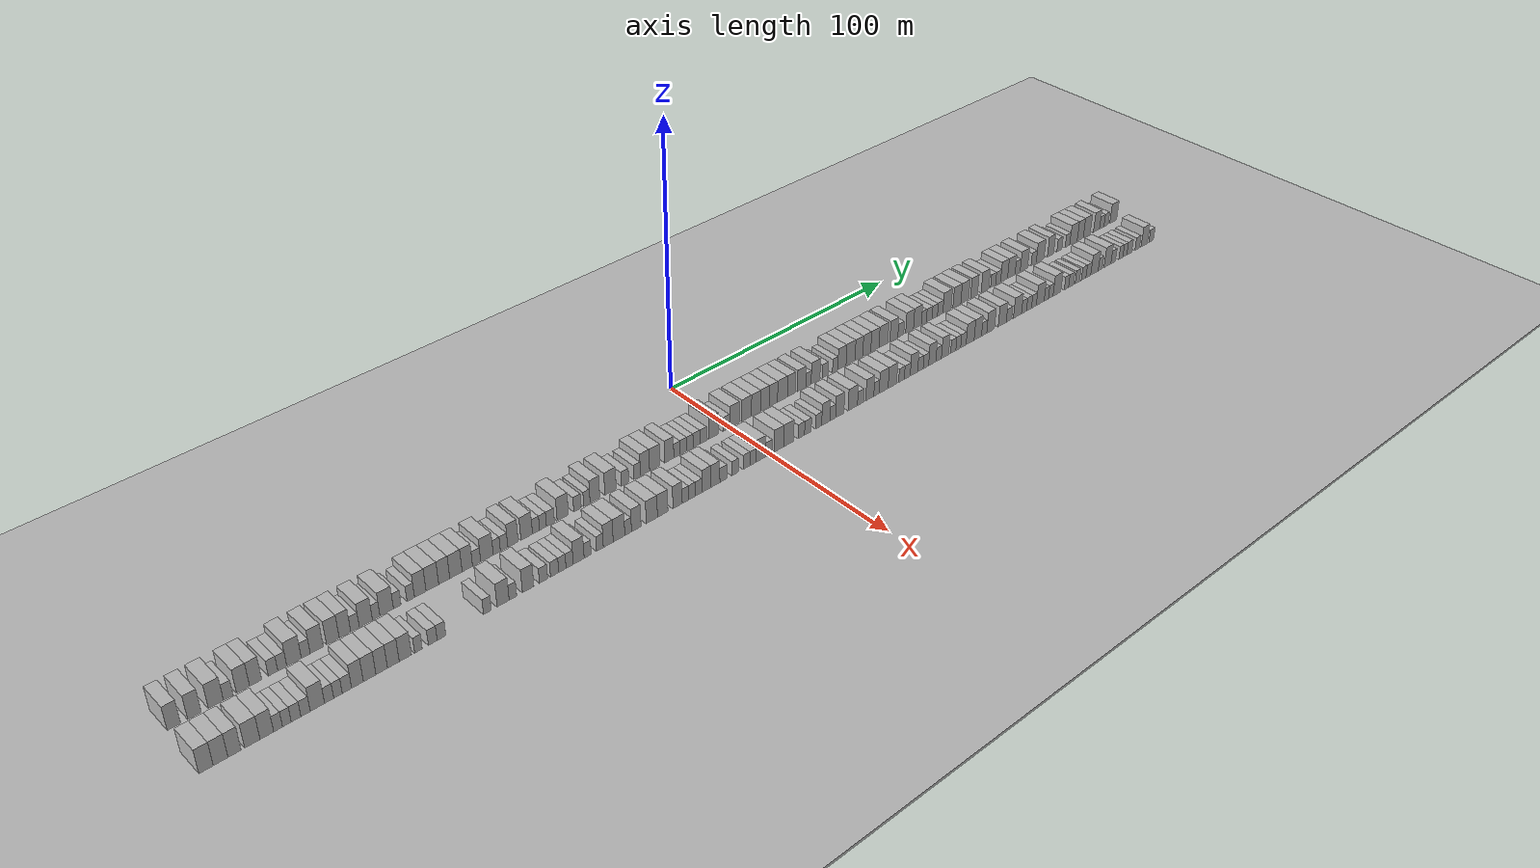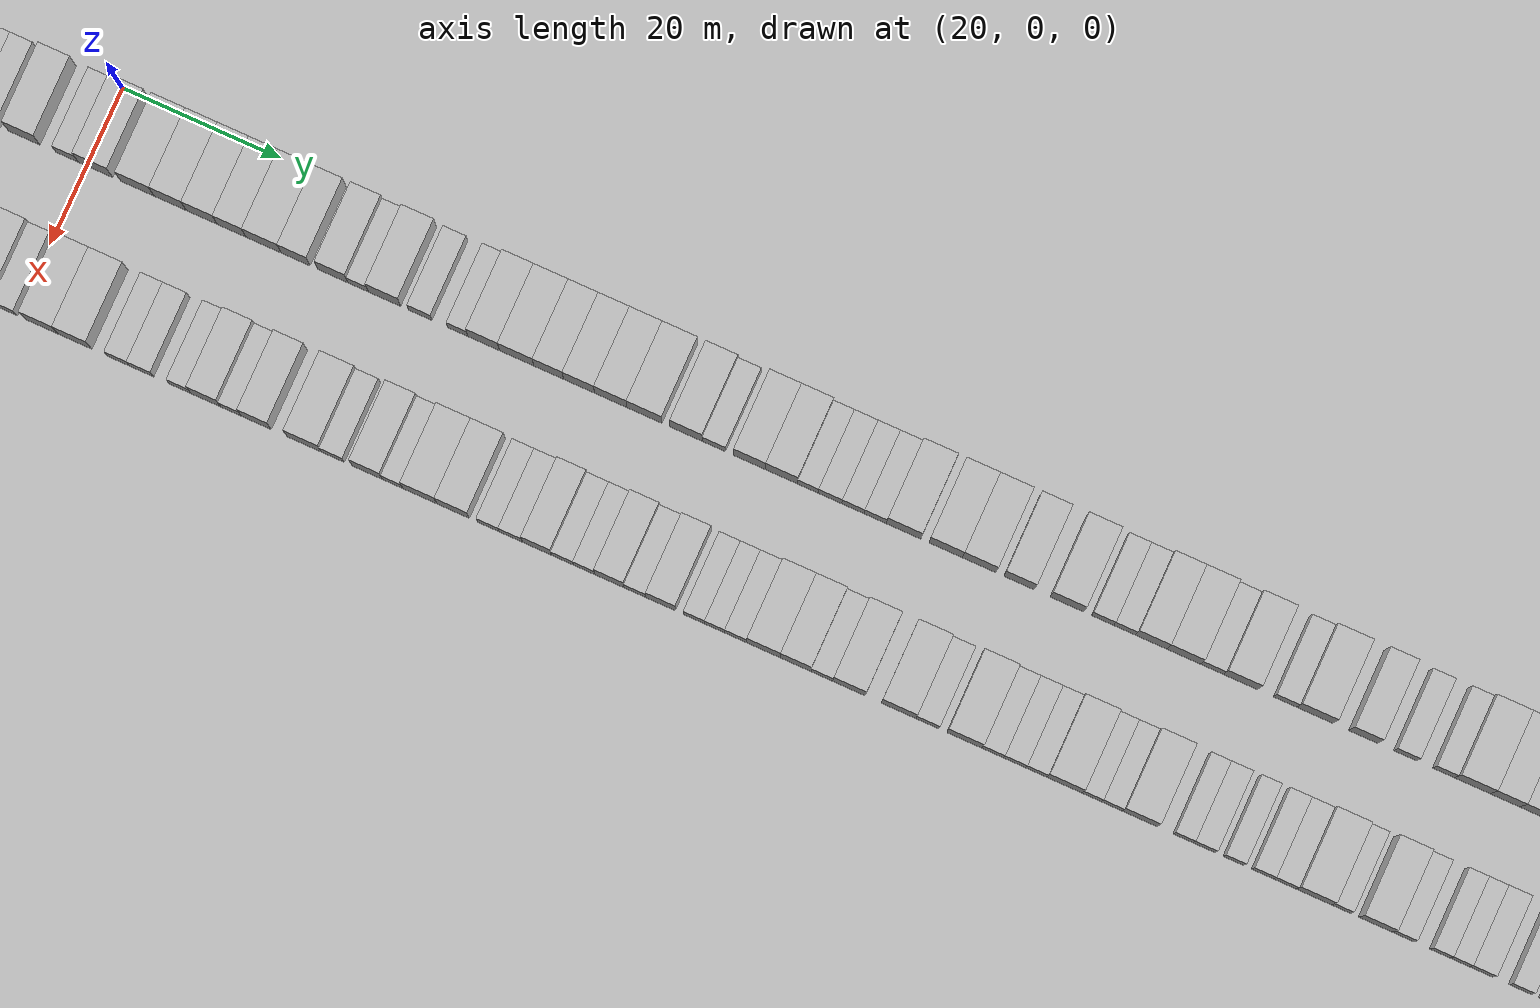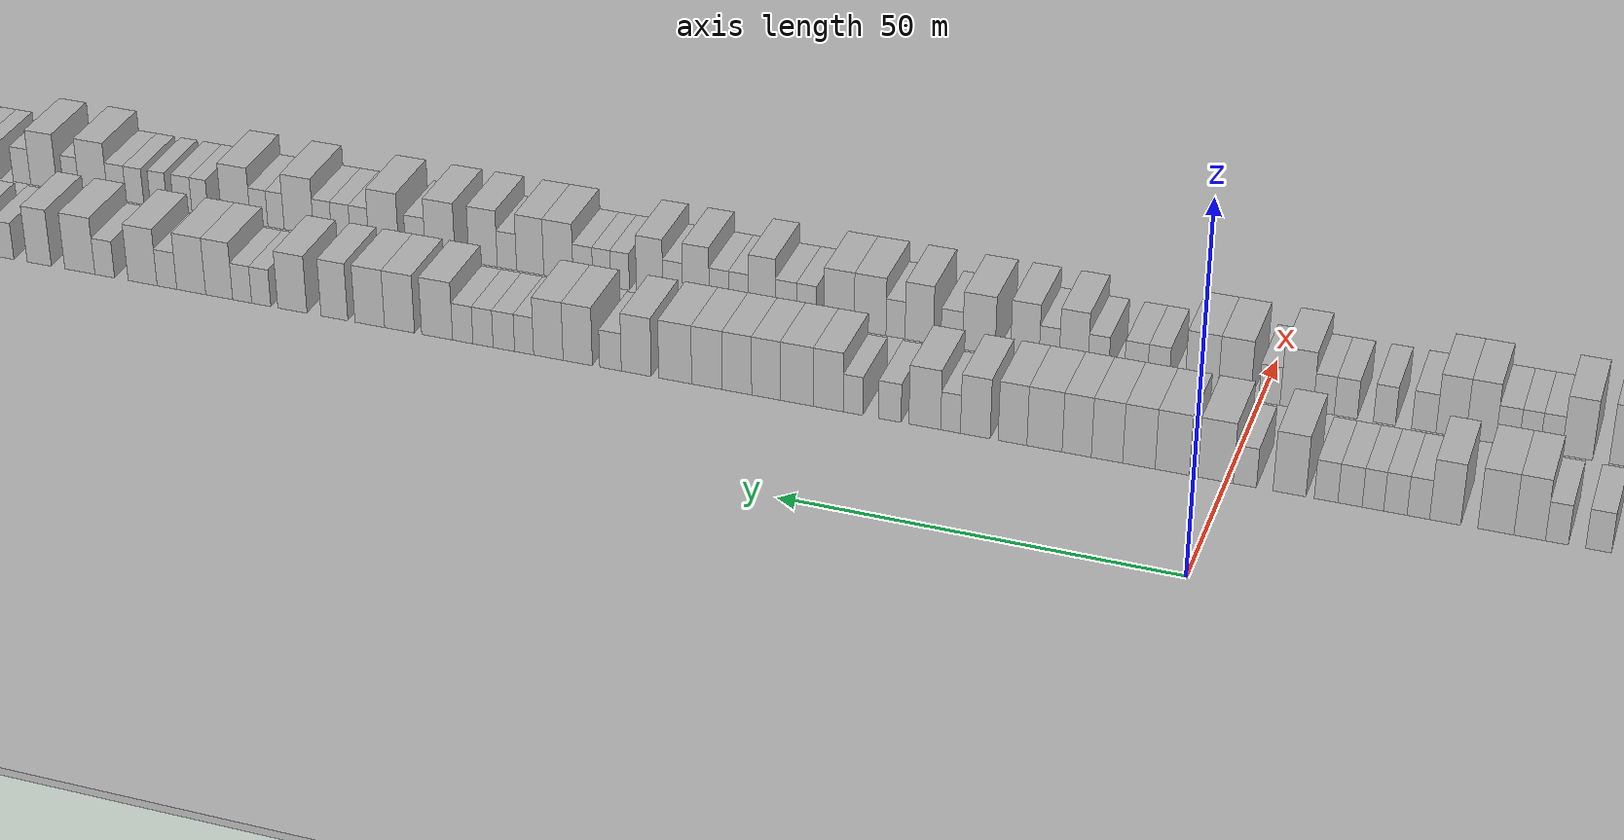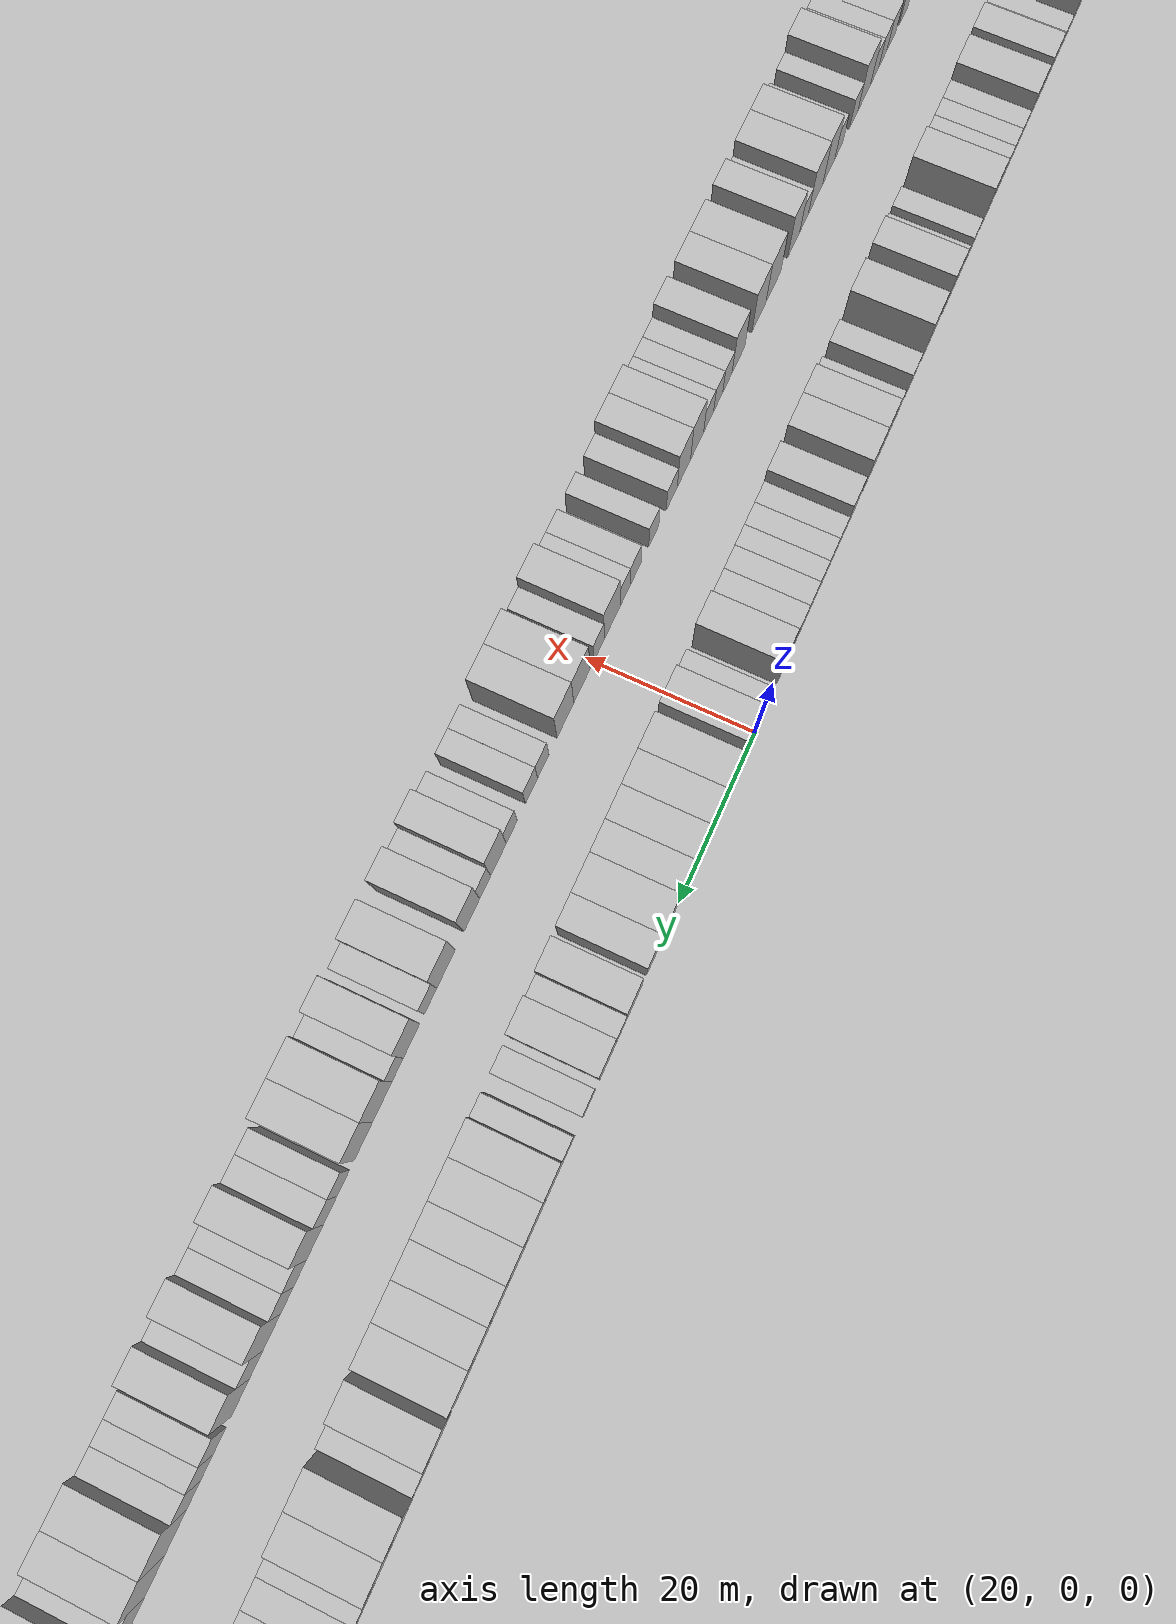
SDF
<?xml version="1.0" encoding="utf-8"?>

<sdf version="1.6">

   <world name="default">

      <gui fullscreen="0">

         <camera name="user_camera">

            <pose>-15 0 4.57585 0 0 0</pose>

            <view_controller>orbit</view_controller>

         </camera>

      </gui>

      <scene>

         <sky>

           <clouds>

             <speed>12</speed>

           </clouds>

         </sky>

         <ambient>0.4 0.4 0.4 1</ambient>

         <background>0.7 0.7 0.7 1</background>

         <shadows>1</shadows>

      </scene>

      <gravity>0 0 -9.8066</gravity>

      <magnetic_field>6e-06 2.3e-05 -4.2e-05</magnetic_field>

      <physics default="0" name="default_physics" type="ode">

         <ode>

            <solver>

               <type>quick</type>

               <iters>10</iters>

               <sor>1.0</sor>

               <use_dynamic_moi_rescaling>0</use_dynamic_moi_rescaling>

            </solver>

            <constraints>

               <cfm>0</cfm>

               <erp>0.2</erp>

               <contact_max_correcting_vel>100</contact_max_correcting_vel>

               <contact_surface_layer>0.001</contact_surface_layer>

            </constraints>

         </ode>

         <max_step_size>0.004</max_step_size>

         <real_time_factor>1</real_time_factor>

         <real_time_update_rate>250</real_time_update_rate>

      </physics>

      <light name="sun" type="directional">

         <cast_shadows>1</cast_shadows>

         <pose>0 0 10 0 0 0</pose>

         <diffuse>0.8 0.8 0.8 1</diffuse>

         <specular>0.2 0.2 0.2 1</specular>

         <attenuation>

            <range>1000</range>

            <constant>0.9</constant>

            <linear>0.01</linear>

            <quadratic>0.001</quadratic>

         </attenuation>

         <direction>-0.5 0.1 -0.9</direction>

      </light>

      <include>

         <name>ground_plane_1</name>

         <uri>model://HANNAS_ground_plane</uri>

         <pose>0 0 0  0 0 0</pose>

      </include>

      <include>

         <name>ground_plane_2</name>

         <uri>model://HANNAS_ground_plane</uri>

         <pose>100 0 0  0 0 0</pose>

      </include>

      <model name="building_1">

         <static>1</static>

         <pose frame="">25.0000 -195.1013 0 0.000000 0.000000 0.000000</pose>

         <link name="link">

            <pose frame="">0 0 4.50 0 0 0</pose>

            <collision name="collision">

               <geometry>

                  <box>

                     <size>10.0000 3.7975 9.0000</size>

                  </box>

               </geometry>

               <max_contacts>10</max_contacts>

               <surface>

                  <contact>

                     <ode/>

                  </contact>

                  <bounce/>

                  <friction>

                     <torsional>

                        <ode/>

                     </torsional>

                     <ode/>

                  </friction>

               </surface>

            </collision>

            <visual name="visual">

               <cast_shadows>0</cast_shadows>

               <geometry>

                  <box>

                     <size>10.0000 3.7975 9.0000</size>

                  </box>

               </geometry>

               <material>

                  <script>

                     <uri>model://HANNAS_wall/materials/scripts</uri>

                     <uri>model://HANNAS_wall/materials/textures</uri>

                     <name>vrc/HANNAS_wall</name>

                  </script>

               </material>

            </visual>

            <self_collide>0</self_collide>

            <enable_wind>0</enable_wind>

            <kinematic>0</kinematic>

         </link>

      </model>

      <model name="building_2">

         <static>1</static>

         <pose frame="">25.0000 -189.2576 0 0.000000 0.000000 0.000000</pose>

         <link name="link">

            <pose frame="">0 0 4.50 0 0 0</pose>

            <collision name="collision">

               <geometry>

                  <box>

                     <size>10.0000 3.8899 9.0000</size>

                  </box>

               </geometry>

               <max_contacts>10</max_contacts>

               <surface>

                  <contact>

                     <ode/>

                  </contact>

                  <bounce/>

                  <friction>

                     <torsional>

                        <ode/>

                     </torsional>

                     <ode/>

                  </friction>

               </surface>

            </collision>

            <visual name="visual">

               <cast_shadows>0</cast_shadows>

               <geometry>

                  <box>

                     <size>10.0000 3.8899 9.0000</size>

                  </box>

               </geometry>

               <material>

                  <script>

                     <uri>model://HANNAS_wall/materials/scripts</uri>

                     <uri>model://HANNAS_wall/materials/textures</uri>

                     <name>vrc/HANNAS_wall</name>

                  </script>

               </material>

            </visual>

            <self_collide>0</self_collide>

            <enable_wind>0</enable_wind>

            <kinematic>0</kinematic>

         </link>

      </model>

      <model name="building_3">

         <static>1</static>

         <pose frame="">25.0000 -183.1088 0 0.000000 0.000000 0.000000</pose>

         <link name="link">

            <pose frame="">0 0 4.50 0 0 0</pose>

            <collision name="collision">

               <geometry>

                  <box>

                     <size>10.0000 4.4077 9.0000</size>

                  </box>

               </geometry>

               <max_contacts>10</max_contacts>

               <surface>

                  <contact>

                     <ode/>

                  </contact>

                  <bounce/>

                  <friction>

                     <torsional>

                        <ode/>

                     </torsional>

                     <ode/>

                  </friction>

               </surface>

            </collision>

            <visual name="visual">

               <cast_shadows>0</cast_shadows>

               <geometry>

                  <box>

                     <size>10.0000 4.4077 9.0000</size>

                  </box>

               </geometry>

               <material>

                  <script>

                     <uri>model://HANNAS_wall/materials/scripts</uri>

                     <uri>model://HANNAS_wall/materials/textures</uri>

                     <name>vrc/HANNAS_wall</name>

                  </script>

               </material>

            </visual>

            <self_collide>0</self_collide>

            <enable_wind>0</enable_wind>

            <kinematic>0</kinematic>

         </link>

      </model>

      <model name="building_4">

         <static>1</static>

         <pose frame="">25.0000 -179.4958 0 0.000000 0.000000 0.000000</pose>

         <link name="link">

            <pose frame="">0 0 3.00 0 0 0</pose>

            <collision name="collision">

               <geometry>

                  <box>

                     <size>10.0000 2.8183 6.0000</size>

                  </box>

               </geometry>

               <max_contacts>10</max_contacts>

               <surface>

                  <contact>

                     <ode/>

                  </contact>

                  <bounce/>

                  <friction>

                     <torsional>

                        <ode/>

                     </torsional>

                     <ode/>

                  </friction>

               </surface>

            </collision>

            <visual name="visual">

               <cast_shadows>0</cast_shadows>

               <geometry>

                  <box>

                     <size>10.0000 2.8183 6.0000</size>

                  </box>

               </geometry>

               <material>

                  <script>

                     <uri>model://HANNAS_wall/materials/scripts</uri>

                     <uri>model://HANNAS_wall/materials/textures</uri>

                     <name>vrc/HANNAS_wall</name>

                  </script>

               </material>

            </visual>

            <self_collide>0</self_collide>

            <enable_wind>0</enable_wind>

            <kinematic>0</kinematic>

         </link>

      </model>

      <model name="building_5">

         <static>1</static>

         <pose frame="">25.0000 -175.1530 0 0.000000 0.000000 0.000000</pose>

         <link name="link">

            <pose frame="">0 0 4.50 0 0 0</pose>

            <collision name="collision">

               <geometry>

                  <box>

                     <size>10.0000 3.8672 9.0000</size>

                  </box>

               </geometry>

               <max_contacts>10</max_contacts>

               <surface>

                  <contact>

                     <ode/>

                  </contact>

                  <bounce/>

                  <friction>

                     <torsional>

                        <ode/>

                     </torsional>

                     <ode/>

                  </friction>

               </surface>

            </collision>

            <visual name="visual">

               <cast_shadows>0</cast_shadows>

               <geometry>

                  <box>

                     <size>10.0000 3.8672 9.0000</size>

                  </box>

               </geometry>

               <material>

                  <script>

                     <uri>model://HANNAS_wall/materials/scripts</uri>

                     <uri>model://HANNAS_wall/materials/textures</uri>

                     <name>vrc/HANNAS_wall</name>

                  </script>

               </material>

            </visual>

            <self_collide>0</self_collide>

            <enable_wind>0</enable_wind>

            <kinematic>0</kinematic>

         </link>

      </model>

      <model name="building_6">

         <static>1</static>

         <pose frame="">25.0000 -171.4095 0 0.000000 0.000000 0.000000</pose>

         <link name="link">

            <pose frame="">0 0 4.50 0 0 0</pose>

            <collision name="collision">

               <geometry>

                  <box>

                     <size>10.0000 3.6197 9.0000</size>

                  </box>

               </geometry>

               <max_contacts>10</max_contacts>

               <surface>

                  <contact>

                     <ode/>

                  </contact>

                  <bounce/>

                  <friction>

                     <torsional>

                        <ode/>

                     </torsional>

                     <ode/>

                  </friction>

               </surface>

            </collision>

            <visual name="visual">

               <cast_shadows>0</cast_shadows>

               <geometry>

                  <box>

                     <size>10.0000 3.6197 9.0000</size>

                  </box>

               </geometry>

               <material>

                  <script>

                     <uri>model://HANNAS_wall/materials/scripts</uri>

                     <uri>model://HANNAS_wall/materials/textures</uri>

                     <name>vrc/HANNAS_wall</name>

                  </script>

               </material>

            </visual>

            <self_collide>0</self_collide>

            <enable_wind>0</enable_wind>

            <kinematic>0</kinematic>

         </link>

      </model>

      <model name="building_7">

         <static>1</static>

         <pose frame="">25.0000 -166.1617 0 0.000000 0.000000 0.000000</pose>

         <link name="link">

            <pose frame="">0 0 3.00 0 0 0</pose>

            <collision name="collision">

               <geometry>

                  <box>

                     <size>10.0000 2.8759 6.0000</size>

                  </box>

               </geometry>

               <max_contacts>10</max_contacts>

               <surface>

                  <contact>

                     <ode/>

                  </contact>

                  <bounce/>

                  <friction>

                     <torsional>

                        <ode/>

                     </torsional>

                     <ode/>

                  </friction>

               </surface>

            </collision>

            <visual name="visual">

               <cast_shadows>0</cast_shadows>

               <geometry>

                  <box>

                     <size>10.0000 2.8759 6.0000</size>

                  </box>

               </geometry>

               <material>

                  <script>

                     <uri>model://HANNAS_wall/materials/scripts</uri>

                     <uri>model://HANNAS_wall/materials/textures</uri>

                     <name>vrc/HANNAS_wall</name>

                  </script>

               </material>

            </visual>

            <self_collide>0</self_collide>

            <enable_wind>0</enable_wind>

            <kinematic>0</kinematic>

         </link>

      </model>

      <model name="building_8">

         <static>1</static>

         <pose frame="">25.0000 -163.3585 0 0.000000 0.000000 0.000000</pose>

         <link name="link">

            <pose frame="">0 0 3.00 0 0 0</pose>

            <collision name="collision">

               <geometry>

                  <box>

                     <size>10.0000 2.7304 6.0000</size>

                  </box>

               </geometry>

               <max_contacts>10</max_contacts>

               <surface>

                  <contact>

                     <ode/>

                  </contact>

                  <bounce/>

                  <friction>

                     <torsional>

                        <ode/>

                     </torsional>

                     <ode/>

                  </friction>

               </surface>

            </collision>

            <visual name="visual">

               <cast_shadows>0</cast_shadows>

               <geometry>

                  <box>

                     <size>10.0000 2.7304 6.0000</size>

                  </box>

               </geometry>

               <material>

                  <script>

                     <uri>model://HANNAS_wall/materials/scripts</uri>

                     <uri>model://HANNAS_wall/materials/textures</uri>

                     <name>vrc/HANNAS_wall</name>

                  </script>

               </material>

            </visual>

            <self_collide>0</self_collide>

            <enable_wind>0</enable_wind>

            <kinematic>0</kinematic>

         </link>

      </model>

      <model name="building_9">

         <static>1</static>

         <pose frame="">25.0000 -159.7490 0 0.000000 0.000000 0.000000</pose>

         <link name="link">

            <pose frame="">0 0 4.50 0 0 0</pose>

            <collision name="collision">

               <geometry>

                  <box>

                     <size>10.0000 4.4887 9.0000</size>

                  </box>

               </geometry>

               <max_contacts>10</max_contacts>

               <surface>

                  <contact>

                     <ode/>

                  </contact>

                  <bounce/>

                  <friction>

                     <torsional>

                        <ode/>

                     </torsional>

                     <ode/>

                  </friction>

               </surface>

            </collision>

            <visual name="visual">

               <cast_shadows>0</cast_shadows>

               <geometry>

                  <box>

                     <size>10.0000 4.4887 9.0000</size>

                  </box>

               </geometry>

               <material>

                  <script>

                     <uri>model://HANNAS_wall/materials/scripts</uri>

                     <uri>model://HANNAS_wall/materials/textures</uri>

                     <name>vrc/HANNAS_wall</name>

                  </script>

               </material>

            </visual>

            <self_collide>0</self_collide>

            <enable_wind>0</enable_wind>

            <kinematic>0</kinematic>

         </link>

      </model>

      <model name="building_10">

         <static>1</static>

         <pose frame="">25.0000 -156.1416 0 0.000000 0.000000 0.000000</pose>

         <link name="link">

            <pose frame="">0 0 3.00 0 0 0</pose>

            <collision name="collision">

               <geometry>

                  <box>

                     <size>10.0000 2.7260 6.0000</size>

                  </box>

               </geometry>

               <max_contacts>10</max_contacts>

               <surface>

                  <contact>

                     <ode/>

                  </contact>

                  <bounce/>

                  <friction>

                     <torsional>

                        <ode/>

                     </torsional>

                     <ode/>

                  </friction>

               </surface>

            </collision>

            <visual name="visual">

               <cast_shadows>0</cast_shadows>

               <geometry>

                  <box>

                     <size>10.0000 2.7260 6.0000</size>

                  </box>

               </geometry>

               <material>

                  <script>

                     <uri>model://HANNAS_wall/materials/scripts</uri>

                     <uri>model://HANNAS_wall/materials/textures</uri>

                     <name>vrc/HANNAS_wall</name>

                  </script>

               </material>

            </visual>

            <self_collide>0</self_collide>

            <enable_wind>0</enable_wind>

            <kinematic>0</kinematic>

         </link>

      </model>

      <model name="building_11">

         <static>1</static>

         <pose frame="">25.0000 -152.7426 0 0.000000 0.000000 0.000000</pose>

         <link name="link">

            <pose frame="">0 0 4.50 0 0 0</pose>

            <collision name="collision">

               <geometry>

                  <box>

                     <size>10.0000 4.0721 9.0000</size>

                  </box>

               </geometry>

               <max_contacts>10</max_contacts>

               <surface>

                  <contact>

                     <ode/>

                  </contact>

                  <bounce/>

                  <friction>

                     <torsional>

                        <ode/>

                     </torsional>

                     <ode/>

                  </friction>

               </surface>

            </collision>

            <visual name="visual">

               <cast_shadows>0</cast_shadows>

               <geometry>

                  <box>

                     <size>10.0000 4.0721 9.0000</size>

                  </box>

               </geometry>

               <material>

                  <script>

                     <uri>model://HANNAS_wall/materials/scripts</uri>

                     <uri>model://HANNAS_wall/materials/textures</uri>

                     <name>vrc/HANNAS_wall</name>

                  </script>

               </material>

            </visual>

            <self_collide>0</self_collide>

            <enable_wind>0</enable_wind>

            <kinematic>0</kinematic>

         </link>

      </model>

      <model name="building_12">

         <static>1</static>

         <pose frame="">25.0000 -147.6966 0 0.000000 0.000000 0.000000</pose>

         <link name="link">

            <pose frame="">0 0 4.50 0 0 0</pose>

            <collision name="collision">

               <geometry>

                  <box>

                     <size>10.0000 4.0199 9.0000</size>

                  </box>

               </geometry>

               <max_contacts>10</max_contacts>

               <surface>

                  <contact>

                     <ode/>

                  </contact>

                  <bounce/>

                  <friction>

                     <torsional>

                        <ode/>

                     </torsional>

                     <ode/>

                  </friction>

               </surface>

            </collision>

            <visual name="visual">

               <cast_shadows>0</cast_shadows>

               <geometry>

                  <box>

                     <size>10.0000 4.0199 9.0000</size>

                  </box>

               </geometry>

               <material>

                  <script>

                     <uri>model://HANNAS_wall/materials/scripts</uri>

                     <uri>model://HANNAS_wall/materials/textures</uri>

                     <name>vrc/HANNAS_wall</name>

                  </script>

               </material>

            </visual>

            <self_collide>0</self_collide>

            <enable_wind>0</enable_wind>

            <kinematic>0</kinematic>

         </link>

      </model>

      <model name="building_13">

         <static>1</static>

         <pose frame="">25.0000 -143.8593 0 0.000000 0.000000 0.000000</pose>

         <link name="link">

            <pose frame="">0 0 4.50 0 0 0</pose>

            <collision name="collision">

               <geometry>

                  <box>

                     <size>10.0000 3.6547 9.0000</size>

                  </box>

               </geometry>

               <max_contacts>10</max_contacts>

               <surface>

                  <contact>

                     <ode/>

                  </contact>

                  <bounce/>

                  <friction>

                     <torsional>

                        <ode/>

                     </torsional>

                     <ode/>

                  </friction>

               </surface>

            </collision>

            <visual name="visual">

               <cast_shadows>0</cast_shadows>

               <geometry>

                  <box>

                     <size>10.0000 3.6547 9.0000</size>

                  </box>

               </geometry>

               <material>

                  <script>

                     <uri>model://HANNAS_wall/materials/scripts</uri>

                     <uri>model://HANNAS_wall/materials/textures</uri>

                     <name>vrc/HANNAS_wall</name>

                  </script>

               </material>

            </visual>

            <self_collide>0</self_collide>

            <enable_wind>0</enable_wind>

            <kinematic>0</kinematic>

         </link>

      </model>

      <model name="building_14">

         <static>1</static>

         <pose frame="">25.0000 -140.6452 0 0.000000 0.000000 0.000000</pose>

         <link name="link">

            <pose frame="">0 0 3.00 0 0 0</pose>

            <collision name="collision">

               <geometry>

                  <box>

                     <size>10.0000 2.7734 6.0000</size>

                  </box>

               </geometry>

               <max_contacts>10</max_contacts>

               <surface>

                  <contact>

                     <ode/>

                  </contact>

                  <bounce/>

                  <friction>

                     <torsional>

                        <ode/>

                     </torsional>

                     <ode/>

                  </friction>

               </surface>

            </collision>

            <visual name="visual">

               <cast_shadows>0</cast_shadows>

               <geometry>

                  <box>

                     <size>10.0000 2.7734 6.0000</size>

                  </box>

               </geometry>

               <material>

                  <script>

                     <uri>model://HANNAS_wall/materials/scripts</uri>

                     <uri>model://HANNAS_wall/materials/textures</uri>

                     <name>vrc/HANNAS_wall</name>

                  </script>

               </material>

            </visual>

            <self_collide>0</self_collide>

            <enable_wind>0</enable_wind>

            <kinematic>0</kinematic>

         </link>

      </model>

      <model name="building_15">

         <static>1</static>

         <pose frame="">25.0000 -137.1260 0 0.000000 0.000000 0.000000</pose>

         <link name="link">

            <pose frame="">0 0 4.50 0 0 0</pose>

            <collision name="collision">

               <geometry>

                  <box>

                     <size>10.0000 4.2651 9.0000</size>

                  </box>

               </geometry>

               <max_contacts>10</max_contacts>

               <surface>

                  <contact>

                     <ode/>

                  </contact>

                  <bounce/>

                  <friction>

                     <torsional>

                        <ode/>

                     </torsional>

                     <ode/>

                  </friction>

               </surface>

            </collision>

            <visual name="visual">

               <cast_shadows>0</cast_shadows>

               <geometry>

                  <box>

                     <size>10.0000 4.2651 9.0000</size>

                  </box>

               </geometry>

               <material>

                  <script>

                     <uri>model://HANNAS_wall/materials/scripts</uri>

                     <uri>model://HANNAS_wall/materials/textures</uri>

                     <name>vrc/HANNAS_wall</name>

                  </script>

               </material>

            </visual>

            <self_collide>0</self_collide>

            <enable_wind>0</enable_wind>

            <kinematic>0</kinematic>

         </link>

      </model>

      <model name="building_16">

         <static>1</static>

         <pose frame="">25.0000 -133.7711 0 0.000000 0.000000 0.000000</pose>

         <link name="link">

            <pose frame="">0 0 3.00 0 0 0</pose>

            <collision name="collision">

               <geometry>

                  <box>

                     <size>10.0000 2.4447 6.0000</size>

                  </box>

               </geometry>

               <max_contacts>10</max_contacts>

               <surface>

                  <contact>

                     <ode/>

                  </contact>

                  <bounce/>

                  <friction>

                     <torsional>

                        <ode/>

                     </torsional>

                     <ode/>

                  </friction>

               </surface>

            </collision>

            <visual name="visual">

               <cast_shadows>0</cast_shadows>

               <geometry>

                  <box>

                     <size>10.0000 2.4447 6.0000</size>

                  </box>

               </geometry>

               <material>

                  <script>

                     <uri>model://HANNAS_wall/materials/scripts</uri>

                     <uri>model://HANNAS_wall/materials/textures</uri>

                     <name>vrc/HANNAS_wall</name>

                  </script>

               </material>

            </visual>

            <self_collide>0</self_collide>

            <enable_wind>0</enable_wind>

            <kinematic>0</kinematic>

         </link>

      </model>

      <model name="building_17">

         <static>1</static>

         <pose frame="">25.0000 -130.3299 0 0.000000 0.000000 0.000000</pose>

         <link name="link">

            <pose frame="">0 0 4.50 0 0 0</pose>

            <collision name="collision">

               <geometry>

                  <box>

                     <size>10.0000 4.4376 9.0000</size>

                  </box>

               </geometry>

               <max_contacts>10</max_contacts>

               <surface>

                  <contact>

                     <ode/>

                  </contact>

                  <bounce/>

                  <friction>

                     <torsional>

                        <ode/>

                     </torsional>

                     <ode/>

                  </friction>

               </surface>

            </collision>

            <visual name="visual">

               <cast_shadows>0</cast_shadows>

               <geometry>

                  <box>

                     <size>10.0000 4.4376 9.0000</size>

                  </box>

               </geometry>

               <material>

                  <script>

                     <uri>model://HANNAS_wall/materials/scripts</uri>

                     <uri>model://HANNAS_wall/materials/textures</uri>

                     <name>vrc/HANNAS_wall</name>

                  </script>

               </material>

            </visual>

            <self_collide>0</self_collide>

            <enable_wind>0</enable_wind>

            <kinematic>0</kinematic>

         </link>

      </model>

      <model name="building_18">

         <static>1</static>

         <pose frame="">25.0000 -126.8712 0 0.000000 0.000000 0.000000</pose>

         <link name="link">

            <pose frame="">0 0 3.00 0 0 0</pose>

            <collision name="collision">

               <geometry>

                  <box>

                     <size>10.0000 2.4798 6.0000</size>

                  </box>

               </geometry>

               <max_contacts>10</max_contacts>

               <surface>

                  <contact>

                     <ode/>

                  </contact>

                  <bounce/>

                  <friction>

                     <torsional>

                        <ode/>

                     </torsional>

                     <ode/>

                  </friction>

               </surface>

            </collision>

            <visual name="visual">

               <cast_shadows>0</cast_shadows>

               <geometry>

                  <box>

                     <size>10.0000 2.4798 6.0000</size>

                  </box>

               </geometry>

               <material>

                  <script>

                     <uri>model://HANNAS_wall/materials/scripts</uri>

                     <uri>model://HANNAS_wall/materials/textures</uri>

                     <name>vrc/HANNAS_wall</name>

                  </script>

               </material>

            </visual>

            <self_collide>0</self_collide>

            <enable_wind>0</enable_wind>

            <kinematic>0</kinematic>

         </link>

      </model>

      <model name="building_19">

         <static>1</static>

         <pose frame="">25.0000 -122.3737 0 0.000000 0.000000 0.000000</pose>

         <link name="link">

            <pose frame="">0 0 3.00 0 0 0</pose>

            <collision name="collision">

               <geometry>

                  <box>

                     <size>10.0000 2.5151 6.0000</size>

                  </box>

               </geometry>

               <max_contacts>10</max_contacts>

               <surface>

                  <contact>

                     <ode/>

                  </contact>

                  <bounce/>

                  <friction>

                     <torsional>

                        <ode/>

                     </torsional>

                     <ode/>

                  </friction>

               </surface>

            </collision>

            <visual name="visual">

               <cast_shadows>0</cast_shadows>

               <geometry>

                  <box>

                     <size>10.0000 2.5151 6.0000</size>

                  </box>

               </geometry>

               <material>

                  <script>

                     <uri>model://HANNAS_wall/materials/scripts</uri>

                     <uri>model://HANNAS_wall/materials/textures</uri>

                     <name>vrc/HANNAS_wall</name>

                  </script>

               </material>

            </visual>

            <self_collide>0</self_collide>

            <enable_wind>0</enable_wind>

            <kinematic>0</kinematic>

         </link>

      </model>

      <model name="building_20">

         <static>1</static>

         <pose frame="">25.0000 -119.1748 0 0.000000 0.000000 0.000000</pose>

         <link name="link">

            <pose frame="">0 0 4.50 0 0 0</pose>

            <collision name="collision">

               <geometry>

                  <box>

                     <size>10.0000 3.8827 9.0000</size>

                  </box>

               </geometry>

               <max_contacts>10</max_contacts>

               <surface>

                  <contact>

                     <ode/>

                  </contact>

                  <bounce/>

                  <friction>

                     <torsional>

                        <ode/>

                     </torsional>

                     <ode/>

                  </friction>

               </surface>

            </collision>

            <visual name="visual">

               <cast_shadows>0</cast_shadows>

               <geometry>

                  <box>

                     <size>10.0000 3.8827 9.0000</size>

                  </box>

               </geometry>

               <material>

                  <script>

                     <uri>model://HANNAS_wall/materials/scripts</uri>

                     <uri>model://HANNAS_wall/materials/textures</uri>

                     <name>vrc/HANNAS_wall</name>

                  </script>

               </material>

            </visual>

            <self_collide>0</self_collide>

            <enable_wind>0</enable_wind>

            <kinematic>0</kinematic>

         </link>

      </model>

      <model name="building_21">

         <static>1</static>

         <pose frame="">25.0000 -115.0764 0 0.000000 0.000000 0.000000</pose>

         <link name="link">

            <pose frame="">0 0 4.50 0 0 0</pose>

            <collision name="collision">

               <geometry>

                  <box>

                     <size>10.0000 4.3143 9.0000</size>

                  </box>

               </geometry>

               <max_contacts>10</max_contacts>

               <surface>

                  <contact>

                     <ode/>

                  </contact>

                  <bounce/>

                  <friction>

                     <torsional>

                        <ode/>

                     </torsional>

                     <ode/>

                  </friction>

               </surface>

            </collision>

            <visual name="visual">

               <cast_shadows>0</cast_shadows>

               <geometry>

                  <box>

                     <size>10.0000 4.3143 9.0000</size>

                  </box>

               </geometry>

               <material>

                  <script>

                     <uri>model://HANNAS_wall/materials/scripts</uri>

                     <uri>model://HANNAS_wall/materials/textures</uri>

                     <name>vrc/HANNAS_wall</name>

                  </script>

               </material>

            </visual>

            <self_collide>0</self_collide>

            <enable_wind>0</enable_wind>

            <kinematic>0</kinematic>

         </link>

      </model>

      <model name="building_22">

         <static>1</static>

         <pose frame="">25.0000 -111.0092 0 0.000000 0.000000 0.000000</pose>

         <link name="link">

            <pose frame="">0 0 4.50 0 0 0</pose>

            <collision name="collision">

               <geometry>

                  <box>

                     <size>10.0000 3.8200 9.0000</size>

                  </box>

               </geometry>

               <max_contacts>10</max_contacts>

               <surface>

                  <contact>

                     <ode/>

                  </contact>

                  <bounce/>

                  <friction>

                     <torsional>

                        <ode/>

                     </torsional>

                     <ode/>

                  </friction>

               </surface>

            </collision>

            <visual name="visual">

               <cast_shadows>0</cast_shadows>

               <geometry>

                  <box>

                     <size>10.0000 3.8200 9.0000</size>

                  </box>

               </geometry>

               <material>

                  <script>

                     <uri>model://HANNAS_wall/materials/scripts</uri>

                     <uri>model://HANNAS_wall/materials/textures</uri>

                     <name>vrc/HANNAS_wall</name>

                  </script>

               </material>

            </visual>

            <self_collide>0</self_collide>

            <enable_wind>0</enable_wind>

            <kinematic>0</kinematic>

         </link>

      </model>

      <model name="building_23">

         <static>1</static>

         <pose frame="">25.0000 -106.9611 0 0.000000 0.000000 0.000000</pose>

         <link name="link">

            <pose frame="">0 0 4.50 0 0 0</pose>

            <collision name="collision">

               <geometry>

                  <box>

                     <size>10.0000 4.2764 9.0000</size>

                  </box>

               </geometry>

               <max_contacts>10</max_contacts>

               <surface>

                  <contact>

                     <ode/>

                  </contact>

                  <bounce/>

                  <friction>

                     <torsional>

                        <ode/>

                     </torsional>

                     <ode/>

                  </friction>

               </surface>

            </collision>

            <visual name="visual">

               <cast_shadows>0</cast_shadows>

               <geometry>

                  <box>

                     <size>10.0000 4.2764 9.0000</size>

                  </box>

               </geometry>

               <material>

                  <script>

                     <uri>model://HANNAS_wall/materials/scripts</uri>

                     <uri>model://HANNAS_wall/materials/textures</uri>

                     <name>vrc/HANNAS_wall</name>

                  </script>

               </material>

            </visual>

            <self_collide>0</self_collide>

            <enable_wind>0</enable_wind>

            <kinematic>0</kinematic>

         </link>

      </model>

      <model name="building_24">

         <static>1</static>

         <pose frame="">25.0000 -103.0037 0 0.000000 0.000000 0.000000</pose>

         <link name="link">

            <pose frame="">0 0 4.50 0 0 0</pose>

            <collision name="collision">

               <geometry>

                  <box>

                     <size>10.0000 3.6384 9.0000</size>

                  </box>

               </geometry>

               <max_contacts>10</max_contacts>

               <surface>

                  <contact>

                     <ode/>

                  </contact>

                  <bounce/>

                  <friction>

                     <torsional>

                        <ode/>

                     </torsional>

                     <ode/>

                  </friction>

               </surface>

            </collision>

            <visual name="visual">

               <cast_shadows>0</cast_shadows>

               <geometry>

                  <box>

                     <size>10.0000 3.6384 9.0000</size>

                  </box>

               </geometry>

               <material>

                  <script>

                     <uri>model://HANNAS_wall/materials/scripts</uri>

                     <uri>model://HANNAS_wall/materials/textures</uri>

                     <name>vrc/HANNAS_wall</name>

                  </script>

               </material>

            </visual>

            <self_collide>0</self_collide>

            <enable_wind>0</enable_wind>

            <kinematic>0</kinematic>

         </link>

      </model>

      <model name="building_25">

         <static>1</static>

         <pose frame="">25.0000 -99.7405 0 0.000000 0.000000 0.000000</pose>

         <link name="link">

            <pose frame="">0 0 3.00 0 0 0</pose>

            <collision name="collision">

               <geometry>

                  <box>

                     <size>10.0000 2.8878 6.0000</size>

                  </box>

               </geometry>

               <max_contacts>10</max_contacts>

               <surface>

                  <contact>

                     <ode/>

                  </contact>

                  <bounce/>

                  <friction>

                     <torsional>

                        <ode/>

                     </torsional>

                     <ode/>

                  </friction>

               </surface>

            </collision>

            <visual name="visual">

               <cast_shadows>0</cast_shadows>

               <geometry>

                  <box>

                     <size>10.0000 2.8878 6.0000</size>

                  </box>

               </geometry>

               <material>

                  <script>

                     <uri>model://HANNAS_wall/materials/scripts</uri>

                     <uri>model://HANNAS_wall/materials/textures</uri>

                     <name>vrc/HANNAS_wall</name>

                  </script>

               </material>

            </visual>

            <self_collide>0</self_collide>

            <enable_wind>0</enable_wind>

            <kinematic>0</kinematic>

         </link>

      </model>

      <model name="building_26">

         <static>1</static>

         <pose frame="">25.0000 -96.0663 0 0.000000 0.000000 0.000000</pose>

         <link name="link">

            <pose frame="">0 0 4.50 0 0 0</pose>

            <collision name="collision">

               <geometry>

                  <box>

                     <size>10.0000 4.4608 9.0000</size>

                  </box>

               </geometry>

               <max_contacts>10</max_contacts>

               <surface>

                  <contact>

                     <ode/>

                  </contact>

                  <bounce/>

                  <friction>

                     <torsional>

                        <ode/>

                     </torsional>

                     <ode/>

                  </friction>

               </surface>

            </collision>

            <visual name="visual">

               <cast_shadows>0</cast_shadows>

               <geometry>

                  <box>

                     <size>10.0000 4.4608 9.0000</size>

                  </box>

               </geometry>

               <material>

                  <script>

                     <uri>model://HANNAS_wall/materials/scripts</uri>

                     <uri>model://HANNAS_wall/materials/textures</uri>

                     <name>vrc/HANNAS_wall</name>

                  </script>

               </material>

            </visual>

            <self_collide>0</self_collide>

            <enable_wind>0</enable_wind>

            <kinematic>0</kinematic>

         </link>

      </model>

      <model name="building_27">

         <static>1</static>

         <pose frame="">25.0000 -92.5703 0 0.000000 0.000000 0.000000</pose>

         <link name="link">

            <pose frame="">0 0 3.00 0 0 0</pose>

            <collision name="collision">

               <geometry>

                  <box>

                     <size>10.0000 2.5311 6.0000</size>

                  </box>

               </geometry>

               <max_contacts>10</max_contacts>

               <surface>

                  <contact>

                     <ode/>

                  </contact>

                  <bounce/>

                  <friction>

                     <torsional>

                        <ode/>

                     </torsional>

                     <ode/>

                  </friction>

               </surface>

            </collision>

            <visual name="visual">

               <cast_shadows>0</cast_shadows>

               <geometry>

                  <box>

                     <size>10.0000 2.5311 6.0000</size>

                  </box>

               </geometry>

               <material>

                  <script>

                     <uri>model://HANNAS_wall/materials/scripts</uri>

                     <uri>model://HANNAS_wall/materials/textures</uri>

                     <name>vrc/HANNAS_wall</name>

                  </script>

               </material>

            </visual>

            <self_collide>0</self_collide>

            <enable_wind>0</enable_wind>

            <kinematic>0</kinematic>

         </link>

      </model>

      <model name="building_28">

         <static>1</static>

         <pose frame="">25.0000 -89.9703 0 0.000000 0.000000 0.000000</pose>

         <link name="link">

            <pose frame="">0 0 3.00 0 0 0</pose>

            <collision name="collision">

               <geometry>

                  <box>

                     <size>10.0000 2.6690 6.0000</size>

                  </box>

               </geometry>

               <max_contacts>10</max_contacts>

               <surface>

                  <contact>

                     <ode/>

                  </contact>

                  <bounce/>

                  <friction>

                     <torsional>

                        <ode/>

                     </torsional>

                     <ode/>

                  </friction>

               </surface>

            </collision>

            <visual name="visual">

               <cast_shadows>0</cast_shadows>

               <geometry>

                  <box>

                     <size>10.0000 2.6690 6.0000</size>

                  </box>

               </geometry>

               <material>

                  <script>

                     <uri>model://HANNAS_wall/materials/scripts</uri>

                     <uri>model://HANNAS_wall/materials/textures</uri>

                     <name>vrc/HANNAS_wall</name>

                  </script>

               </material>

            </visual>

            <self_collide>0</self_collide>

            <enable_wind>0</enable_wind>

            <kinematic>0</kinematic>

         </link>

      </model>

      <model name="building_29">

         <static>1</static>

         <pose frame="">25.0000 -86.7608 0 0.000000 0.000000 0.000000</pose>

         <link name="link">

            <pose frame="">0 0 4.50 0 0 0</pose>

            <collision name="collision">

               <geometry>

                  <box>

                     <size>10.0000 3.7500 9.0000</size>

                  </box>

               </geometry>

               <max_contacts>10</max_contacts>

               <surface>

                  <contact>

                     <ode/>

                  </contact>

                  <bounce/>

                  <friction>

                     <torsional>

                        <ode/>

                     </torsional>

                     <ode/>

                  </friction>

               </surface>

            </collision>

            <visual name="visual">

               <cast_shadows>0</cast_shadows>

               <geometry>

                  <box>

                     <size>10.0000 3.7500 9.0000</size>

                  </box>

               </geometry>

               <material>

                  <script>

                     <uri>model://HANNAS_wall/materials/scripts</uri>

                     <uri>model://HANNAS_wall/materials/textures</uri>

                     <name>vrc/HANNAS_wall</name>

                  </script>

               </material>

            </visual>

            <self_collide>0</self_collide>

            <enable_wind>0</enable_wind>

            <kinematic>0</kinematic>

         </link>

      </model>

      <model name="building_30">

         <static>1</static>

         <pose frame="">25.0000 -81.7724 0 0.000000 0.000000 0.000000</pose>

         <link name="link">

            <pose frame="">0 0 4.50 0 0 0</pose>

            <collision name="collision">

               <geometry>

                  <box>

                     <size>10.0000 4.2270 9.0000</size>

                  </box>

               </geometry>

               <max_contacts>10</max_contacts>

               <surface>

                  <contact>

                     <ode/>

                  </contact>

                  <bounce/>

                  <friction>

                     <torsional>

                        <ode/>

                     </torsional>

                     <ode/>

                  </friction>

               </surface>

            </collision>

            <visual name="visual">

               <cast_shadows>0</cast_shadows>

               <geometry>

                  <box>

                     <size>10.0000 4.2270 9.0000</size>

                  </box>

               </geometry>

               <material>

                  <script>

                     <uri>model://HANNAS_wall/materials/scripts</uri>

                     <uri>model://HANNAS_wall/materials/textures</uri>

                     <name>vrc/HANNAS_wall</name>

                  </script>

               </material>

            </visual>

            <self_collide>0</self_collide>

            <enable_wind>0</enable_wind>

            <kinematic>0</kinematic>

         </link>

      </model>

      <model name="building_31">

         <static>1</static>

         <pose frame="">25.0000 -78.3434 0 0.000000 0.000000 0.000000</pose>

         <link name="link">

            <pose frame="">0 0 3.00 0 0 0</pose>

            <collision name="collision">

               <geometry>

                  <box>

                     <size>10.0000 2.6310 6.0000</size>

                  </box>

               </geometry>

               <max_contacts>10</max_contacts>

               <surface>

                  <contact>

                     <ode/>

                  </contact>

                  <bounce/>

                  <friction>

                     <torsional>

                        <ode/>

                     </torsional>

                     <ode/>

                  </friction>

               </surface>

            </collision>

            <visual name="visual">

               <cast_shadows>0</cast_shadows>

               <geometry>

                  <box>

                     <size>10.0000 2.6310 6.0000</size>

                  </box>

               </geometry>

               <material>

                  <script>

                     <uri>model://HANNAS_wall/materials/scripts</uri>

                     <uri>model://HANNAS_wall/materials/textures</uri>

                     <name>vrc/HANNAS_wall</name>

                  </script>

               </material>

            </visual>

            <self_collide>0</self_collide>

            <enable_wind>0</enable_wind>

            <kinematic>0</kinematic>

         </link>

      </model>

      <model name="building_32">

         <static>1</static>

         <pose frame="">25.0000 -75.7608 0 0.000000 0.000000 0.000000</pose>

         <link name="link">

            <pose frame="">0 0 3.00 0 0 0</pose>

            <collision name="collision">

               <geometry>

                  <box>

                     <size>10.0000 2.5341 6.0000</size>

                  </box>

               </geometry>

               <max_contacts>10</max_contacts>

               <surface>

                  <contact>

                     <ode/>

                  </contact>

                  <bounce/>

                  <friction>

                     <torsional>

                        <ode/>

                     </torsional>

                     <ode/>

                  </friction>

               </surface>

            </collision>

            <visual name="visual">

               <cast_shadows>0</cast_shadows>

               <geometry>

                  <box>

                     <size>10.0000 2.5341 6.0000</size>

                  </box>

               </geometry>

               <material>

                  <script>

                     <uri>model://HANNAS_wall/materials/scripts</uri>

                     <uri>model://HANNAS_wall/materials/textures</uri>

                     <name>vrc/HANNAS_wall</name>

                  </script>

               </material>

            </visual>

            <self_collide>0</self_collide>

            <enable_wind>0</enable_wind>

            <kinematic>0</kinematic>

         </link>

      </model>

      <model name="building_33">

         <static>1</static>

         <pose frame="">25.0000 -72.9975 0 0.000000 0.000000 0.000000</pose>

         <link name="link">

            <pose frame="">0 0 3.00 0 0 0</pose>

            <collision name="collision">

               <geometry>

                  <box>

                     <size>10.0000 2.9925 6.0000</size>

                  </box>

               </geometry>

               <max_contacts>10</max_contacts>

               <surface>

                  <contact>

                     <ode/>

                  </contact>

                  <bounce/>

                  <friction>

                     <torsional>

                        <ode/>

                     </torsional>

                     <ode/>

                  </friction>

               </surface>

            </collision>

            <visual name="visual">

               <cast_shadows>0</cast_shadows>

               <geometry>

                  <box>

                     <size>10.0000 2.9925 6.0000</size>

                  </box>

               </geometry>

               <material>

                  <script>

                     <uri>model://HANNAS_wall/materials/scripts</uri>

                     <uri>model://HANNAS_wall/materials/textures</uri>

                     <name>vrc/HANNAS_wall</name>

                  </script>

               </material>

            </visual>

            <self_collide>0</self_collide>

            <enable_wind>0</enable_wind>

            <kinematic>0</kinematic>

         </link>

      </model>

      <model name="building_34">

         <static>1</static>

         <pose frame="">25.0000 -68.3537 0 0.000000 0.000000 0.000000</pose>

         <link name="link">

            <pose frame="">0 0 4.50 0 0 0</pose>

            <collision name="collision">

               <geometry>

                  <box>

                     <size>10.0000 4.2952 9.0000</size>

                  </box>

               </geometry>

               <max_contacts>10</max_contacts>

               <surface>

                  <contact>

                     <ode/>

                  </contact>

                  <bounce/>

                  <friction>

                     <torsional>

                        <ode/>

                     </torsional>

                     <ode/>

                  </friction>

               </surface>

            </collision>

            <visual name="visual">

               <cast_shadows>0</cast_shadows>

               <geometry>

                  <box>

                     <size>10.0000 4.2952 9.0000</size>

                  </box>

               </geometry>

               <material>

                  <script>

                     <uri>model://HANNAS_wall/materials/scripts</uri>

                     <uri>model://HANNAS_wall/materials/textures</uri>

                     <name>vrc/HANNAS_wall</name>

                  </script>

               </material>

            </visual>

            <self_collide>0</self_collide>

            <enable_wind>0</enable_wind>

            <kinematic>0</kinematic>

         </link>

      </model>

      <model name="building_35">

         <static>1</static>

         <pose frame="">25.0000 -62.8102 0 0.000000 0.000000 0.000000</pose>

         <link name="link">

            <pose frame="">0 0 3.00 0 0 0</pose>

            <collision name="collision">

               <geometry>

                  <box>

                     <size>10.0000 2.7916 6.0000</size>

                  </box>

               </geometry>

               <max_contacts>10</max_contacts>

               <surface>

                  <contact>

                     <ode/>

                  </contact>

                  <bounce/>

                  <friction>

                     <torsional>

                        <ode/>

                     </torsional>

                     <ode/>

                  </friction>

               </surface>

            </collision>

            <visual name="visual">

               <cast_shadows>0</cast_shadows>

               <geometry>

                  <box>

                     <size>10.0000 2.7916 6.0000</size>

                  </box>

               </geometry>

               <material>

                  <script>

                     <uri>model://HANNAS_wall/materials/scripts</uri>

                     <uri>model://HANNAS_wall/materials/textures</uri>

                     <name>vrc/HANNAS_wall</name>

                  </script>

               </material>

            </visual>

            <self_collide>0</self_collide>

            <enable_wind>0</enable_wind>

            <kinematic>0</kinematic>

         </link>

      </model>

      <model name="building_36">

         <static>1</static>

         <pose frame="">25.0000 -59.1891 0 0.000000 0.000000 0.000000</pose>

         <link name="link">

            <pose frame="">0 0 3.00 0 0 0</pose>

            <collision name="collision">

               <geometry>

                  <box>

                     <size>10.0000 2.4505 6.0000</size>

                  </box>

               </geometry>

               <max_contacts>10</max_contacts>

               <surface>

                  <contact>

                     <ode/>

                  </contact>

                  <bounce/>

                  <friction>

                     <torsional>

                        <ode/>

                     </torsional>

                     <ode/>

                  </friction>

               </surface>

            </collision>

            <visual name="visual">

               <cast_shadows>0</cast_shadows>

               <geometry>

                  <box>

                     <size>10.0000 2.4505 6.0000</size>

                  </box>

               </geometry>

               <material>

                  <script>

                     <uri>model://HANNAS_wall/materials/scripts</uri>

                     <uri>model://HANNAS_wall/materials/textures</uri>

                     <name>vrc/HANNAS_wall</name>

                  </script>

               </material>

            </visual>

            <self_collide>0</self_collide>

            <enable_wind>0</enable_wind>

            <kinematic>0</kinematic>

         </link>

      </model>

      <model name="building_37">

         <static>1</static>

         <pose frame="">25.0000 -56.0891 0 0.000000 0.000000 0.000000</pose>

         <link name="link">

            <pose frame="">0 0 4.50 0 0 0</pose>

            <collision name="collision">

               <geometry>

                  <box>

                     <size>10.0000 3.7496 9.0000</size>

                  </box>

               </geometry>

               <max_contacts>10</max_contacts>

               <surface>

                  <contact>

                     <ode/>

                  </contact>

                  <bounce/>

                  <friction>

                     <torsional>

                        <ode/>

                     </torsional>

                     <ode/>

                  </friction>

               </surface>

            </collision>

            <visual name="visual">

               <cast_shadows>0</cast_shadows>

               <geometry>

                  <box>

                     <size>10.0000 3.7496 9.0000</size>

                  </box>

               </geometry>

               <material>

                  <script>

                     <uri>model://HANNAS_wall/materials/scripts</uri>

                     <uri>model://HANNAS_wall/materials/textures</uri>

                     <name>vrc/HANNAS_wall</name>

                  </script>

               </material>

            </visual>

            <self_collide>0</self_collide>

            <enable_wind>0</enable_wind>

            <kinematic>0</kinematic>

         </link>

      </model>

      <model name="building_38">

         <static>1</static>

         <pose frame="">25.0000 -50.0025 0 0.000000 0.000000 0.000000</pose>

         <link name="link">

            <pose frame="">0 0 4.50 0 0 0</pose>

            <collision name="collision">

               <geometry>

                  <box>

                     <size>10.0000 4.4235 9.0000</size>

                  </box>

               </geometry>

               <max_contacts>10</max_contacts>

               <surface>

                  <contact>

                     <ode/>

                  </contact>

                  <bounce/>

                  <friction>

                     <torsional>

                        <ode/>

                     </torsional>

                     <ode/>

                  </friction>

               </surface>

            </collision>

            <visual name="visual">

               <cast_shadows>0</cast_shadows>

               <geometry>

                  <box>

                     <size>10.0000 4.4235 9.0000</size>

                  </box>

               </geometry>

               <material>

                  <script>

                     <uri>model://HANNAS_wall/materials/scripts</uri>

                     <uri>model://HANNAS_wall/materials/textures</uri>

                     <name>vrc/HANNAS_wall</name>

                  </script>

               </material>

            </visual>

            <self_collide>0</self_collide>

            <enable_wind>0</enable_wind>

            <kinematic>0</kinematic>

         </link>

      </model>

      <model name="building_39">

         <static>1</static>

         <pose frame="">25.0000 -44.3011 0 0.000000 0.000000 0.000000</pose>

         <link name="link">

            <pose frame="">0 0 3.00 0 0 0</pose>

            <collision name="collision">

               <geometry>

                  <box>

                     <size>10.0000 2.9793 6.0000</size>

                  </box>

               </geometry>

               <max_contacts>10</max_contacts>

               <surface>

                  <contact>

                     <ode/>

                  </contact>

                  <bounce/>

                  <friction>

                     <torsional>

                        <ode/>

                     </torsional>

                     <ode/>

                  </friction>

               </surface>

            </collision>

            <visual name="visual">

               <cast_shadows>0</cast_shadows>

               <geometry>

                  <box>

                     <size>10.0000 2.9793 6.0000</size>

                  </box>

               </geometry>

               <material>

                  <script>

                     <uri>model://HANNAS_wall/materials/scripts</uri>

                     <uri>model://HANNAS_wall/materials/textures</uri>

                     <name>vrc/HANNAS_wall</name>

                  </script>

               </material>

            </visual>

            <self_collide>0</self_collide>

            <enable_wind>0</enable_wind>

            <kinematic>0</kinematic>

         </link>

      </model>

      <model name="building_40">

         <static>1</static>

         <pose frame="">25.0000 -39.4788 0 0.000000 0.000000 0.000000</pose>

         <link name="link">

            <pose frame="">0 0 3.00 0 0 0</pose>

            <collision name="collision">

               <geometry>

                  <box>

                     <size>10.0000 2.6652 6.0000</size>

                  </box>

               </geometry>

               <max_contacts>10</max_contacts>

               <surface>

                  <contact>

                     <ode/>

                  </contact>

                  <bounce/>

                  <friction>

                     <torsional>

                        <ode/>

                     </torsional>

                     <ode/>

                  </friction>

               </surface>

            </collision>

            <visual name="visual">

               <cast_shadows>0</cast_shadows>

               <geometry>

                  <box>

                     <size>10.0000 2.6652 6.0000</size>

                  </box>

               </geometry>

               <material>

                  <script>

                     <uri>model://HANNAS_wall/materials/scripts</uri>

                     <uri>model://HANNAS_wall/materials/textures</uri>

                     <name>vrc/HANNAS_wall</name>

                  </script>

               </material>

            </visual>

            <self_collide>0</self_collide>

            <enable_wind>0</enable_wind>

            <kinematic>0</kinematic>

         </link>

      </model>

      <model name="building_41">

         <static>1</static>

         <pose frame="">25.0000 -36.3072 0 0.000000 0.000000 0.000000</pose>

         <link name="link">

            <pose frame="">0 0 4.50 0 0 0</pose>

            <collision name="collision">

               <geometry>

                  <box>

                     <size>10.0000 3.6781 9.0000</size>

                  </box>

               </geometry>

               <max_contacts>10</max_contacts>

               <surface>

                  <contact>

                     <ode/>

                  </contact>

                  <bounce/>

                  <friction>

                     <torsional>

                        <ode/>

                     </torsional>

                     <ode/>

                  </friction>

               </surface>

            </collision>

            <visual name="visual">

               <cast_shadows>0</cast_shadows>

               <geometry>

                  <box>

                     <size>10.0000 3.6781 9.0000</size>

                  </box>

               </geometry>

               <material>

                  <script>

                     <uri>model://HANNAS_wall/materials/scripts</uri>

                     <uri>model://HANNAS_wall/materials/textures</uri>

                     <name>vrc/HANNAS_wall</name>

                  </script>

               </material>

            </visual>

            <self_collide>0</self_collide>

            <enable_wind>0</enable_wind>

            <kinematic>0</kinematic>

         </link>

      </model>

      <model name="building_42">

         <static>1</static>

         <pose frame="">25.0000 -32.3538 0 0.000000 0.000000 0.000000</pose>

         <link name="link">

            <pose frame="">0 0 4.50 0 0 0</pose>

            <collision name="collision">

               <geometry>

                  <box>

                     <size>10.0000 4.2288 9.0000</size>

                  </box>

               </geometry>

               <max_contacts>10</max_contacts>

               <surface>

                  <contact>

                     <ode/>

                  </contact>

                  <bounce/>

                  <friction>

                     <torsional>

                        <ode/>

                     </torsional>

                     <ode/>

                  </friction>

               </surface>

            </collision>

            <visual name="visual">

               <cast_shadows>0</cast_shadows>

               <geometry>

                  <box>

                     <size>10.0000 4.2288 9.0000</size>

                  </box>

               </geometry>

               <material>

                  <script>

                     <uri>model://HANNAS_wall/materials/scripts</uri>

                     <uri>model://HANNAS_wall/materials/textures</uri>

                     <name>vrc/HANNAS_wall</name>

                  </script>

               </material>

            </visual>

            <self_collide>0</self_collide>

            <enable_wind>0</enable_wind>

            <kinematic>0</kinematic>

         </link>

      </model>

      <model name="building_43">

         <static>1</static>

         <pose frame="">25.0000 -26.3976 0 0.000000 0.000000 0.000000</pose>

         <link name="link">

            <pose frame="">0 0 4.50 0 0 0</pose>

            <collision name="collision">

               <geometry>

                  <box>

                     <size>10.0000 3.6835 9.0000</size>

                  </box>

               </geometry>

               <max_contacts>10</max_contacts>

               <surface>

                  <contact>

                     <ode/>

                  </contact>

                  <bounce/>

                  <friction>

                     <torsional>

                        <ode/>

                     </torsional>

                     <ode/>

                  </friction>

               </surface>

            </collision>

            <visual name="visual">

               <cast_shadows>0</cast_shadows>

               <geometry>

                  <box>

                     <size>10.0000 3.6835 9.0000</size>

                  </box>

               </geometry>

               <material>

                  <script>

                     <uri>model://HANNAS_wall/materials/scripts</uri>

                     <uri>model://HANNAS_wall/materials/textures</uri>

                     <name>vrc/HANNAS_wall</name>

                  </script>

               </material>

            </visual>

            <self_collide>0</self_collide>

            <enable_wind>0</enable_wind>

            <kinematic>0</kinematic>

         </link>

      </model>

      <model name="building_44">

         <static>1</static>

         <pose frame="">25.0000 -23.2192 0 0.000000 0.000000 0.000000</pose>

         <link name="link">

            <pose frame="">0 0 3.00 0 0 0</pose>

            <collision name="collision">

               <geometry>

                  <box>

                     <size>10.0000 2.6733 6.0000</size>

                  </box>

               </geometry>

               <max_contacts>10</max_contacts>

               <surface>

                  <contact>

                     <ode/>

                  </contact>

                  <bounce/>

                  <friction>

                     <torsional>

                        <ode/>

                     </torsional>

                     <ode/>

                  </friction>

               </surface>

            </collision>

            <visual name="visual">

               <cast_shadows>0</cast_shadows>

               <geometry>

                  <box>

                     <size>10.0000 2.6733 6.0000</size>

                  </box>

               </geometry>

               <material>

                  <script>

                     <uri>model://HANNAS_wall/materials/scripts</uri>

                     <uri>model://HANNAS_wall/materials/textures</uri>

                     <name>vrc/HANNAS_wall</name>

                  </script>

               </material>

            </visual>

            <self_collide>0</self_collide>

            <enable_wind>0</enable_wind>

            <kinematic>0</kinematic>

         </link>

      </model>

      <model name="building_45">

         <static>1</static>

         <pose frame="">25.0000 -20.4922 0 0.000000 0.000000 0.000000</pose>

         <link name="link">

            <pose frame="">0 0 3.00 0 0 0</pose>

            <collision name="collision">

               <geometry>

                  <box>

                     <size>10.0000 2.7807 6.0000</size>

                  </box>

               </geometry>

               <max_contacts>10</max_contacts>

               <surface>

                  <contact>

                     <ode/>

                  </contact>

                  <bounce/>

                  <friction>

                     <torsional>

                        <ode/>

                     </torsional>

                     <ode/>

                  </friction>

               </surface>

            </collision>

            <visual name="visual">

               <cast_shadows>0</cast_shadows>

               <geometry>

                  <box>

                     <size>10.0000 2.7807 6.0000</size>

                  </box>

               </geometry>

               <material>

                  <script>

                     <uri>model://HANNAS_wall/materials/scripts</uri>

                     <uri>model://HANNAS_wall/materials/textures</uri>

                     <name>vrc/HANNAS_wall</name>

                  </script>

               </material>

            </visual>

            <self_collide>0</self_collide>

            <enable_wind>0</enable_wind>

            <kinematic>0</kinematic>

         </link>

      </model>

      <model name="building_46">

         <static>1</static>

         <pose frame="">25.0000 -17.8144 0 0.000000 0.000000 0.000000</pose>

         <link name="link">

            <pose frame="">0 0 3.00 0 0 0</pose>

            <collision name="collision">

               <geometry>

                  <box>

                     <size>10.0000 2.5750 6.0000</size>

                  </box>

               </geometry>

               <max_contacts>10</max_contacts>

               <surface>

                  <contact>

                     <ode/>

                  </contact>

                  <bounce/>

                  <friction>

                     <torsional>

                        <ode/>

                     </torsional>

                     <ode/>

                  </friction>

               </surface>

            </collision>

            <visual name="visual">

               <cast_shadows>0</cast_shadows>

               <geometry>

                  <box>

                     <size>10.0000 2.5750 6.0000</size>

                  </box>

               </geometry>

               <material>

                  <script>

                     <uri>model://HANNAS_wall/materials/scripts</uri>

                     <uri>model://HANNAS_wall/materials/textures</uri>

                     <name>vrc/HANNAS_wall</name>

                  </script>

               </material>

            </visual>

            <self_collide>0</self_collide>

            <enable_wind>0</enable_wind>

            <kinematic>0</kinematic>

         </link>

      </model>

      <model name="building_47">

         <static>1</static>

         <pose frame="">25.0000 -15.0738 0 0.000000 0.000000 0.000000</pose>

         <link name="link">

            <pose frame="">0 0 3.00 0 0 0</pose>

            <collision name="collision">

               <geometry>

                  <box>

                     <size>10.0000 2.9062 6.0000</size>

                  </box>

               </geometry>

               <max_contacts>10</max_contacts>

               <surface>

                  <contact>

                     <ode/>

                  </contact>

                  <bounce/>

                  <friction>

                     <torsional>

                        <ode/>

                     </torsional>

                     <ode/>

                  </friction>

               </surface>

            </collision>

            <visual name="visual">

               <cast_shadows>0</cast_shadows>

               <geometry>

                  <box>

                     <size>10.0000 2.9062 6.0000</size>

                  </box>

               </geometry>

               <material>

                  <script>

                     <uri>model://HANNAS_wall/materials/scripts</uri>

                     <uri>model://HANNAS_wall/materials/textures</uri>

                     <name>vrc/HANNAS_wall</name>

                  </script>

               </material>

            </visual>

            <self_collide>0</self_collide>

            <enable_wind>0</enable_wind>

            <kinematic>0</kinematic>

         </link>

      </model>

      <model name="building_48">

         <static>1</static>

         <pose frame="">25.0000 -12.2017 0 0.000000 0.000000 0.000000</pose>

         <link name="link">

            <pose frame="">0 0 3.00 0 0 0</pose>

            <collision name="collision">

               <geometry>

                  <box>

                     <size>10.0000 2.8381 6.0000</size>

                  </box>

               </geometry>

               <max_contacts>10</max_contacts>

               <surface>

                  <contact>

                     <ode/>

                  </contact>

                  <bounce/>

                  <friction>

                     <torsional>

                        <ode/>

                     </torsional>

                     <ode/>

                  </friction>

               </surface>

            </collision>

            <visual name="visual">

               <cast_shadows>0</cast_shadows>

               <geometry>

                  <box>

                     <size>10.0000 2.8381 6.0000</size>

                  </box>

               </geometry>

               <material>

                  <script>

                     <uri>model://HANNAS_wall/materials/scripts</uri>

                     <uri>model://HANNAS_wall/materials/textures</uri>

                     <name>vrc/HANNAS_wall</name>

                  </script>

               </material>

            </visual>

            <self_collide>0</self_collide>

            <enable_wind>0</enable_wind>

            <kinematic>0</kinematic>

         </link>

      </model>

      <model name="building_49">

         <static>1</static>

         <pose frame="">25.0000 -7.7867 0 0.000000 0.000000 0.000000</pose>

         <link name="link">

            <pose frame="">0 0 4.50 0 0 0</pose>

            <collision name="collision">

               <geometry>

                  <box>

                     <size>10.0000 3.9918 9.0000</size>

                  </box>

               </geometry>

               <max_contacts>10</max_contacts>

               <surface>

                  <contact>

                     <ode/>

                  </contact>

                  <bounce/>

                  <friction>

                     <torsional>

                        <ode/>

                     </torsional>

                     <ode/>

                  </friction>

               </surface>

            </collision>

            <visual name="visual">

               <cast_shadows>0</cast_shadows>

               <geometry>

                  <box>

                     <size>10.0000 3.9918 9.0000</size>

                  </box>

               </geometry>

               <material>

                  <script>

                     <uri>model://HANNAS_wall/materials/scripts</uri>

                     <uri>model://HANNAS_wall/materials/textures</uri>

                     <name>vrc/HANNAS_wall</name>

                  </script>

               </material>

            </visual>

            <self_collide>0</self_collide>

            <enable_wind>0</enable_wind>

            <kinematic>0</kinematic>

         </link>

      </model>

      <model name="building_50">

         <static>1</static>

         <pose frame="">25.0000 -2.3718 0 0.000000 0.000000 0.000000</pose>

         <link name="link">

            <pose frame="">0 0 3.00 0 0 0</pose>

            <collision name="collision">

               <geometry>

                  <box>

                     <size>10.0000 2.8381 6.0000</size>

                  </box>

               </geometry>

               <max_contacts>10</max_contacts>

               <surface>

                  <contact>

                     <ode/>

                  </contact>

                  <bounce/>

                  <friction>

                     <torsional>

                        <ode/>

                     </torsional>

                     <ode/>

                  </friction>

               </surface>

            </collision>

            <visual name="visual">

               <cast_shadows>0</cast_shadows>

               <geometry>

                  <box>

                     <size>10.0000 2.8381 6.0000</size>

                  </box>

               </geometry>

               <material>

                  <script>

                     <uri>model://HANNAS_wall/materials/scripts</uri>

                     <uri>model://HANNAS_wall/materials/textures</uri>

                     <name>vrc/HANNAS_wall</name>

                  </script>

               </material>

            </visual>

            <self_collide>0</self_collide>

            <enable_wind>0</enable_wind>

            <kinematic>0</kinematic>

         </link>

      </model>

      <model name="building_51">

         <static>1</static>

         <pose frame="">25.0000 1.2269 0 0.000000 0.000000 0.000000</pose>

         <link name="link">

            <pose frame="">0 0 4.50 0 0 0</pose>

            <collision name="collision">

               <geometry>

                  <box>

                     <size>10.0000 4.3593 9.0000</size>

                  </box>

               </geometry>

               <max_contacts>10</max_contacts>

               <surface>

                  <contact>

                     <ode/>

                  </contact>

                  <bounce/>

                  <friction>

                     <torsional>

                        <ode/>

                     </torsional>

                     <ode/>

                  </friction>

               </surface>

            </collision>

            <visual name="visual">

               <cast_shadows>0</cast_shadows>

               <geometry>

                  <box>

                     <size>10.0000 4.3593 9.0000</size>

                  </box>

               </geometry>

               <material>

                  <script>

                     <uri>model://HANNAS_wall/materials/scripts</uri>

                     <uri>model://HANNAS_wall/materials/textures</uri>

                     <name>vrc/HANNAS_wall</name>

                  </script>

               </material>

            </visual>

            <self_collide>0</self_collide>

            <enable_wind>0</enable_wind>

            <kinematic>0</kinematic>

         </link>

      </model>

      <model name="building_52">

         <static>1</static>

         <pose frame="">25.0000 6.5297 0 0.000000 0.000000 0.000000</pose>

         <link name="link">

            <pose frame="">0 0 4.50 0 0 0</pose>

            <collision name="collision">

               <geometry>

                  <box>

                     <size>10.0000 4.2461 9.0000</size>

                  </box>

               </geometry>

               <max_contacts>10</max_contacts>

               <surface>

                  <contact>

                     <ode/>

                  </contact>

                  <bounce/>

                  <friction>

                     <torsional>

                        <ode/>

                     </torsional>

                     <ode/>

                  </friction>

               </surface>

            </collision>

            <visual name="visual">

               <cast_shadows>0</cast_shadows>

               <geometry>

                  <box>

                     <size>10.0000 4.2461 9.0000</size>

                  </box>

               </geometry>

               <material>

                  <script>

                     <uri>model://HANNAS_wall/materials/scripts</uri>

                     <uri>model://HANNAS_wall/materials/textures</uri>

                     <name>vrc/HANNAS_wall</name>

                  </script>

               </material>

            </visual>

            <self_collide>0</self_collide>

            <enable_wind>0</enable_wind>

            <kinematic>0</kinematic>

         </link>

      </model>

      <model name="building_53">

         <static>1</static>

         <pose frame="">25.0000 10.6682 0 0.000000 0.000000 0.000000</pose>

         <link name="link">

            <pose frame="">0 0 4.50 0 0 0</pose>

            <collision name="collision">

               <geometry>

                  <box>

                     <size>10.0000 4.0310 9.0000</size>

                  </box>

               </geometry>

               <max_contacts>10</max_contacts>

               <surface>

                  <contact>

                     <ode/>

                  </contact>

                  <bounce/>

                  <friction>

                     <torsional>

                        <ode/>

                     </torsional>

                     <ode/>

                  </friction>

               </surface>

            </collision>

            <visual name="visual">

               <cast_shadows>0</cast_shadows>

               <geometry>

                  <box>

                     <size>10.0000 4.0310 9.0000</size>

                  </box>

               </geometry>

               <material>

                  <script>

                     <uri>model://HANNAS_wall/materials/scripts</uri>

                     <uri>model://HANNAS_wall/materials/textures</uri>

                     <name>vrc/HANNAS_wall</name>

                  </script>

               </material>

            </visual>

            <self_collide>0</self_collide>

            <enable_wind>0</enable_wind>

            <kinematic>0</kinematic>

         </link>

      </model>

      <model name="building_54">

         <static>1</static>

         <pose frame="">25.0000 14.6349 0 0.000000 0.000000 0.000000</pose>

         <link name="link">

            <pose frame="">0 0 4.50 0 0 0</pose>

            <collision name="collision">

               <geometry>

                  <box>

                     <size>10.0000 3.9025 9.0000</size>

                  </box>

               </geometry>

               <max_contacts>10</max_contacts>

               <surface>

                  <contact>

                     <ode/>

                  </contact>

                  <bounce/>

                  <friction>

                     <torsional>

                        <ode/>

                     </torsional>

                     <ode/>

                  </friction>

               </surface>

            </collision>

            <visual name="visual">

               <cast_shadows>0</cast_shadows>

               <geometry>

                  <box>

                     <size>10.0000 3.9025 9.0000</size>

                  </box>

               </geometry>

               <material>

                  <script>

                     <uri>model://HANNAS_wall/materials/scripts</uri>

                     <uri>model://HANNAS_wall/materials/textures</uri>

                     <name>vrc/HANNAS_wall</name>

                  </script>

               </material>

            </visual>

            <self_collide>0</self_collide>

            <enable_wind>0</enable_wind>

            <kinematic>0</kinematic>

         </link>

      </model>

      <model name="building_55">

         <static>1</static>

         <pose frame="">25.0000 18.4154 0 0.000000 0.000000 0.000000</pose>

         <link name="link">

            <pose frame="">0 0 4.50 0 0 0</pose>

            <collision name="collision">

               <geometry>

                  <box>

                     <size>10.0000 3.6584 9.0000</size>

                  </box>

               </geometry>

               <max_contacts>10</max_contacts>

               <surface>

                  <contact>

                     <ode/>

                  </contact>

                  <bounce/>

                  <friction>

                     <torsional>

                        <ode/>

                     </torsional>

                     <ode/>

                  </friction>

               </surface>

            </collision>

            <visual name="visual">

               <cast_shadows>0</cast_shadows>

               <geometry>

                  <box>

                     <size>10.0000 3.6584 9.0000</size>

                  </box>

               </geometry>

               <material>

                  <script>

                     <uri>model://HANNAS_wall/materials/scripts</uri>

                     <uri>model://HANNAS_wall/materials/textures</uri>

                     <name>vrc/HANNAS_wall</name>

                  </script>

               </material>

            </visual>

            <self_collide>0</self_collide>

            <enable_wind>0</enable_wind>

            <kinematic>0</kinematic>

         </link>

      </model>

      <model name="building_56">

         <static>1</static>

         <pose frame="">25.0000 22.4592 0 0.000000 0.000000 0.000000</pose>

         <link name="link">

            <pose frame="">0 0 4.50 0 0 0</pose>

            <collision name="collision">

               <geometry>

                  <box>

                     <size>10.0000 4.4292 9.0000</size>

                  </box>

               </geometry>

               <max_contacts>10</max_contacts>

               <surface>

                  <contact>

                     <ode/>

                  </contact>

                  <bounce/>

                  <friction>

                     <torsional>

                        <ode/>

                     </torsional>

                     <ode/>

                  </friction>

               </surface>

            </collision>

            <visual name="visual">

               <cast_shadows>0</cast_shadows>

               <geometry>

                  <box>

                     <size>10.0000 4.4292 9.0000</size>

                  </box>

               </geometry>

               <material>

                  <script>

                     <uri>model://HANNAS_wall/materials/scripts</uri>

                     <uri>model://HANNAS_wall/materials/textures</uri>

                     <name>vrc/HANNAS_wall</name>

                  </script>

               </material>

            </visual>

            <self_collide>0</self_collide>

            <enable_wind>0</enable_wind>

            <kinematic>0</kinematic>

         </link>

      </model>

      <model name="building_57">

         <static>1</static>

         <pose frame="">25.0000 26.5005 0 0.000000 0.000000 0.000000</pose>

         <link name="link">

            <pose frame="">0 0 4.50 0 0 0</pose>

            <collision name="collision">

               <geometry>

                  <box>

                     <size>10.0000 3.6536 9.0000</size>

                  </box>

               </geometry>

               <max_contacts>10</max_contacts>

               <surface>

                  <contact>

                     <ode/>

                  </contact>

                  <bounce/>

                  <friction>

                     <torsional>

                        <ode/>

                     </torsional>

                     <ode/>

                  </friction>

               </surface>

            </collision>

            <visual name="visual">

               <cast_shadows>0</cast_shadows>

               <geometry>

                  <box>

                     <size>10.0000 3.6536 9.0000</size>

                  </box>

               </geometry>

               <material>

                  <script>

                     <uri>model://HANNAS_wall/materials/scripts</uri>

                     <uri>model://HANNAS_wall/materials/textures</uri>

                     <name>vrc/HANNAS_wall</name>

                  </script>

               </material>

            </visual>

            <self_collide>0</self_collide>

            <enable_wind>0</enable_wind>

            <kinematic>0</kinematic>

         </link>

      </model>

      <model name="building_58">

         <static>1</static>

         <pose frame="">25.0000 31.2246 0 0.000000 0.000000 0.000000</pose>

         <link name="link">

            <pose frame="">0 0 4.50 0 0 0</pose>

            <collision name="collision">

               <geometry>

                  <box>

                     <size>10.0000 3.7945 9.0000</size>

                  </box>

               </geometry>

               <max_contacts>10</max_contacts>

               <surface>

                  <contact>

                     <ode/>

                  </contact>

                  <bounce/>

                  <friction>

                     <torsional>

                        <ode/>

                     </torsional>

                     <ode/>

                  </friction>

               </surface>

            </collision>

            <visual name="visual">

               <cast_shadows>0</cast_shadows>

               <geometry>

                  <box>

                     <size>10.0000 3.7945 9.0000</size>

                  </box>

               </geometry>

               <material>

                  <script>

                     <uri>model://HANNAS_wall/materials/scripts</uri>

                     <uri>model://HANNAS_wall/materials/textures</uri>

                     <name>vrc/HANNAS_wall</name>

                  </script>

               </material>

            </visual>

            <self_collide>0</self_collide>

            <enable_wind>0</enable_wind>

            <kinematic>0</kinematic>

         </link>

      </model>

      <model name="building_59">

         <static>1</static>

         <pose frame="">25.0000 34.3887 0 0.000000 0.000000 0.000000</pose>

         <link name="link">

            <pose frame="">0 0 3.00 0 0 0</pose>

            <collision name="collision">

               <geometry>

                  <box>

                     <size>10.0000 2.5337 6.0000</size>

                  </box>

               </geometry>

               <max_contacts>10</max_contacts>

               <surface>

                  <contact>

                     <ode/>

                  </contact>

                  <bounce/>

                  <friction>

                     <torsional>

                        <ode/>

                     </torsional>

                     <ode/>

                  </friction>

               </surface>

            </collision>

            <visual name="visual">

               <cast_shadows>0</cast_shadows>

               <geometry>

                  <box>

                     <size>10.0000 2.5337 6.0000</size>

                  </box>

               </geometry>

               <material>

                  <script>

                     <uri>model://HANNAS_wall/materials/scripts</uri>

                     <uri>model://HANNAS_wall/materials/textures</uri>

                     <name>vrc/HANNAS_wall</name>

                  </script>

               </material>

            </visual>

            <self_collide>0</self_collide>

            <enable_wind>0</enable_wind>

            <kinematic>0</kinematic>

         </link>

      </model>

      <model name="building_60">

         <static>1</static>

         <pose frame="">25.0000 37.6948 0 0.000000 0.000000 0.000000</pose>

         <link name="link">

            <pose frame="">0 0 4.50 0 0 0</pose>

            <collision name="collision">

               <geometry>

                  <box>

                     <size>10.0000 4.0787 9.0000</size>

                  </box>

               </geometry>

               <max_contacts>10</max_contacts>

               <surface>

                  <contact>

                     <ode/>

                  </contact>

                  <bounce/>

                  <friction>

                     <torsional>

                        <ode/>

                     </torsional>

                     <ode/>

                  </friction>

               </surface>

            </collision>

            <visual name="visual">

               <cast_shadows>0</cast_shadows>

               <geometry>

                  <box>

                     <size>10.0000 4.0787 9.0000</size>

                  </box>

               </geometry>

               <material>

                  <script>

                     <uri>model://HANNAS_wall/materials/scripts</uri>

                     <uri>model://HANNAS_wall/materials/textures</uri>

                     <name>vrc/HANNAS_wall</name>

                  </script>

               </material>

            </visual>

            <self_collide>0</self_collide>

            <enable_wind>0</enable_wind>

            <kinematic>0</kinematic>

         </link>

      </model>

      <model name="building_61">

         <static>1</static>

         <pose frame="">25.0000 42.1976 0 0.000000 0.000000 0.000000</pose>

         <link name="link">

            <pose frame="">0 0 3.00 0 0 0</pose>

            <collision name="collision">

               <geometry>

                  <box>

                     <size>10.0000 2.9268 6.0000</size>

                  </box>

               </geometry>

               <max_contacts>10</max_contacts>

               <surface>

                  <contact>

                     <ode/>

                  </contact>

                  <bounce/>

                  <friction>

                     <torsional>

                        <ode/>

                     </torsional>

                     <ode/>

                  </friction>

               </surface>

            </collision>

            <visual name="visual">

               <cast_shadows>0</cast_shadows>

               <geometry>

                  <box>

                     <size>10.0000 2.9268 6.0000</size>

                  </box>

               </geometry>

               <material>

                  <script>

                     <uri>model://HANNAS_wall/materials/scripts</uri>

                     <uri>model://HANNAS_wall/materials/textures</uri>

                     <name>vrc/HANNAS_wall</name>

                  </script>

               </material>

            </visual>

            <self_collide>0</self_collide>

            <enable_wind>0</enable_wind>

            <kinematic>0</kinematic>

         </link>

      </model>

      <model name="building_62">

         <static>1</static>

         <pose frame="">25.0000 46.9403 0 0.000000 0.000000 0.000000</pose>

         <link name="link">

            <pose frame="">0 0 3.00 0 0 0</pose>

            <collision name="collision">

               <geometry>

                  <box>

                     <size>10.0000 2.5586 6.0000</size>

                  </box>

               </geometry>

               <max_contacts>10</max_contacts>

               <surface>

                  <contact>

                     <ode/>

                  </contact>

                  <bounce/>

                  <friction>

                     <torsional>

                        <ode/>

                     </torsional>

                     <ode/>

                  </friction>

               </surface>

            </collision>

            <visual name="visual">

               <cast_shadows>0</cast_shadows>

               <geometry>

                  <box>

                     <size>10.0000 2.5586 6.0000</size>

                  </box>

               </geometry>

               <material>

                  <script>

                     <uri>model://HANNAS_wall/materials/scripts</uri>

                     <uri>model://HANNAS_wall/materials/textures</uri>

                     <name>vrc/HANNAS_wall</name>

                  </script>

               </material>

            </visual>

            <self_collide>0</self_collide>

            <enable_wind>0</enable_wind>

            <kinematic>0</kinematic>

         </link>

      </model>

      <model name="building_63">

         <static>1</static>

         <pose frame="">25.0000 50.1913 0 0.000000 0.000000 0.000000</pose>

         <link name="link">

            <pose frame="">0 0 4.50 0 0 0</pose>

            <collision name="collision">

               <geometry>

                  <box>

                     <size>10.0000 3.9434 9.0000</size>

                  </box>

               </geometry>

               <max_contacts>10</max_contacts>

               <surface>

                  <contact>

                     <ode/>

                  </contact>

                  <bounce/>

                  <friction>

                     <torsional>

                        <ode/>

                     </torsional>

                     <ode/>

                  </friction>

               </surface>

            </collision>

            <visual name="visual">

               <cast_shadows>0</cast_shadows>

               <geometry>

                  <box>

                     <size>10.0000 3.9434 9.0000</size>

                  </box>

               </geometry>

               <material>

                  <script>

                     <uri>model://HANNAS_wall/materials/scripts</uri>

                     <uri>model://HANNAS_wall/materials/textures</uri>

                     <name>vrc/HANNAS_wall</name>

                  </script>

               </material>

            </visual>

            <self_collide>0</self_collide>

            <enable_wind>0</enable_wind>

            <kinematic>0</kinematic>

         </link>

      </model>

      <model name="building_64">

         <static>1</static>

         <pose frame="">25.0000 54.3301 0 0.000000 0.000000 0.000000</pose>

         <link name="link">

            <pose frame="">0 0 4.50 0 0 0</pose>

            <collision name="collision">

               <geometry>

                  <box>

                     <size>10.0000 4.3342 9.0000</size>

                  </box>

               </geometry>

               <max_contacts>10</max_contacts>

               <surface>

                  <contact>

                     <ode/>

                  </contact>

                  <bounce/>

                  <friction>

                     <torsional>

                        <ode/>

                     </torsional>

                     <ode/>

                  </friction>

               </surface>

            </collision>

            <visual name="visual">

               <cast_shadows>0</cast_shadows>

               <geometry>

                  <box>

                     <size>10.0000 4.3342 9.0000</size>

                  </box>

               </geometry>

               <material>

                  <script>

                     <uri>model://HANNAS_wall/materials/scripts</uri>

                     <uri>model://HANNAS_wall/materials/textures</uri>

                     <name>vrc/HANNAS_wall</name>

                  </script>

               </material>

            </visual>

            <self_collide>0</self_collide>

            <enable_wind>0</enable_wind>

            <kinematic>0</kinematic>

         </link>

      </model>

      <model name="building_65">

         <static>1</static>

         <pose frame="">25.0000 58.3656 0 0.000000 0.000000 0.000000</pose>

         <link name="link">

            <pose frame="">0 0 4.50 0 0 0</pose>

            <collision name="collision">

               <geometry>

                  <box>

                     <size>10.0000 3.7368 9.0000</size>

                  </box>

               </geometry>

               <max_contacts>10</max_contacts>

               <surface>

                  <contact>

                     <ode/>

                  </contact>

                  <bounce/>

                  <friction>

                     <torsional>

                        <ode/>

                     </torsional>

                     <ode/>

                  </friction>

               </surface>

            </collision>

            <visual name="visual">

               <cast_shadows>0</cast_shadows>

               <geometry>

                  <box>

                     <size>10.0000 3.7368 9.0000</size>

                  </box>

               </geometry>

               <material>

                  <script>

                     <uri>model://HANNAS_wall/materials/scripts</uri>

                     <uri>model://HANNAS_wall/materials/textures</uri>

                     <name>vrc/HANNAS_wall</name>

                  </script>

               </material>

            </visual>

            <self_collide>0</self_collide>

            <enable_wind>0</enable_wind>

            <kinematic>0</kinematic>

         </link>

      </model>

      <model name="building_66">

         <static>1</static>

         <pose frame="">25.0000 62.1907 0 0.000000 0.000000 0.000000</pose>

         <link name="link">

            <pose frame="">0 0 4.50 0 0 0</pose>

            <collision name="collision">

               <geometry>

                  <box>

                     <size>10.0000 3.9134 9.0000</size>

                  </box>

               </geometry>

               <max_contacts>10</max_contacts>

               <surface>

                  <contact>

                     <ode/>

                  </contact>

                  <bounce/>

                  <friction>

                     <torsional>

                        <ode/>

                     </torsional>

                     <ode/>

                  </friction>

               </surface>

            </collision>

            <visual name="visual">

               <cast_shadows>0</cast_shadows>

               <geometry>

                  <box>

                     <size>10.0000 3.9134 9.0000</size>

                  </box>

               </geometry>

               <material>

                  <script>

                     <uri>model://HANNAS_wall/materials/scripts</uri>

                     <uri>model://HANNAS_wall/materials/textures</uri>

                     <name>vrc/HANNAS_wall</name>

                  </script>

               </material>

            </visual>

            <self_collide>0</self_collide>

            <enable_wind>0</enable_wind>

            <kinematic>0</kinematic>

         </link>

      </model>

      <model name="building_67">

         <static>1</static>

         <pose frame="">25.0000 66.1768 0 0.000000 0.000000 0.000000</pose>

         <link name="link">

            <pose frame="">0 0 4.50 0 0 0</pose>

            <collision name="collision">

               <geometry>

                  <box>

                     <size>10.0000 4.0587 9.0000</size>

                  </box>

               </geometry>

               <max_contacts>10</max_contacts>

               <surface>

                  <contact>

                     <ode/>

                  </contact>

                  <bounce/>

                  <friction>

                     <torsional>

                        <ode/>

                     </torsional>

                     <ode/>

                  </friction>

               </surface>

            </collision>

            <visual name="visual">

               <cast_shadows>0</cast_shadows>

               <geometry>

                  <box>

                     <size>10.0000 4.0587 9.0000</size>

                  </box>

               </geometry>

               <material>

                  <script>

                     <uri>model://HANNAS_wall/materials/scripts</uri>

                     <uri>model://HANNAS_wall/materials/textures</uri>

                     <name>vrc/HANNAS_wall</name>

                  </script>

               </material>

            </visual>

            <self_collide>0</self_collide>

            <enable_wind>0</enable_wind>

            <kinematic>0</kinematic>

         </link>

      </model>

      <model name="building_68">

         <static>1</static>

         <pose frame="">25.0000 70.4082 0 0.000000 0.000000 0.000000</pose>

         <link name="link">

            <pose frame="">0 0 4.50 0 0 0</pose>

            <collision name="collision">

               <geometry>

                  <box>

                     <size>10.0000 4.4041 9.0000</size>

                  </box>

               </geometry>

               <max_contacts>10</max_contacts>

               <surface>

                  <contact>

                     <ode/>

                  </contact>

                  <bounce/>

                  <friction>

                     <torsional>

                        <ode/>

                     </torsional>

                     <ode/>

                  </friction>

               </surface>

            </collision>

            <visual name="visual">

               <cast_shadows>0</cast_shadows>

               <geometry>

                  <box>

                     <size>10.0000 4.4041 9.0000</size>

                  </box>

               </geometry>

               <material>

                  <script>

                     <uri>model://HANNAS_wall/materials/scripts</uri>

                     <uri>model://HANNAS_wall/materials/textures</uri>

                     <name>vrc/HANNAS_wall</name>

                  </script>

               </material>

            </visual>

            <self_collide>0</self_collide>

            <enable_wind>0</enable_wind>

            <kinematic>0</kinematic>

         </link>

      </model>

      <model name="building_69">

         <static>1</static>

         <pose frame="">25.0000 75.6271 0 0.000000 0.000000 0.000000</pose>

         <link name="link">

            <pose frame="">0 0 4.50 0 0 0</pose>

            <collision name="collision">

               <geometry>

                  <box>

                     <size>10.0000 4.0338 9.0000</size>

                  </box>

               </geometry>

               <max_contacts>10</max_contacts>

               <surface>

                  <contact>

                     <ode/>

                  </contact>

                  <bounce/>

                  <friction>

                     <torsional>

                        <ode/>

                     </torsional>

                     <ode/>

                  </friction>

               </surface>

            </collision>

            <visual name="visual">

               <cast_shadows>0</cast_shadows>

               <geometry>

                  <box>

                     <size>10.0000 4.0338 9.0000</size>

                  </box>

               </geometry>

               <material>

                  <script>

                     <uri>model://HANNAS_wall/materials/scripts</uri>

                     <uri>model://HANNAS_wall/materials/textures</uri>

                     <name>vrc/HANNAS_wall</name>

                  </script>

               </material>

            </visual>

            <self_collide>0</self_collide>

            <enable_wind>0</enable_wind>

            <kinematic>0</kinematic>

         </link>

      </model>

      <model name="building_70">

         <static>1</static>

         <pose frame="">25.0000 79.1093 0 0.000000 0.000000 0.000000</pose>

         <link name="link">

            <pose frame="">0 0 3.00 0 0 0</pose>

            <collision name="collision">

               <geometry>

                  <box>

                     <size>10.0000 2.9306 6.0000</size>

                  </box>

               </geometry>

               <max_contacts>10</max_contacts>

               <surface>

                  <contact>

                     <ode/>

                  </contact>

                  <bounce/>

                  <friction>

                     <torsional>

                        <ode/>

                     </torsional>

                     <ode/>

                  </friction>

               </surface>

            </collision>

            <visual name="visual">

               <cast_shadows>0</cast_shadows>

               <geometry>

                  <box>

                     <size>10.0000 2.9306 6.0000</size>

                  </box>

               </geometry>

               <material>

                  <script>

                     <uri>model://HANNAS_wall/materials/scripts</uri>

                     <uri>model://HANNAS_wall/materials/textures</uri>

                     <name>vrc/HANNAS_wall</name>

                  </script>

               </material>

            </visual>

            <self_collide>0</self_collide>

            <enable_wind>0</enable_wind>

            <kinematic>0</kinematic>

         </link>

      </model>

      <model name="building_71">

         <static>1</static>

         <pose frame="">25.0000 83.5662 0 0.000000 0.000000 0.000000</pose>

         <link name="link">

            <pose frame="">0 0 4.50 0 0 0</pose>

            <collision name="collision">

               <geometry>

                  <box>

                     <size>10.0000 3.9833 9.0000</size>

                  </box>

               </geometry>

               <max_contacts>10</max_contacts>

               <surface>

                  <contact>

                     <ode/>

                  </contact>

                  <bounce/>

                  <friction>

                     <torsional>

                        <ode/>

                     </torsional>

                     <ode/>

                  </friction>

               </surface>

            </collision>

            <visual name="visual">

               <cast_shadows>0</cast_shadows>

               <geometry>

                  <box>

                     <size>10.0000 3.9833 9.0000</size>

                  </box>

               </geometry>

               <material>

                  <script>

                     <uri>model://HANNAS_wall/materials/scripts</uri>

                     <uri>model://HANNAS_wall/materials/textures</uri>

                     <name>vrc/HANNAS_wall</name>

                  </script>

               </material>

            </visual>

            <self_collide>0</self_collide>

            <enable_wind>0</enable_wind>

            <kinematic>0</kinematic>

         </link>

      </model>

      <model name="building_72">

         <static>1</static>

         <pose frame="">25.0000 87.5739 0 0.000000 0.000000 0.000000</pose>

         <link name="link">

            <pose frame="">0 0 4.50 0 0 0</pose>

            <collision name="collision">

               <geometry>

                  <box>

                     <size>10.0000 4.0321 9.0000</size>

                  </box>

               </geometry>

               <max_contacts>10</max_contacts>

               <surface>

                  <contact>

                     <ode/>

                  </contact>

                  <bounce/>

                  <friction>

                     <torsional>

                        <ode/>

                     </torsional>

                     <ode/>

                  </friction>

               </surface>

            </collision>

            <visual name="visual">

               <cast_shadows>0</cast_shadows>

               <geometry>

                  <box>

                     <size>10.0000 4.0321 9.0000</size>

                  </box>

               </geometry>

               <material>

                  <script>

                     <uri>model://HANNAS_wall/materials/scripts</uri>

                     <uri>model://HANNAS_wall/materials/textures</uri>

                     <name>vrc/HANNAS_wall</name>

                  </script>

               </material>

            </visual>

            <self_collide>0</self_collide>

            <enable_wind>0</enable_wind>

            <kinematic>0</kinematic>

         </link>

      </model>

      <model name="building_73">

         <static>1</static>

         <pose frame="">25.0000 90.8936 0 0.000000 0.000000 0.000000</pose>

         <link name="link">

            <pose frame="">0 0 3.00 0 0 0</pose>

            <collision name="collision">

               <geometry>

                  <box>

                     <size>10.0000 2.6073 6.0000</size>

                  </box>

               </geometry>

               <max_contacts>10</max_contacts>

               <surface>

                  <contact>

                     <ode/>

                  </contact>

                  <bounce/>

                  <friction>

                     <torsional>

                        <ode/>

                     </torsional>

                     <ode/>

                  </friction>

               </surface>

            </collision>

            <visual name="visual">

               <cast_shadows>0</cast_shadows>

               <geometry>

                  <box>

                     <size>10.0000 2.6073 6.0000</size>

                  </box>

               </geometry>

               <material>

                  <script>

                     <uri>model://HANNAS_wall/materials/scripts</uri>

                     <uri>model://HANNAS_wall/materials/textures</uri>

                     <name>vrc/HANNAS_wall</name>

                  </script>

               </material>

            </visual>

            <self_collide>0</self_collide>

            <enable_wind>0</enable_wind>

            <kinematic>0</kinematic>

         </link>

      </model>

      <model name="building_74">

         <static>1</static>

         <pose frame="">25.0000 93.6760 0 0.000000 0.000000 0.000000</pose>

         <link name="link">

            <pose frame="">0 0 3.00 0 0 0</pose>

            <collision name="collision">

               <geometry>

                  <box>

                     <size>10.0000 2.9575 6.0000</size>

                  </box>

               </geometry>

               <max_contacts>10</max_contacts>

               <surface>

                  <contact>

                     <ode/>

                  </contact>

                  <bounce/>

                  <friction>

                     <torsional>

                        <ode/>

                     </torsional>

                     <ode/>

                  </friction>

               </surface>

            </collision>

            <visual name="visual">

               <cast_shadows>0</cast_shadows>

               <geometry>

                  <box>

                     <size>10.0000 2.9575 6.0000</size>

                  </box>

               </geometry>

               <material>

                  <script>

                     <uri>model://HANNAS_wall/materials/scripts</uri>

                     <uri>model://HANNAS_wall/materials/textures</uri>

                     <name>vrc/HANNAS_wall</name>

                  </script>

               </material>

            </visual>

            <self_collide>0</self_collide>

            <enable_wind>0</enable_wind>

            <kinematic>0</kinematic>

         </link>

      </model>

      <model name="building_75">

         <static>1</static>

         <pose frame="">25.0000 96.5493 0 0.000000 0.000000 0.000000</pose>

         <link name="link">

            <pose frame="">0 0 3.00 0 0 0</pose>

            <collision name="collision">

               <geometry>

                  <box>

                     <size>10.0000 2.7892 6.0000</size>

                  </box>

               </geometry>

               <max_contacts>10</max_contacts>

               <surface>

                  <contact>

                     <ode/>

                  </contact>

                  <bounce/>

                  <friction>

                     <torsional>

                        <ode/>

                     </torsional>

                     <ode/>

                  </friction>

               </surface>

            </collision>

            <visual name="visual">

               <cast_shadows>0</cast_shadows>

               <geometry>

                  <box>

                     <size>10.0000 2.7892 6.0000</size>

                  </box>

               </geometry>

               <material>

                  <script>

                     <uri>model://HANNAS_wall/materials/scripts</uri>

                     <uri>model://HANNAS_wall/materials/textures</uri>

                     <name>vrc/HANNAS_wall</name>

                  </script>

               </material>

            </visual>

            <self_collide>0</self_collide>

            <enable_wind>0</enable_wind>

            <kinematic>0</kinematic>

         </link>

      </model>

      <model name="building_76">

         <static>1</static>

         <pose frame="">25.0000 99.3554 0 0.000000 0.000000 0.000000</pose>

         <link name="link">

            <pose frame="">0 0 3.00 0 0 0</pose>

            <collision name="collision">

               <geometry>

                  <box>

                     <size>10.0000 2.8229 6.0000</size>

                  </box>

               </geometry>

               <max_contacts>10</max_contacts>

               <surface>

                  <contact>

                     <ode/>

                  </contact>

                  <bounce/>

                  <friction>

                     <torsional>

                        <ode/>

                     </torsional>

                     <ode/>

                  </friction>

               </surface>

            </collision>

            <visual name="visual">

               <cast_shadows>0</cast_shadows>

               <geometry>

                  <box>

                     <size>10.0000 2.8229 6.0000</size>

                  </box>

               </geometry>

               <material>

                  <script>

                     <uri>model://HANNAS_wall/materials/scripts</uri>

                     <uri>model://HANNAS_wall/materials/textures</uri>

                     <name>vrc/HANNAS_wall</name>

                  </script>

               </material>

            </visual>

            <self_collide>0</self_collide>

            <enable_wind>0</enable_wind>

            <kinematic>0</kinematic>

         </link>

      </model>

      <model name="building_77">

         <static>1</static>

         <pose frame="">25.0000 102.9287 0 0.000000 0.000000 0.000000</pose>

         <link name="link">

            <pose frame="">0 0 4.50 0 0 0</pose>

            <collision name="collision">

               <geometry>

                  <box>

                     <size>10.0000 4.3237 9.0000</size>

                  </box>

               </geometry>

               <max_contacts>10</max_contacts>

               <surface>

                  <contact>

                     <ode/>

                  </contact>

                  <bounce/>

                  <friction>

                     <torsional>

                        <ode/>

                     </torsional>

                     <ode/>

                  </friction>

               </surface>

            </collision>

            <visual name="visual">

               <cast_shadows>0</cast_shadows>

               <geometry>

                  <box>

                     <size>10.0000 4.3237 9.0000</size>

                  </box>

               </geometry>

               <material>

                  <script>

                     <uri>model://HANNAS_wall/materials/scripts</uri>

                     <uri>model://HANNAS_wall/materials/textures</uri>

                     <name>vrc/HANNAS_wall</name>

                  </script>

               </material>

            </visual>

            <self_collide>0</self_collide>

            <enable_wind>0</enable_wind>

            <kinematic>0</kinematic>

         </link>

      </model>

      <model name="building_78">

         <static>1</static>

         <pose frame="">25.0000 108.1905 0 0.000000 0.000000 0.000000</pose>

         <link name="link">

            <pose frame="">0 0 4.50 0 0 0</pose>

            <collision name="collision">

               <geometry>

                  <box>

                     <size>10.0000 4.1999 9.0000</size>

                  </box>

               </geometry>

               <max_contacts>10</max_contacts>

               <surface>

                  <contact>

                     <ode/>

                  </contact>

                  <bounce/>

                  <friction>

                     <torsional>

                        <ode/>

                     </torsional>

                     <ode/>

                  </friction>

               </surface>

            </collision>

            <visual name="visual">

               <cast_shadows>0</cast_shadows>

               <geometry>

                  <box>

                     <size>10.0000 4.1999 9.0000</size>

                  </box>

               </geometry>

               <material>

                  <script>

                     <uri>model://HANNAS_wall/materials/scripts</uri>

                     <uri>model://HANNAS_wall/materials/textures</uri>

                     <name>vrc/HANNAS_wall</name>

                  </script>

               </material>

            </visual>

            <self_collide>0</self_collide>

            <enable_wind>0</enable_wind>

            <kinematic>0</kinematic>

         </link>

      </model>

      <model name="building_79">

         <static>1</static>

         <pose frame="">25.0000 112.3857 0 0.000000 0.000000 0.000000</pose>

         <link name="link">

            <pose frame="">0 0 4.50 0 0 0</pose>

            <collision name="collision">

               <geometry>

                  <box>

                     <size>10.0000 4.1905 9.0000</size>

                  </box>

               </geometry>

               <max_contacts>10</max_contacts>

               <surface>

                  <contact>

                     <ode/>

                  </contact>

                  <bounce/>

                  <friction>

                     <torsional>

                        <ode/>

                     </torsional>

                     <ode/>

                  </friction>

               </surface>

            </collision>

            <visual name="visual">

               <cast_shadows>0</cast_shadows>

               <geometry>

                  <box>

                     <size>10.0000 4.1905 9.0000</size>

                  </box>

               </geometry>

               <material>

                  <script>

                     <uri>model://HANNAS_wall/materials/scripts</uri>

                     <uri>model://HANNAS_wall/materials/textures</uri>

                     <name>vrc/HANNAS_wall</name>

                  </script>

               </material>

            </visual>

            <self_collide>0</self_collide>

            <enable_wind>0</enable_wind>

            <kinematic>0</kinematic>

         </link>

      </model>

      <model name="building_80">

         <static>1</static>

         <pose frame="">25.0000 117.3806 0 0.000000 0.000000 0.000000</pose>

         <link name="link">

            <pose frame="">0 0 4.50 0 0 0</pose>

            <collision name="collision">

               <geometry>

                  <box>

                     <size>10.0000 3.7992 9.0000</size>

                  </box>

               </geometry>

               <max_contacts>10</max_contacts>

               <surface>

                  <contact>

                     <ode/>

                  </contact>

                  <bounce/>

                  <friction>

                     <torsional>

                        <ode/>

                     </torsional>

                     <ode/>

                  </friction>

               </surface>

            </collision>

            <visual name="visual">

               <cast_shadows>0</cast_shadows>

               <geometry>

                  <box>

                     <size>10.0000 3.7992 9.0000</size>

                  </box>

               </geometry>

               <material>

                  <script>

                     <uri>model://HANNAS_wall/materials/scripts</uri>

                     <uri>model://HANNAS_wall/materials/textures</uri>

                     <name>vrc/HANNAS_wall</name>

                  </script>

               </material>

            </visual>

            <self_collide>0</self_collide>

            <enable_wind>0</enable_wind>

            <kinematic>0</kinematic>

         </link>

      </model>

      <model name="building_81">

         <static>1</static>

         <pose frame="">25.0000 123.3707 0 0.000000 0.000000 0.000000</pose>

         <link name="link">

            <pose frame="">0 0 4.50 0 0 0</pose>

            <collision name="collision">

               <geometry>

                  <box>

                     <size>10.0000 4.1810 9.0000</size>

                  </box>

               </geometry>

               <max_contacts>10</max_contacts>

               <surface>

                  <contact>

                     <ode/>

                  </contact>

                  <bounce/>

                  <friction>

                     <torsional>

                        <ode/>

                     </torsional>

                     <ode/>

                  </friction>

               </surface>

            </collision>

            <visual name="visual">

               <cast_shadows>0</cast_shadows>

               <geometry>

                  <box>

                     <size>10.0000 4.1810 9.0000</size>

                  </box>

               </geometry>

               <material>

                  <script>

                     <uri>model://HANNAS_wall/materials/scripts</uri>

                     <uri>model://HANNAS_wall/materials/textures</uri>

                     <name>vrc/HANNAS_wall</name>

                  </script>

               </material>

            </visual>

            <self_collide>0</self_collide>

            <enable_wind>0</enable_wind>

            <kinematic>0</kinematic>

         </link>

      </model>

      <model name="building_82">

         <static>1</static>

         <pose frame="">25.0000 127.8391 0 0.000000 0.000000 0.000000</pose>

         <link name="link">

            <pose frame="">0 0 3.00 0 0 0</pose>

            <collision name="collision">

               <geometry>

                  <box>

                     <size>10.0000 2.7557 6.0000</size>

                  </box>

               </geometry>

               <max_contacts>10</max_contacts>

               <surface>

                  <contact>

                     <ode/>

                  </contact>

                  <bounce/>

                  <friction>

                     <torsional>

                        <ode/>

                     </torsional>

                     <ode/>

                  </friction>

               </surface>

            </collision>

            <visual name="visual">

               <cast_shadows>0</cast_shadows>

               <geometry>

                  <box>

                     <size>10.0000 2.7557 6.0000</size>

                  </box>

               </geometry>

               <material>

                  <script>

                     <uri>model://HANNAS_wall/materials/scripts</uri>

                     <uri>model://HANNAS_wall/materials/textures</uri>

                     <name>vrc/HANNAS_wall</name>

                  </script>

               </material>

            </visual>

            <self_collide>0</self_collide>

            <enable_wind>0</enable_wind>

            <kinematic>0</kinematic>

         </link>

      </model>

      <model name="building_83">

         <static>1</static>

         <pose frame="">25.0000 130.5859 0 0.000000 0.000000 0.000000</pose>

         <link name="link">

            <pose frame="">0 0 3.00 0 0 0</pose>

            <collision name="collision">

               <geometry>

                  <box>

                     <size>10.0000 2.7380 6.0000</size>

                  </box>

               </geometry>

               <max_contacts>10</max_contacts>

               <surface>

                  <contact>

                     <ode/>

                  </contact>

                  <bounce/>

                  <friction>

                     <torsional>

                        <ode/>

                     </torsional>

                     <ode/>

                  </friction>

               </surface>

            </collision>

            <visual name="visual">

               <cast_shadows>0</cast_shadows>

               <geometry>

                  <box>

                     <size>10.0000 2.7380 6.0000</size>

                  </box>

               </geometry>

               <material>

                  <script>

                     <uri>model://HANNAS_wall/materials/scripts</uri>

                     <uri>model://HANNAS_wall/materials/textures</uri>

                     <name>vrc/HANNAS_wall</name>

                  </script>

               </material>

            </visual>

            <self_collide>0</self_collide>

            <enable_wind>0</enable_wind>

            <kinematic>0</kinematic>

         </link>

      </model>

      <model name="building_84">

         <static>1</static>

         <pose frame="">25.0000 133.9101 0 0.000000 0.000000 0.000000</pose>

         <link name="link">

            <pose frame="">0 0 4.50 0 0 0</pose>

            <collision name="collision">

               <geometry>

                  <box>

                     <size>10.0000 3.9104 9.0000</size>

                  </box>

               </geometry>

               <max_contacts>10</max_contacts>

               <surface>

                  <contact>

                     <ode/>

                  </contact>

                  <bounce/>

                  <friction>

                     <torsional>

                        <ode/>

                     </torsional>

                     <ode/>

                  </friction>

               </surface>

            </collision>

            <visual name="visual">

               <cast_shadows>0</cast_shadows>

               <geometry>

                  <box>

                     <size>10.0000 3.9104 9.0000</size>

                  </box>

               </geometry>

               <material>

                  <script>

                     <uri>model://HANNAS_wall/materials/scripts</uri>

                     <uri>model://HANNAS_wall/materials/textures</uri>

                     <name>vrc/HANNAS_wall</name>

                  </script>

               </material>

            </visual>

            <self_collide>0</self_collide>

            <enable_wind>0</enable_wind>

            <kinematic>0</kinematic>

         </link>

      </model>

      <model name="building_85">

         <static>1</static>

         <pose frame="">25.0000 137.9681 0 0.000000 0.000000 0.000000</pose>

         <link name="link">

            <pose frame="">0 0 4.50 0 0 0</pose>

            <collision name="collision">

               <geometry>

                  <box>

                     <size>10.0000 4.2056 9.0000</size>

                  </box>

               </geometry>

               <max_contacts>10</max_contacts>

               <surface>

                  <contact>

                     <ode/>

                  </contact>

                  <bounce/>

                  <friction>

                     <torsional>

                        <ode/>

                     </torsional>

                     <ode/>

                  </friction>

               </surface>

            </collision>

            <visual name="visual">

               <cast_shadows>0</cast_shadows>

               <geometry>

                  <box>

                     <size>10.0000 4.2056 9.0000</size>

                  </box>

               </geometry>

               <material>

                  <script>

                     <uri>model://HANNAS_wall/materials/scripts</uri>

                     <uri>model://HANNAS_wall/materials/textures</uri>

                     <name>vrc/HANNAS_wall</name>

                  </script>

               </material>

            </visual>

            <self_collide>0</self_collide>

            <enable_wind>0</enable_wind>

            <kinematic>0</kinematic>

         </link>

      </model>

      <model name="building_86">

         <static>1</static>

         <pose frame="">25.0000 141.5095 0 0.000000 0.000000 0.000000</pose>

         <link name="link">

            <pose frame="">0 0 3.00 0 0 0</pose>

            <collision name="collision">

               <geometry>

                  <box>

                     <size>10.0000 2.8770 6.0000</size>

                  </box>

               </geometry>

               <max_contacts>10</max_contacts>

               <surface>

                  <contact>

                     <ode/>

                  </contact>

                  <bounce/>

                  <friction>

                     <torsional>

                        <ode/>

                     </torsional>

                     <ode/>

                  </friction>

               </surface>

            </collision>

            <visual name="visual">

               <cast_shadows>0</cast_shadows>

               <geometry>

                  <box>

                     <size>10.0000 2.8770 6.0000</size>

                  </box>

               </geometry>

               <material>

                  <script>

                     <uri>model://HANNAS_wall/materials/scripts</uri>

                     <uri>model://HANNAS_wall/materials/textures</uri>

                     <name>vrc/HANNAS_wall</name>

                  </script>

               </material>

            </visual>

            <self_collide>0</self_collide>

            <enable_wind>0</enable_wind>

            <kinematic>0</kinematic>

         </link>

      </model>

      <model name="building_87">

         <static>1</static>

         <pose frame="">25.0000 145.0721 0 0.000000 0.000000 0.000000</pose>

         <link name="link">

            <pose frame="">0 0 4.50 0 0 0</pose>

            <collision name="collision">

               <geometry>

                  <box>

                     <size>10.0000 4.2482 9.0000</size>

                  </box>

               </geometry>

               <max_contacts>10</max_contacts>

               <surface>

                  <contact>

                     <ode/>

                  </contact>

                  <bounce/>

                  <friction>

                     <torsional>

                        <ode/>

                     </torsional>

                     <ode/>

                  </friction>

               </surface>

            </collision>

            <visual name="visual">

               <cast_shadows>0</cast_shadows>

               <geometry>

                  <box>

                     <size>10.0000 4.2482 9.0000</size>

                  </box>

               </geometry>

               <material>

                  <script>

                     <uri>model://HANNAS_wall/materials/scripts</uri>

                     <uri>model://HANNAS_wall/materials/textures</uri>

                     <name>vrc/HANNAS_wall</name>

                  </script>

               </material>

            </visual>

            <self_collide>0</self_collide>

            <enable_wind>0</enable_wind>

            <kinematic>0</kinematic>

         </link>

      </model>

      <model name="building_88">

         <static>1</static>

         <pose frame="">25.0000 150.6475 0 0.000000 0.000000 0.000000</pose>

         <link name="link">

            <pose frame="">0 0 3.00 0 0 0</pose>

            <collision name="collision">

               <geometry>

                  <box>

                     <size>10.0000 2.9027 6.0000</size>

                  </box>

               </geometry>

               <max_contacts>10</max_contacts>

               <surface>

                  <contact>

                     <ode/>

                  </contact>

                  <bounce/>

                  <friction>

                     <torsional>

                        <ode/>

                     </torsional>

                     <ode/>

                  </friction>

               </surface>

            </collision>

            <visual name="visual">

               <cast_shadows>0</cast_shadows>

               <geometry>

                  <box>

                     <size>10.0000 2.9027 6.0000</size>

                  </box>

               </geometry>

               <material>

                  <script>

                     <uri>model://HANNAS_wall/materials/scripts</uri>

                     <uri>model://HANNAS_wall/materials/textures</uri>

                     <name>vrc/HANNAS_wall</name>

                  </script>

               </material>

            </visual>

            <self_collide>0</self_collide>

            <enable_wind>0</enable_wind>

            <kinematic>0</kinematic>

         </link>

      </model>

      <model name="building_89">

         <static>1</static>

         <pose frame="">25.0000 154.3405 0 0.000000 0.000000 0.000000</pose>

         <link name="link">

            <pose frame="">0 0 4.50 0 0 0</pose>

            <collision name="collision">

               <geometry>

                  <box>

                     <size>10.0000 4.4834 9.0000</size>

                  </box>

               </geometry>

               <max_contacts>10</max_contacts>

               <surface>

                  <contact>

                     <ode/>

                  </contact>

                  <bounce/>

                  <friction>

                     <torsional>

                        <ode/>

                     </torsional>

                     <ode/>

                  </friction>

               </surface>

            </collision>

            <visual name="visual">

               <cast_shadows>0</cast_shadows>

               <geometry>

                  <box>

                     <size>10.0000 4.4834 9.0000</size>

                  </box>

               </geometry>

               <material>

                  <script>

                     <uri>model://HANNAS_wall/materials/scripts</uri>

                     <uri>model://HANNAS_wall/materials/textures</uri>

                     <name>vrc/HANNAS_wall</name>

                  </script>

               </material>

            </visual>

            <self_collide>0</self_collide>

            <enable_wind>0</enable_wind>

            <kinematic>0</kinematic>

         </link>

      </model>

      <model name="building_90">

         <static>1</static>

         <pose frame="">25.0000 160.3833 0 0.000000 0.000000 0.000000</pose>

         <link name="link">

            <pose frame="">0 0 4.50 0 0 0</pose>

            <collision name="collision">

               <geometry>

                  <box>

                     <size>10.0000 3.6021 9.0000</size>

                  </box>

               </geometry>

               <max_contacts>10</max_contacts>

               <surface>

                  <contact>

                     <ode/>

                  </contact>

                  <bounce/>

                  <friction>

                     <torsional>

                        <ode/>

                     </torsional>

                     <ode/>

                  </friction>

               </surface>

            </collision>

            <visual name="visual">

               <cast_shadows>0</cast_shadows>

               <geometry>

                  <box>

                     <size>10.0000 3.6021 9.0000</size>

                  </box>

               </geometry>

               <material>

                  <script>

                     <uri>model://HANNAS_wall/materials/scripts</uri>

                     <uri>model://HANNAS_wall/materials/textures</uri>

                     <name>vrc/HANNAS_wall</name>

                  </script>

               </material>

            </visual>

            <self_collide>0</self_collide>

            <enable_wind>0</enable_wind>

            <kinematic>0</kinematic>

         </link>

      </model>

      <model name="building_91">

         <static>1</static>

         <pose frame="">25.0000 165.6106 0 0.000000 0.000000 0.000000</pose>

         <link name="link">

            <pose frame="">0 0 3.00 0 0 0</pose>

            <collision name="collision">

               <geometry>

                  <box>

                     <size>10.0000 2.8525 6.0000</size>

                  </box>

               </geometry>

               <max_contacts>10</max_contacts>

               <surface>

                  <contact>

                     <ode/>

                  </contact>

                  <bounce/>

                  <friction>

                     <torsional>

                        <ode/>

                     </torsional>

                     <ode/>

                  </friction>

               </surface>

            </collision>

            <visual name="visual">

               <cast_shadows>0</cast_shadows>

               <geometry>

                  <box>

                     <size>10.0000 2.8525 6.0000</size>

                  </box>

               </geometry>

               <material>

                  <script>

                     <uri>model://HANNAS_wall/materials/scripts</uri>

                     <uri>model://HANNAS_wall/materials/textures</uri>

                     <name>vrc/HANNAS_wall</name>

                  </script>

               </material>

            </visual>

            <self_collide>0</self_collide>

            <enable_wind>0</enable_wind>

            <kinematic>0</kinematic>

         </link>

      </model>

      <model name="building_92">

         <static>1</static>

         <pose frame="">25.0000 170.3947 0 0.000000 0.000000 0.000000</pose>

         <link name="link">

            <pose frame="">0 0 3.00 0 0 0</pose>

            <collision name="collision">

               <geometry>

                  <box>

                     <size>10.0000 2.7158 6.0000</size>

                  </box>

               </geometry>

               <max_contacts>10</max_contacts>

               <surface>

                  <contact>

                     <ode/>

                  </contact>

                  <bounce/>

                  <friction>

                     <torsional>

                        <ode/>

                     </torsional>

                     <ode/>

                  </friction>

               </surface>

            </collision>

            <visual name="visual">

               <cast_shadows>0</cast_shadows>

               <geometry>

                  <box>

                     <size>10.0000 2.7158 6.0000</size>

                  </box>

               </geometry>

               <material>

                  <script>

                     <uri>model://HANNAS_wall/materials/scripts</uri>

                     <uri>model://HANNAS_wall/materials/textures</uri>

                     <name>vrc/HANNAS_wall</name>

                  </script>

               </material>

            </visual>

            <self_collide>0</self_collide>

            <enable_wind>0</enable_wind>

            <kinematic>0</kinematic>

         </link>

      </model>

      <model name="building_93">

         <static>1</static>

         <pose frame="">25.0000 173.9853 0 0.000000 0.000000 0.000000</pose>

         <link name="link">

            <pose frame="">0 0 4.50 0 0 0</pose>

            <collision name="collision">

               <geometry>

                  <box>

                     <size>10.0000 4.4653 9.0000</size>

                  </box>

               </geometry>

               <max_contacts>10</max_contacts>

               <surface>

                  <contact>

                     <ode/>

                  </contact>

                  <bounce/>

                  <friction>

                     <torsional>

                        <ode/>

                     </torsional>

                     <ode/>

                  </friction>

               </surface>

            </collision>

            <visual name="visual">

               <cast_shadows>0</cast_shadows>

               <geometry>

                  <box>

                     <size>10.0000 4.4653 9.0000</size>

                  </box>

               </geometry>

               <material>

                  <script>

                     <uri>model://HANNAS_wall/materials/scripts</uri>

                     <uri>model://HANNAS_wall/materials/textures</uri>

                     <name>vrc/HANNAS_wall</name>

                  </script>

               </material>

            </visual>

            <self_collide>0</self_collide>

            <enable_wind>0</enable_wind>

            <kinematic>0</kinematic>

         </link>

      </model>

      <model name="building_94">

         <static>1</static>

         <pose frame="">25.0000 178.0487 0 0.000000 0.000000 0.000000</pose>

         <link name="link">

            <pose frame="">0 0 4.50 0 0 0</pose>

            <collision name="collision">

               <geometry>

                  <box>

                     <size>10.0000 3.6616 9.0000</size>

                  </box>

               </geometry>

               <max_contacts>10</max_contacts>

               <surface>

                  <contact>

                     <ode/>

                  </contact>

                  <bounce/>

                  <friction>

                     <torsional>

                        <ode/>

                     </torsional>

                     <ode/>

                  </friction>

               </surface>

            </collision>

            <visual name="visual">

               <cast_shadows>0</cast_shadows>

               <geometry>

                  <box>

                     <size>10.0000 3.6616 9.0000</size>

                  </box>

               </geometry>

               <material>

                  <script>

                     <uri>model://HANNAS_wall/materials/scripts</uri>

                     <uri>model://HANNAS_wall/materials/textures</uri>

                     <name>vrc/HANNAS_wall</name>

                  </script>

               </material>

            </visual>

            <self_collide>0</self_collide>

            <enable_wind>0</enable_wind>

            <kinematic>0</kinematic>

         </link>

      </model>

      <model name="building_95">

         <static>1</static>

         <pose frame="">25.0000 181.9697 0 0.000000 0.000000 0.000000</pose>

         <link name="link">

            <pose frame="">0 0 4.50 0 0 0</pose>

            <collision name="collision">

               <geometry>

                  <box>

                     <size>10.0000 4.1803 9.0000</size>

                  </box>

               </geometry>

               <max_contacts>10</max_contacts>

               <surface>

                  <contact>

                     <ode/>

                  </contact>

                  <bounce/>

                  <friction>

                     <torsional>

                        <ode/>

                     </torsional>

                     <ode/>

                  </friction>

               </surface>

            </collision>

            <visual name="visual">

               <cast_shadows>0</cast_shadows>

               <geometry>

                  <box>

                     <size>10.0000 4.1803 9.0000</size>

                  </box>

               </geometry>

               <material>

                  <script>

                     <uri>model://HANNAS_wall/materials/scripts</uri>

                     <uri>model://HANNAS_wall/materials/textures</uri>

                     <name>vrc/HANNAS_wall</name>

                  </script>

               </material>

            </visual>

            <self_collide>0</self_collide>

            <enable_wind>0</enable_wind>

            <kinematic>0</kinematic>

         </link>

      </model>

      <model name="building_96">

         <static>1</static>

         <pose frame="">25.0000 187.9160 0 0.000000 0.000000 0.000000</pose>

         <link name="link">

            <pose frame="">0 0 4.50 0 0 0</pose>

            <collision name="collision">

               <geometry>

                  <box>

                     <size>10.0000 3.7124 9.0000</size>

                  </box>

               </geometry>

               <max_contacts>10</max_contacts>

               <surface>

                  <contact>

                     <ode/>

                  </contact>

                  <bounce/>

                  <friction>

                     <torsional>

                        <ode/>

                     </torsional>

                     <ode/>

                  </friction>

               </surface>

            </collision>

            <visual name="visual">

               <cast_shadows>0</cast_shadows>

               <geometry>

                  <box>

                     <size>10.0000 3.7124 9.0000</size>

                  </box>

               </geometry>

               <material>

                  <script>

                     <uri>model://HANNAS_wall/materials/scripts</uri>

                     <uri>model://HANNAS_wall/materials/textures</uri>

                     <name>vrc/HANNAS_wall</name>

                  </script>

               </material>

            </visual>

            <self_collide>0</self_collide>

            <enable_wind>0</enable_wind>

            <kinematic>0</kinematic>

         </link>

      </model>

      <model name="building_97">

         <static>1</static>

         <pose frame="">25.0000 191.1307 0 0.000000 0.000000 0.000000</pose>

         <link name="link">

            <pose frame="">0 0 3.00 0 0 0</pose>

            <collision name="collision">

               <geometry>

                  <box>

                     <size>10.0000 2.7171 6.0000</size>

                  </box>

               </geometry>

               <max_contacts>10</max_contacts>

               <surface>

                  <contact>

                     <ode/>

                  </contact>

                  <bounce/>

                  <friction>

                     <torsional>

                        <ode/>

                     </torsional>

                     <ode/>

                  </friction>

               </surface>

            </collision>

            <visual name="visual">

               <cast_shadows>0</cast_shadows>

               <geometry>

                  <box>

                     <size>10.0000 2.7171 6.0000</size>

                  </box>

               </geometry>

               <material>

                  <script>

                     <uri>model://HANNAS_wall/materials/scripts</uri>

                     <uri>model://HANNAS_wall/materials/textures</uri>

                     <name>vrc/HANNAS_wall</name>

                  </script>

               </material>

            </visual>

            <self_collide>0</self_collide>

            <enable_wind>0</enable_wind>

            <kinematic>0</kinematic>

         </link>

      </model>

      <model name="building_98">

         <static>1</static>

         <pose frame="">25.0000 193.8050 0 0.000000 0.000000 0.000000</pose>

         <link name="link">

            <pose frame="">0 0 3.00 0 0 0</pose>

            <collision name="collision">

               <geometry>

                  <box>

                     <size>10.0000 2.6315 6.0000</size>

                  </box>

               </geometry>

               <max_contacts>10</max_contacts>

               <surface>

                  <contact>

                     <ode/>

                  </contact>

                  <bounce/>

                  <friction>

                     <torsional>

                        <ode/>

                     </torsional>

                     <ode/>

                  </friction>

               </surface>

            </collision>

            <visual name="visual">

               <cast_shadows>0</cast_shadows>

               <geometry>

                  <box>

                     <size>10.0000 2.6315 6.0000</size>

                  </box>

               </geometry>

               <material>

                  <script>

                     <uri>model://HANNAS_wall/materials/scripts</uri>

                     <uri>model://HANNAS_wall/materials/textures</uri>

                     <name>vrc/HANNAS_wall</name>

                  </script>

               </material>

            </visual>

            <self_collide>0</self_collide>

            <enable_wind>0</enable_wind>

            <kinematic>0</kinematic>

         </link>

      </model>

      <model name="building_99">

         <static>1</static>

         <pose frame="">25.0000 198.2420 0 0.000000 0.000000 0.000000</pose>

         <link name="link">

            <pose frame="">0 0 4.50 0 0 0</pose>

            <collision name="collision">

               <geometry>

                  <box>

                     <size>10.0000 4.2426 9.0000</size>

                  </box>

               </geometry>

               <max_contacts>10</max_contacts>

               <surface>

                  <contact>

                     <ode/>

                  </contact>

                  <bounce/>

                  <friction>

                     <torsional>

                        <ode/>

                     </torsional>

                     <ode/>

                  </friction>

               </surface>

            </collision>

            <visual name="visual">

               <cast_shadows>0</cast_shadows>

               <geometry>

                  <box>

                     <size>10.0000 4.2426 9.0000</size>

                  </box>

               </geometry>

               <material>

                  <script>

                     <uri>model://HANNAS_wall/materials/scripts</uri>

                     <uri>model://HANNAS_wall/materials/textures</uri>

                     <name>vrc/HANNAS_wall</name>

                  </script>

               </material>

            </visual>

            <self_collide>0</self_collide>

            <enable_wind>0</enable_wind>

            <kinematic>0</kinematic>

         </link>

      </model>

      <model name="building_100">

         <static>1</static>

         <pose frame="">44.0000 -195.9885 0 0.000000 0.000000 0.000000</pose>

         <link name="link">

            <pose frame="">0 0 4.50 0 0 0</pose>

            <collision name="collision">

               <geometry>

                  <box>

                     <size>10.0000 4.0231 9.0000</size>

                  </box>

               </geometry>

               <max_contacts>10</max_contacts>

               <surface>

                  <contact>

                     <ode/>

                  </contact>

                  <bounce/>

                  <friction>

                     <torsional>

                        <ode/>

                     </torsional>

                     <ode/>

                  </friction>

               </surface>

            </collision>

            <visual name="visual">

               <cast_shadows>0</cast_shadows>

               <geometry>

                  <box>

                     <size>10.0000 4.0231 9.0000</size>

                  </box>

               </geometry>

               <material>

                  <script>

                     <uri>model://HANNAS_wall/materials/scripts</uri>

                     <uri>model://HANNAS_wall/materials/textures</uri>

                     <name>vrc/HANNAS_wall</name>

                  </script>

               </material>

            </visual>

            <self_collide>0</self_collide>

            <enable_wind>0</enable_wind>

            <kinematic>0</kinematic>

         </link>

      </model>

      <model name="building_101">

         <static>1</static>

         <pose frame="">44.0000 -191.9277 0 0.000000 0.000000 0.000000</pose>

         <link name="link">

            <pose frame="">0 0 4.50 0 0 0</pose>

            <collision name="collision">

               <geometry>

                  <box>

                     <size>10.0000 4.0985 9.0000</size>

                  </box>

               </geometry>

               <max_contacts>10</max_contacts>

               <surface>

                  <contact>

                     <ode/>

                  </contact>

                  <bounce/>

                  <friction>

                     <torsional>

                        <ode/>

                     </torsional>

                     <ode/>

                  </friction>

               </surface>

            </collision>

            <visual name="visual">

               <cast_shadows>0</cast_shadows>

               <geometry>

                  <box>

                     <size>10.0000 4.0985 9.0000</size>

                  </box>

               </geometry>

               <material>

                  <script>

                     <uri>model://HANNAS_wall/materials/scripts</uri>

                     <uri>model://HANNAS_wall/materials/textures</uri>

                     <name>vrc/HANNAS_wall</name>

                  </script>

               </material>

            </visual>

            <self_collide>0</self_collide>

            <enable_wind>0</enable_wind>

            <kinematic>0</kinematic>

         </link>

      </model>

      <model name="building_102">

         <static>1</static>

         <pose frame="">44.0000 -188.0148 0 0.000000 0.000000 0.000000</pose>

         <link name="link">

            <pose frame="">0 0 4.50 0 0 0</pose>

            <collision name="collision">

               <geometry>

                  <box>

                     <size>10.0000 3.7272 9.0000</size>

                  </box>

               </geometry>

               <max_contacts>10</max_contacts>

               <surface>

                  <contact>

                     <ode/>

                  </contact>

                  <bounce/>

                  <friction>

                     <torsional>

                        <ode/>

                     </torsional>

                     <ode/>

                  </friction>

               </surface>

            </collision>

            <visual name="visual">

               <cast_shadows>0</cast_shadows>

               <geometry>

                  <box>

                     <size>10.0000 3.7272 9.0000</size>

                  </box>

               </geometry>

               <material>

                  <script>

                     <uri>model://HANNAS_wall/materials/scripts</uri>

                     <uri>model://HANNAS_wall/materials/textures</uri>

                     <name>vrc/HANNAS_wall</name>

                  </script>

               </material>

            </visual>

            <self_collide>0</self_collide>

            <enable_wind>0</enable_wind>

            <kinematic>0</kinematic>

         </link>

      </model>

      <model name="building_103">

         <static>1</static>

         <pose frame="">44.0000 -182.9445 0 0.000000 0.000000 0.000000</pose>

         <link name="link">

            <pose frame="">0 0 4.50 0 0 0</pose>

            <collision name="collision">

               <geometry>

                  <box>

                     <size>10.0000 4.4134 9.0000</size>

                  </box>

               </geometry>

               <max_contacts>10</max_contacts>

               <surface>

                  <contact>

                     <ode/>

                  </contact>

                  <bounce/>

                  <friction>

                     <torsional>

                        <ode/>

                     </torsional>

                     <ode/>

                  </friction>

               </surface>

            </collision>

            <visual name="visual">

               <cast_shadows>0</cast_shadows>

               <geometry>

                  <box>

                     <size>10.0000 4.4134 9.0000</size>

                  </box>

               </geometry>

               <material>

                  <script>

                     <uri>model://HANNAS_wall/materials/scripts</uri>

                     <uri>model://HANNAS_wall/materials/textures</uri>

                     <name>vrc/HANNAS_wall</name>

                  </script>

               </material>

            </visual>

            <self_collide>0</self_collide>

            <enable_wind>0</enable_wind>

            <kinematic>0</kinematic>

         </link>

      </model>

      <model name="building_104">

         <static>1</static>

         <pose frame="">44.0000 -178.7614 0 0.000000 0.000000 0.000000</pose>

         <link name="link">

            <pose frame="">0 0 4.50 0 0 0</pose>

            <collision name="collision">

               <geometry>

                  <box>

                     <size>10.0000 3.9527 9.0000</size>

                  </box>

               </geometry>

               <max_contacts>10</max_contacts>

               <surface>

                  <contact>

                     <ode/>

                  </contact>

                  <bounce/>

                  <friction>

                     <torsional>

                        <ode/>

                     </torsional>

                     <ode/>

                  </friction>

               </surface>

            </collision>

            <visual name="visual">

               <cast_shadows>0</cast_shadows>

               <geometry>

                  <box>

                     <size>10.0000 3.9527 9.0000</size>

                  </box>

               </geometry>

               <material>

                  <script>

                     <uri>model://HANNAS_wall/materials/scripts</uri>

                     <uri>model://HANNAS_wall/materials/textures</uri>

                     <name>vrc/HANNAS_wall</name>

                  </script>

               </material>

            </visual>

            <self_collide>0</self_collide>

            <enable_wind>0</enable_wind>

            <kinematic>0</kinematic>

         </link>

      </model>

      <model name="building_105">

         <static>1</static>

         <pose frame="">44.0000 -175.4859 0 0.000000 0.000000 0.000000</pose>

         <link name="link">

            <pose frame="">0 0 3.00 0 0 0</pose>

            <collision name="collision">

               <geometry>

                  <box>

                     <size>10.0000 2.5982 6.0000</size>

                  </box>

               </geometry>

               <max_contacts>10</max_contacts>

               <surface>

                  <contact>

                     <ode/>

                  </contact>

                  <bounce/>

                  <friction>

                     <torsional>

                        <ode/>

                     </torsional>

                     <ode/>

                  </friction>

               </surface>

            </collision>

            <visual name="visual">

               <cast_shadows>0</cast_shadows>

               <geometry>

                  <box>

                     <size>10.0000 2.5982 6.0000</size>

                  </box>

               </geometry>

               <material>

                  <script>

                     <uri>model://HANNAS_wall/materials/scripts</uri>

                     <uri>model://HANNAS_wall/materials/textures</uri>

                     <name>vrc/HANNAS_wall</name>

                  </script>

               </material>

            </visual>

            <self_collide>0</self_collide>

            <enable_wind>0</enable_wind>

            <kinematic>0</kinematic>

         </link>

      </model>

      <model name="building_106">

         <static>1</static>

         <pose frame="">44.0000 -172.9126 0 0.000000 0.000000 0.000000</pose>

         <link name="link">

            <pose frame="">0 0 3.00 0 0 0</pose>

            <collision name="collision">

               <geometry>

                  <box>

                     <size>10.0000 2.5484 6.0000</size>

                  </box>

               </geometry>

               <max_contacts>10</max_contacts>

               <surface>

                  <contact>

                     <ode/>

                  </contact>

                  <bounce/>

                  <friction>

                     <torsional>

                        <ode/>

                     </torsional>

                     <ode/>

                  </friction>

               </surface>

            </collision>

            <visual name="visual">

               <cast_shadows>0</cast_shadows>

               <geometry>

                  <box>

                     <size>10.0000 2.5484 6.0000</size>

                  </box>

               </geometry>

               <material>

                  <script>

                     <uri>model://HANNAS_wall/materials/scripts</uri>

                     <uri>model://HANNAS_wall/materials/textures</uri>

                     <name>vrc/HANNAS_wall</name>

                  </script>

               </material>

            </visual>

            <self_collide>0</self_collide>

            <enable_wind>0</enable_wind>

            <kinematic>0</kinematic>

         </link>

      </model>

      <model name="building_107">

         <static>1</static>

         <pose frame="">44.0000 -170.2037 0 0.000000 0.000000 0.000000</pose>

         <link name="link">

            <pose frame="">0 0 3.00 0 0 0</pose>

            <collision name="collision">

               <geometry>

                  <box>

                     <size>10.0000 2.8694 6.0000</size>

                  </box>

               </geometry>

               <max_contacts>10</max_contacts>

               <surface>

                  <contact>

                     <ode/>

                  </contact>

                  <bounce/>

                  <friction>

                     <torsional>

                        <ode/>

                     </torsional>

                     <ode/>

                  </friction>

               </surface>

            </collision>

            <visual name="visual">

               <cast_shadows>0</cast_shadows>

               <geometry>

                  <box>

                     <size>10.0000 2.8694 6.0000</size>

                  </box>

               </geometry>

               <material>

                  <script>

                     <uri>model://HANNAS_wall/materials/scripts</uri>

                     <uri>model://HANNAS_wall/materials/textures</uri>

                     <name>vrc/HANNAS_wall</name>

                  </script>

               </material>

            </visual>

            <self_collide>0</self_collide>

            <enable_wind>0</enable_wind>

            <kinematic>0</kinematic>

         </link>

      </model>

      <model name="building_108">

         <static>1</static>

         <pose frame="">44.0000 -167.3730 0 0.000000 0.000000 0.000000</pose>

         <link name="link">

            <pose frame="">0 0 3.00 0 0 0</pose>

            <collision name="collision">

               <geometry>

                  <box>

                     <size>10.0000 2.7921 6.0000</size>

                  </box>

               </geometry>

               <max_contacts>10</max_contacts>

               <surface>

                  <contact>

                     <ode/>

                  </contact>

                  <bounce/>

                  <friction>

                     <torsional>

                        <ode/>

                     </torsional>

                     <ode/>

                  </friction>

               </surface>

            </collision>

            <visual name="visual">

               <cast_shadows>0</cast_shadows>

               <geometry>

                  <box>

                     <size>10.0000 2.7921 6.0000</size>

                  </box>

               </geometry>

               <material>

                  <script>

                     <uri>model://HANNAS_wall/materials/scripts</uri>

                     <uri>model://HANNAS_wall/materials/textures</uri>

                     <name>vrc/HANNAS_wall</name>

                  </script>

               </material>

            </visual>

            <self_collide>0</self_collide>

            <enable_wind>0</enable_wind>

            <kinematic>0</kinematic>

         </link>

      </model>

      <model name="building_109">

         <static>1</static>

         <pose frame="">44.0000 -163.8297 0 0.000000 0.000000 0.000000</pose>

         <link name="link">

            <pose frame="">0 0 4.50 0 0 0</pose>

            <collision name="collision">

               <geometry>

                  <box>

                     <size>10.0000 4.2944 9.0000</size>

                  </box>

               </geometry>

               <max_contacts>10</max_contacts>

               <surface>

                  <contact>

                     <ode/>

                  </contact>

                  <bounce/>

                  <friction>

                     <torsional>

                        <ode/>

                     </torsional>

                     <ode/>

                  </friction>

               </surface>

            </collision>

            <visual name="visual">

               <cast_shadows>0</cast_shadows>

               <geometry>

                  <box>

                     <size>10.0000 4.2944 9.0000</size>

                  </box>

               </geometry>

               <material>

                  <script>

                     <uri>model://HANNAS_wall/materials/scripts</uri>

                     <uri>model://HANNAS_wall/materials/textures</uri>

                     <name>vrc/HANNAS_wall</name>

                  </script>

               </material>

            </visual>

            <self_collide>0</self_collide>

            <enable_wind>0</enable_wind>

            <kinematic>0</kinematic>

         </link>

      </model>

      <model name="building_110">

         <static>1</static>

         <pose frame="">44.0000 -160.3004 0 0.000000 0.000000 0.000000</pose>

         <link name="link">

            <pose frame="">0 0 3.00 0 0 0</pose>

            <collision name="collision">

               <geometry>

                  <box>

                     <size>10.0000 2.7643 6.0000</size>

                  </box>

               </geometry>

               <max_contacts>10</max_contacts>

               <surface>

                  <contact>

                     <ode/>

                  </contact>

                  <bounce/>

                  <friction>

                     <torsional>

                        <ode/>

                     </torsional>

                     <ode/>

                  </friction>

               </surface>

            </collision>

            <visual name="visual">

               <cast_shadows>0</cast_shadows>

               <geometry>

                  <box>

                     <size>10.0000 2.7643 6.0000</size>

                  </box>

               </geometry>

               <material>

                  <script>

                     <uri>model://HANNAS_wall/materials/scripts</uri>

                     <uri>model://HANNAS_wall/materials/textures</uri>

                     <name>vrc/HANNAS_wall</name>

                  </script>

               </material>

            </visual>

            <self_collide>0</self_collide>

            <enable_wind>0</enable_wind>

            <kinematic>0</kinematic>

         </link>

      </model>

      <model name="building_111">

         <static>1</static>

         <pose frame="">44.0000 -157.6108 0 0.000000 0.000000 0.000000</pose>

         <link name="link">

            <pose frame="">0 0 3.00 0 0 0</pose>

            <collision name="collision">

               <geometry>

                  <box>

                     <size>10.0000 2.6148 6.0000</size>

                  </box>

               </geometry>

               <max_contacts>10</max_contacts>

               <surface>

                  <contact>

                     <ode/>

                  </contact>

                  <bounce/>

                  <friction>

                     <torsional>

                        <ode/>

                     </torsional>

                     <ode/>

                  </friction>

               </surface>

            </collision>

            <visual name="visual">

               <cast_shadows>0</cast_shadows>

               <geometry>

                  <box>

                     <size>10.0000 2.6148 6.0000</size>

                  </box>

               </geometry>

               <material>

                  <script>

                     <uri>model://HANNAS_wall/materials/scripts</uri>

                     <uri>model://HANNAS_wall/materials/textures</uri>

                     <name>vrc/HANNAS_wall</name>

                  </script>

               </material>

            </visual>

            <self_collide>0</self_collide>

            <enable_wind>0</enable_wind>

            <kinematic>0</kinematic>

         </link>

      </model>

      <model name="building_112">

         <static>1</static>

         <pose frame="">44.0000 -154.8765 0 0.000000 0.000000 0.000000</pose>

         <link name="link">

            <pose frame="">0 0 3.00 0 0 0</pose>

            <collision name="collision">

               <geometry>

                  <box>

                     <size>10.0000 2.8537 6.0000</size>

                  </box>

               </geometry>

               <max_contacts>10</max_contacts>

               <surface>

                  <contact>

                     <ode/>

                  </contact>

                  <bounce/>

                  <friction>

                     <torsional>

                        <ode/>

                     </torsional>

                     <ode/>

                  </friction>

               </surface>

            </collision>

            <visual name="visual">

               <cast_shadows>0</cast_shadows>

               <geometry>

                  <box>

                     <size>10.0000 2.8537 6.0000</size>

                  </box>

               </geometry>

               <material>

                  <script>

                     <uri>model://HANNAS_wall/materials/scripts</uri>

                     <uri>model://HANNAS_wall/materials/textures</uri>

                     <name>vrc/HANNAS_wall</name>

                  </script>

               </material>

            </visual>

            <self_collide>0</self_collide>

            <enable_wind>0</enable_wind>

            <kinematic>0</kinematic>

         </link>

      </model>

      <model name="building_113">

         <static>1</static>

         <pose frame="">44.0000 -151.6325 0 0.000000 0.000000 0.000000</pose>

         <link name="link">

            <pose frame="">0 0 4.50 0 0 0</pose>

            <collision name="collision">

               <geometry>

                  <box>

                     <size>10.0000 3.6344 9.0000</size>

                  </box>

               </geometry>

               <max_contacts>10</max_contacts>

               <surface>

                  <contact>

                     <ode/>

                  </contact>

                  <bounce/>

                  <friction>

                     <torsional>

                        <ode/>

                     </torsional>

                     <ode/>

                  </friction>

               </surface>

            </collision>

            <visual name="visual">

               <cast_shadows>0</cast_shadows>

               <geometry>

                  <box>

                     <size>10.0000 3.6344 9.0000</size>

                  </box>

               </geometry>

               <material>

                  <script>

                     <uri>model://HANNAS_wall/materials/scripts</uri>

                     <uri>model://HANNAS_wall/materials/textures</uri>

                     <name>vrc/HANNAS_wall</name>

                  </script>

               </material>

            </visual>

            <self_collide>0</self_collide>

            <enable_wind>0</enable_wind>

            <kinematic>0</kinematic>

         </link>

      </model>

      <model name="building_114">

         <static>1</static>

         <pose frame="">44.0000 -147.8503 0 0.000000 0.000000 0.000000</pose>

         <link name="link">

            <pose frame="">0 0 4.50 0 0 0</pose>

            <collision name="collision">

               <geometry>

                  <box>

                     <size>10.0000 3.9299 9.0000</size>

                  </box>

               </geometry>

               <max_contacts>10</max_contacts>

               <surface>

                  <contact>

                     <ode/>

                  </contact>

                  <bounce/>

                  <friction>

                     <torsional>

                        <ode/>

                     </torsional>

                     <ode/>

                  </friction>

               </surface>

            </collision>

            <visual name="visual">

               <cast_shadows>0</cast_shadows>

               <geometry>

                  <box>

                     <size>10.0000 3.9299 9.0000</size>

                  </box>

               </geometry>

               <material>

                  <script>

                     <uri>model://HANNAS_wall/materials/scripts</uri>

                     <uri>model://HANNAS_wall/materials/textures</uri>

                     <name>vrc/HANNAS_wall</name>

                  </script>

               </material>

            </visual>

            <self_collide>0</self_collide>

            <enable_wind>0</enable_wind>

            <kinematic>0</kinematic>

         </link>

      </model>

      <model name="building_115">

         <static>1</static>

         <pose frame="">44.0000 -144.0570 0 0.000000 0.000000 0.000000</pose>

         <link name="link">

            <pose frame="">0 0 4.50 0 0 0</pose>

            <collision name="collision">

               <geometry>

                  <box>

                     <size>10.0000 3.6568 9.0000</size>

                  </box>

               </geometry>

               <max_contacts>10</max_contacts>

               <surface>

                  <contact>

                     <ode/>

                  </contact>

                  <bounce/>

                  <friction>

                     <torsional>

                        <ode/>

                     </torsional>

                     <ode/>

                  </friction>

               </surface>

            </collision>

            <visual name="visual">

               <cast_shadows>0</cast_shadows>

               <geometry>

                  <box>

                     <size>10.0000 3.6568 9.0000</size>

                  </box>

               </geometry>

               <material>

                  <script>

                     <uri>model://HANNAS_wall/materials/scripts</uri>

                     <uri>model://HANNAS_wall/materials/textures</uri>

                     <name>vrc/HANNAS_wall</name>

                  </script>

               </material>

            </visual>

            <self_collide>0</self_collide>

            <enable_wind>0</enable_wind>

            <kinematic>0</kinematic>

         </link>

      </model>

      <model name="building_116">

         <static>1</static>

         <pose frame="">44.0000 -140.3712 0 0.000000 0.000000 0.000000</pose>

         <link name="link">

            <pose frame="">0 0 4.50 0 0 0</pose>

            <collision name="collision">

               <geometry>

                  <box>

                     <size>10.0000 3.7147 9.0000</size>

                  </box>

               </geometry>

               <max_contacts>10</max_contacts>

               <surface>

                  <contact>

                     <ode/>

                  </contact>

                  <bounce/>

                  <friction>

                     <torsional>

                        <ode/>

                     </torsional>

                     <ode/>

                  </friction>

               </surface>

            </collision>

            <visual name="visual">

               <cast_shadows>0</cast_shadows>

               <geometry>

                  <box>

                     <size>10.0000 3.7147 9.0000</size>

                  </box>

               </geometry>

               <material>

                  <script>

                     <uri>model://HANNAS_wall/materials/scripts</uri>

                     <uri>model://HANNAS_wall/materials/textures</uri>

                     <name>vrc/HANNAS_wall</name>

                  </script>

               </material>

            </visual>

            <self_collide>0</self_collide>

            <enable_wind>0</enable_wind>

            <kinematic>0</kinematic>

         </link>

      </model>

      <model name="building_117">

         <static>1</static>

         <pose frame="">44.0000 -136.5452 0 0.000000 0.000000 0.000000</pose>

         <link name="link">

            <pose frame="">0 0 4.50 0 0 0</pose>

            <collision name="collision">

               <geometry>

                  <box>

                     <size>10.0000 3.9373 9.0000</size>

                  </box>

               </geometry>

               <max_contacts>10</max_contacts>

               <surface>

                  <contact>

                     <ode/>

                  </contact>

                  <bounce/>

                  <friction>

                     <torsional>

                        <ode/>

                     </torsional>

                     <ode/>

                  </friction>

               </surface>

            </collision>

            <visual name="visual">

               <cast_shadows>0</cast_shadows>

               <geometry>

                  <box>

                     <size>10.0000 3.9373 9.0000</size>

                  </box>

               </geometry>

               <material>

                  <script>

                     <uri>model://HANNAS_wall/materials/scripts</uri>

                     <uri>model://HANNAS_wall/materials/textures</uri>

                     <name>vrc/HANNAS_wall</name>

                  </script>

               </material>

            </visual>

            <self_collide>0</self_collide>

            <enable_wind>0</enable_wind>

            <kinematic>0</kinematic>

         </link>

      </model>

      <model name="building_118">

         <static>1</static>

         <pose frame="">44.0000 -132.3451 0 0.000000 0.000000 0.000000</pose>

         <link name="link">

            <pose frame="">0 0 3.00 0 0 0</pose>

            <collision name="collision">

               <geometry>

                  <box>

                     <size>10.0000 2.4629 6.0000</size>

                  </box>

               </geometry>

               <max_contacts>10</max_contacts>

               <surface>

                  <contact>

                     <ode/>

                  </contact>

                  <bounce/>

                  <friction>

                     <torsional>

                        <ode/>

                     </torsional>

                     <ode/>

                  </friction>

               </surface>

            </collision>

            <visual name="visual">

               <cast_shadows>0</cast_shadows>

               <geometry>

                  <box>

                     <size>10.0000 2.4629 6.0000</size>

                  </box>

               </geometry>

               <material>

                  <script>

                     <uri>model://HANNAS_wall/materials/scripts</uri>

                     <uri>model://HANNAS_wall/materials/textures</uri>

                     <name>vrc/HANNAS_wall</name>

                  </script>

               </material>

            </visual>

            <self_collide>0</self_collide>

            <enable_wind>0</enable_wind>

            <kinematic>0</kinematic>

         </link>

      </model>

      <model name="building_119">

         <static>1</static>

         <pose frame="">44.0000 -127.6692 0 0.000000 0.000000 0.000000</pose>

         <link name="link">

            <pose frame="">0 0 3.00 0 0 0</pose>

            <collision name="collision">

               <geometry>

                  <box>

                     <size>10.0000 2.8890 6.0000</size>

                  </box>

               </geometry>

               <max_contacts>10</max_contacts>

               <surface>

                  <contact>

                     <ode/>

                  </contact>

                  <bounce/>

                  <friction>

                     <torsional>

                        <ode/>

                     </torsional>

                     <ode/>

                  </friction>

               </surface>

            </collision>

            <visual name="visual">

               <cast_shadows>0</cast_shadows>

               <geometry>

                  <box>

                     <size>10.0000 2.8890 6.0000</size>

                  </box>

               </geometry>

               <material>

                  <script>

                     <uri>model://HANNAS_wall/materials/scripts</uri>

                     <uri>model://HANNAS_wall/materials/textures</uri>

                     <name>vrc/HANNAS_wall</name>

                  </script>

               </material>

            </visual>

            <self_collide>0</self_collide>

            <enable_wind>0</enable_wind>

            <kinematic>0</kinematic>

         </link>

      </model>

      <model name="building_120">

         <static>1</static>

         <pose frame="">44.0000 -124.7926 0 0.000000 0.000000 0.000000</pose>

         <link name="link">

            <pose frame="">0 0 3.00 0 0 0</pose>

            <collision name="collision">

               <geometry>

                  <box>

                     <size>10.0000 2.8642 6.0000</size>

                  </box>

               </geometry>

               <max_contacts>10</max_contacts>

               <surface>

                  <contact>

                     <ode/>

                  </contact>

                  <bounce/>

                  <friction>

                     <torsional>

                        <ode/>

                     </torsional>

                     <ode/>

                  </friction>

               </surface>

            </collision>

            <visual name="visual">

               <cast_shadows>0</cast_shadows>

               <geometry>

                  <box>

                     <size>10.0000 2.8642 6.0000</size>

                  </box>

               </geometry>

               <material>

                  <script>

                     <uri>model://HANNAS_wall/materials/scripts</uri>

                     <uri>model://HANNAS_wall/materials/textures</uri>

                     <name>vrc/HANNAS_wall</name>

                  </script>

               </material>

            </visual>

            <self_collide>0</self_collide>

            <enable_wind>0</enable_wind>

            <kinematic>0</kinematic>

         </link>

      </model>

      <model name="building_121">

         <static>1</static>

         <pose frame="">44.0000 -109.4138 0 0.000000 0.000000 0.000000</pose>

         <link name="link">

            <pose frame="">0 0 3.00 0 0 0</pose>

            <collision name="collision">

               <geometry>

                  <box>

                     <size>10.0000 2.6312 6.0000</size>

                  </box>

               </geometry>

               <max_contacts>10</max_contacts>

               <surface>

                  <contact>

                     <ode/>

                  </contact>

                  <bounce/>

                  <friction>

                     <torsional>

                        <ode/>

                     </torsional>

                     <ode/>

                  </friction>

               </surface>

            </collision>

            <visual name="visual">

               <cast_shadows>0</cast_shadows>

               <geometry>

                  <box>

                     <size>10.0000 2.6312 6.0000</size>

                  </box>

               </geometry>

               <material>

                  <script>

                     <uri>model://HANNAS_wall/materials/scripts</uri>

                     <uri>model://HANNAS_wall/materials/textures</uri>

                     <name>vrc/HANNAS_wall</name>

                  </script>

               </material>

            </visual>

            <self_collide>0</self_collide>

            <enable_wind>0</enable_wind>

            <kinematic>0</kinematic>

         </link>

      </model>

      <model name="building_122">

         <static>1</static>

         <pose frame="">44.0000 -103.9979 0 0.000000 0.000000 0.000000</pose>

         <link name="link">

            <pose frame="">0 0 4.50 0 0 0</pose>

            <collision name="collision">

               <geometry>

                  <box>

                     <size>10.0000 4.2006 9.0000</size>

                  </box>

               </geometry>

               <max_contacts>10</max_contacts>

               <surface>

                  <contact>

                     <ode/>

                  </contact>

                  <bounce/>

                  <friction>

                     <torsional>

                        <ode/>

                     </torsional>

                     <ode/>

                  </friction>

               </surface>

            </collision>

            <visual name="visual">

               <cast_shadows>0</cast_shadows>

               <geometry>

                  <box>

                     <size>10.0000 4.2006 9.0000</size>

                  </box>

               </geometry>

               <material>

                  <script>

                     <uri>model://HANNAS_wall/materials/scripts</uri>

                     <uri>model://HANNAS_wall/materials/textures</uri>

                     <name>vrc/HANNAS_wall</name>

                  </script>

               </material>

            </visual>

            <self_collide>0</self_collide>

            <enable_wind>0</enable_wind>

            <kinematic>0</kinematic>

         </link>

      </model>

      <model name="building_123">

         <static>1</static>

         <pose frame="">44.0000 -100.5850 0 0.000000 0.000000 0.000000</pose>

         <link name="link">

            <pose frame="">0 0 3.00 0 0 0</pose>

            <collision name="collision">

               <geometry>

                  <box>

                     <size>10.0000 2.6252 6.0000</size>

                  </box>

               </geometry>

               <max_contacts>10</max_contacts>

               <surface>

                  <contact>

                     <ode/>

                  </contact>

                  <bounce/>

                  <friction>

                     <torsional>

                        <ode/>

                     </torsional>

                     <ode/>

                  </friction>

               </surface>

            </collision>

            <visual name="visual">

               <cast_shadows>0</cast_shadows>

               <geometry>

                  <box>

                     <size>10.0000 2.6252 6.0000</size>

                  </box>

               </geometry>

               <material>

                  <script>

                     <uri>model://HANNAS_wall/materials/scripts</uri>

                     <uri>model://HANNAS_wall/materials/textures</uri>

                     <name>vrc/HANNAS_wall</name>

                  </script>

               </material>

            </visual>

            <self_collide>0</self_collide>

            <enable_wind>0</enable_wind>

            <kinematic>0</kinematic>

         </link>

      </model>

      <model name="building_124">

         <static>1</static>

         <pose frame="">44.0000 -95.2581 0 0.000000 0.000000 0.000000</pose>

         <link name="link">

            <pose frame="">0 0 4.50 0 0 0</pose>

            <collision name="collision">

               <geometry>

                  <box>

                     <size>10.0000 4.0286 9.0000</size>

                  </box>

               </geometry>

               <max_contacts>10</max_contacts>

               <surface>

                  <contact>

                     <ode/>

                  </contact>

                  <bounce/>

                  <friction>

                     <torsional>

                        <ode/>

                     </torsional>

                     <ode/>

                  </friction>

               </surface>

            </collision>

            <visual name="visual">

               <cast_shadows>0</cast_shadows>

               <geometry>

                  <box>

                     <size>10.0000 4.0286 9.0000</size>

                  </box>

               </geometry>

               <material>

                  <script>

                     <uri>model://HANNAS_wall/materials/scripts</uri>

                     <uri>model://HANNAS_wall/materials/textures</uri>

                     <name>vrc/HANNAS_wall</name>

                  </script>

               </material>

            </visual>

            <self_collide>0</self_collide>

            <enable_wind>0</enable_wind>

            <kinematic>0</kinematic>

         </link>

      </model>

      <model name="building_125">

         <static>1</static>

         <pose frame="">44.0000 -89.7716 0 0.000000 0.000000 0.000000</pose>

         <link name="link">

            <pose frame="">0 0 3.00 0 0 0</pose>

            <collision name="collision">

               <geometry>

                  <box>

                     <size>10.0000 2.9444 6.0000</size>

                  </box>

               </geometry>

               <max_contacts>10</max_contacts>

               <surface>

                  <contact>

                     <ode/>

                  </contact>

                  <bounce/>

                  <friction>

                     <torsional>

                        <ode/>

                     </torsional>

                     <ode/>

                  </friction>

               </surface>

            </collision>

            <visual name="visual">

               <cast_shadows>0</cast_shadows>

               <geometry>

                  <box>

                     <size>10.0000 2.9444 6.0000</size>

                  </box>

               </geometry>

               <material>

                  <script>

                     <uri>model://HANNAS_wall/materials/scripts</uri>

                     <uri>model://HANNAS_wall/materials/textures</uri>

                     <name>vrc/HANNAS_wall</name>

                  </script>

               </material>

            </visual>

            <self_collide>0</self_collide>

            <enable_wind>0</enable_wind>

            <kinematic>0</kinematic>

         </link>

      </model>

      <model name="building_126">

         <static>1</static>

         <pose frame="">44.0000 -85.8029 0 0.000000 0.000000 0.000000</pose>

         <link name="link">

            <pose frame="">0 0 3.00 0 0 0</pose>

            <collision name="collision">

               <geometry>

                  <box>

                     <size>10.0000 2.9929 6.0000</size>

                  </box>

               </geometry>

               <max_contacts>10</max_contacts>

               <surface>

                  <contact>

                     <ode/>

                  </contact>

                  <bounce/>

                  <friction>

                     <torsional>

                        <ode/>

                     </torsional>

                     <ode/>

                  </friction>

               </surface>

            </collision>

            <visual name="visual">

               <cast_shadows>0</cast_shadows>

               <geometry>

                  <box>

                     <size>10.0000 2.9929 6.0000</size>

                  </box>

               </geometry>

               <material>

                  <script>

                     <uri>model://HANNAS_wall/materials/scripts</uri>

                     <uri>model://HANNAS_wall/materials/textures</uri>

                     <name>vrc/HANNAS_wall</name>

                  </script>

               </material>

            </visual>

            <self_collide>0</self_collide>

            <enable_wind>0</enable_wind>

            <kinematic>0</kinematic>

         </link>

      </model>

      <model name="building_127">

         <static>1</static>

         <pose frame="">44.0000 -82.9965 0 0.000000 0.000000 0.000000</pose>

         <link name="link">

            <pose frame="">0 0 3.00 0 0 0</pose>

            <collision name="collision">

               <geometry>

                  <box>

                     <size>10.0000 2.6198 6.0000</size>

                  </box>

               </geometry>

               <max_contacts>10</max_contacts>

               <surface>

                  <contact>

                     <ode/>

                  </contact>

                  <bounce/>

                  <friction>

                     <torsional>

                        <ode/>

                     </torsional>

                     <ode/>

                  </friction>

               </surface>

            </collision>

            <visual name="visual">

               <cast_shadows>0</cast_shadows>

               <geometry>

                  <box>

                     <size>10.0000 2.6198 6.0000</size>

                  </box>

               </geometry>

               <material>

                  <script>

                     <uri>model://HANNAS_wall/materials/scripts</uri>

                     <uri>model://HANNAS_wall/materials/textures</uri>

                     <name>vrc/HANNAS_wall</name>

                  </script>

               </material>

            </visual>

            <self_collide>0</self_collide>

            <enable_wind>0</enable_wind>

            <kinematic>0</kinematic>

         </link>

      </model>

      <model name="building_128">

         <static>1</static>

         <pose frame="">44.0000 -80.3696 0 0.000000 0.000000 0.000000</pose>

         <link name="link">

            <pose frame="">0 0 3.00 0 0 0</pose>

            <collision name="collision">

               <geometry>

                  <box>

                     <size>10.0000 2.6341 6.0000</size>

                  </box>

               </geometry>

               <max_contacts>10</max_contacts>

               <surface>

                  <contact>

                     <ode/>

                  </contact>

                  <bounce/>

                  <friction>

                     <torsional>

                        <ode/>

                     </torsional>

                     <ode/>

                  </friction>

               </surface>

            </collision>

            <visual name="visual">

               <cast_shadows>0</cast_shadows>

               <geometry>

                  <box>

                     <size>10.0000 2.6341 6.0000</size>

                  </box>

               </geometry>

               <material>

                  <script>

                     <uri>model://HANNAS_wall/materials/scripts</uri>

                     <uri>model://HANNAS_wall/materials/textures</uri>

                     <name>vrc/HANNAS_wall</name>

                  </script>

               </material>

            </visual>

            <self_collide>0</self_collide>

            <enable_wind>0</enable_wind>

            <kinematic>0</kinematic>

         </link>

      </model>

      <model name="building_129">

         <static>1</static>

         <pose frame="">44.0000 -77.0538 0 0.000000 0.000000 0.000000</pose>

         <link name="link">

            <pose frame="">0 0 4.50 0 0 0</pose>

            <collision name="collision">

               <geometry>

                  <box>

                     <size>10.0000 3.9975 9.0000</size>

                  </box>

               </geometry>

               <max_contacts>10</max_contacts>

               <surface>

                  <contact>

                     <ode/>

                  </contact>

                  <bounce/>

                  <friction>

                     <torsional>

                        <ode/>

                     </torsional>

                     <ode/>

                  </friction>

               </surface>

            </collision>

            <visual name="visual">

               <cast_shadows>0</cast_shadows>

               <geometry>

                  <box>

                     <size>10.0000 3.9975 9.0000</size>

                  </box>

               </geometry>

               <material>

                  <script>

                     <uri>model://HANNAS_wall/materials/scripts</uri>

                     <uri>model://HANNAS_wall/materials/textures</uri>

                     <name>vrc/HANNAS_wall</name>

                  </script>

               </material>

            </visual>

            <self_collide>0</self_collide>

            <enable_wind>0</enable_wind>

            <kinematic>0</kinematic>

         </link>

      </model>

      <model name="building_130">

         <static>1</static>

         <pose frame="">44.0000 -73.7521 0 0.000000 0.000000 0.000000</pose>

         <link name="link">

            <pose frame="">0 0 3.00 0 0 0</pose>

            <collision name="collision">

               <geometry>

                  <box>

                     <size>10.0000 2.6060 6.0000</size>

                  </box>

               </geometry>

               <max_contacts>10</max_contacts>

               <surface>

                  <contact>

                     <ode/>

                  </contact>

                  <bounce/>

                  <friction>

                     <torsional>

                        <ode/>

                     </torsional>

                     <ode/>

                  </friction>

               </surface>

            </collision>

            <visual name="visual">

               <cast_shadows>0</cast_shadows>

               <geometry>

                  <box>

                     <size>10.0000 2.6060 6.0000</size>

                  </box>

               </geometry>

               <material>

                  <script>

                     <uri>model://HANNAS_wall/materials/scripts</uri>

                     <uri>model://HANNAS_wall/materials/textures</uri>

                     <name>vrc/HANNAS_wall</name>

                  </script>

               </material>

            </visual>

            <self_collide>0</self_collide>

            <enable_wind>0</enable_wind>

            <kinematic>0</kinematic>

         </link>

      </model>

      <model name="building_131">

         <static>1</static>

         <pose frame="">44.0000 -69.1797 0 0.000000 0.000000 0.000000</pose>

         <link name="link">

            <pose frame="">0 0 3.00 0 0 0</pose>

            <collision name="collision">

               <geometry>

                  <box>

                     <size>10.0000 2.5388 6.0000</size>

                  </box>

               </geometry>

               <max_contacts>10</max_contacts>

               <surface>

                  <contact>

                     <ode/>

                  </contact>

                  <bounce/>

                  <friction>

                     <torsional>

                        <ode/>

                     </torsional>

                     <ode/>

                  </friction>

               </surface>

            </collision>

            <visual name="visual">

               <cast_shadows>0</cast_shadows>

               <geometry>

                  <box>

                     <size>10.0000 2.5388 6.0000</size>

                  </box>

               </geometry>

               <material>

                  <script>

                     <uri>model://HANNAS_wall/materials/scripts</uri>

                     <uri>model://HANNAS_wall/materials/textures</uri>

                     <name>vrc/HANNAS_wall</name>

                  </script>

               </material>

            </visual>

            <self_collide>0</self_collide>

            <enable_wind>0</enable_wind>

            <kinematic>0</kinematic>

         </link>

      </model>

      <model name="building_132">

         <static>1</static>

         <pose frame="">44.0000 -66.0544 0 0.000000 0.000000 0.000000</pose>

         <link name="link">

            <pose frame="">0 0 4.50 0 0 0</pose>

            <collision name="collision">

               <geometry>

                  <box>

                     <size>10.0000 3.7118 9.0000</size>

                  </box>

               </geometry>

               <max_contacts>10</max_contacts>

               <surface>

                  <contact>

                     <ode/>

                  </contact>

                  <bounce/>

                  <friction>

                     <torsional>

                        <ode/>

                     </torsional>

                     <ode/>

                  </friction>

               </surface>

            </collision>

            <visual name="visual">

               <cast_shadows>0</cast_shadows>

               <geometry>

                  <box>

                     <size>10.0000 3.7118 9.0000</size>

                  </box>

               </geometry>

               <material>

                  <script>

                     <uri>model://HANNAS_wall/materials/scripts</uri>

                     <uri>model://HANNAS_wall/materials/textures</uri>

                     <name>vrc/HANNAS_wall</name>

                  </script>

               </material>

            </visual>

            <self_collide>0</self_collide>

            <enable_wind>0</enable_wind>

            <kinematic>0</kinematic>

         </link>

      </model>

      <model name="building_133">

         <static>1</static>

         <pose frame="">44.0000 -61.9923 0 0.000000 0.000000 0.000000</pose>

         <link name="link">

            <pose frame="">0 0 4.50 0 0 0</pose>

            <collision name="collision">

               <geometry>

                  <box>

                     <size>10.0000 4.4124 9.0000</size>

                  </box>

               </geometry>

               <max_contacts>10</max_contacts>

               <surface>

                  <contact>

                     <ode/>

                  </contact>

                  <bounce/>

                  <friction>

                     <torsional>

                        <ode/>

                     </torsional>

                     <ode/>

                  </friction>

               </surface>

            </collision>

            <visual name="visual">

               <cast_shadows>0</cast_shadows>

               <geometry>

                  <box>

                     <size>10.0000 4.4124 9.0000</size>

                  </box>

               </geometry>

               <material>

                  <script>

                     <uri>model://HANNAS_wall/materials/scripts</uri>

                     <uri>model://HANNAS_wall/materials/textures</uri>

                     <name>vrc/HANNAS_wall</name>

                  </script>

               </material>

            </visual>

            <self_collide>0</self_collide>

            <enable_wind>0</enable_wind>

            <kinematic>0</kinematic>

         </link>

      </model>

      <model name="building_134">

         <static>1</static>

         <pose frame="">44.0000 -58.5076 0 0.000000 0.000000 0.000000</pose>

         <link name="link">

            <pose frame="">0 0 3.00 0 0 0</pose>

            <collision name="collision">

               <geometry>

                  <box>

                     <size>10.0000 2.5570 6.0000</size>

                  </box>

               </geometry>

               <max_contacts>10</max_contacts>

               <surface>

                  <contact>

                     <ode/>

                  </contact>

                  <bounce/>

                  <friction>

                     <torsional>

                        <ode/>

                     </torsional>

                     <ode/>

                  </friction>

               </surface>

            </collision>

            <visual name="visual">

               <cast_shadows>0</cast_shadows>

               <geometry>

                  <box>

                     <size>10.0000 2.5570 6.0000</size>

                  </box>

               </geometry>

               <material>

                  <script>

                     <uri>model://HANNAS_wall/materials/scripts</uri>

                     <uri>model://HANNAS_wall/materials/textures</uri>

                     <name>vrc/HANNAS_wall</name>

                  </script>

               </material>

            </visual>

            <self_collide>0</self_collide>

            <enable_wind>0</enable_wind>

            <kinematic>0</kinematic>

         </link>

      </model>

      <model name="building_135">

         <static>1</static>

         <pose frame="">44.0000 -55.3981 0 0.000000 0.000000 0.000000</pose>

         <link name="link">

            <pose frame="">0 0 4.50 0 0 0</pose>

            <collision name="collision">

               <geometry>

                  <box>

                     <size>10.0000 3.6620 9.0000</size>

                  </box>

               </geometry>

               <max_contacts>10</max_contacts>

               <surface>

                  <contact>

                     <ode/>

                  </contact>

                  <bounce/>

                  <friction>

                     <torsional>

                        <ode/>

                     </torsional>

                     <ode/>

                  </friction>

               </surface>

            </collision>

            <visual name="visual">

               <cast_shadows>0</cast_shadows>

               <geometry>

                  <box>

                     <size>10.0000 3.6620 9.0000</size>

                  </box>

               </geometry>

               <material>

                  <script>

                     <uri>model://HANNAS_wall/materials/scripts</uri>

                     <uri>model://HANNAS_wall/materials/textures</uri>

                     <name>vrc/HANNAS_wall</name>

                  </script>

               </material>

            </visual>

            <self_collide>0</self_collide>

            <enable_wind>0</enable_wind>

            <kinematic>0</kinematic>

         </link>

      </model>

      <model name="building_136">

         <static>1</static>

         <pose frame="">44.0000 -49.3692 0 0.000000 0.000000 0.000000</pose>

         <link name="link">

            <pose frame="">0 0 4.50 0 0 0</pose>

            <collision name="collision">

               <geometry>

                  <box>

                     <size>10.0000 4.3958 9.0000</size>

                  </box>

               </geometry>

               <max_contacts>10</max_contacts>

               <surface>

                  <contact>

                     <ode/>

                  </contact>

                  <bounce/>

                  <friction>

                     <torsional>

                        <ode/>

                     </torsional>

                     <ode/>

                  </friction>

               </surface>

            </collision>

            <visual name="visual">

               <cast_shadows>0</cast_shadows>

               <geometry>

                  <box>

                     <size>10.0000 4.3958 9.0000</size>

                  </box>

               </geometry>

               <material>

                  <script>

                     <uri>model://HANNAS_wall/materials/scripts</uri>

                     <uri>model://HANNAS_wall/materials/textures</uri>

                     <name>vrc/HANNAS_wall</name>

                  </script>

               </material>

            </visual>

            <self_collide>0</self_collide>

            <enable_wind>0</enable_wind>

            <kinematic>0</kinematic>

         </link>

      </model>

      <model name="building_137">

         <static>1</static>

         <pose frame="">44.0000 -45.1158 0 0.000000 0.000000 0.000000</pose>

         <link name="link">

            <pose frame="">0 0 4.50 0 0 0</pose>

            <collision name="collision">

               <geometry>

                  <box>

                     <size>10.0000 4.1108 9.0000</size>

                  </box>

               </geometry>

               <max_contacts>10</max_contacts>

               <surface>

                  <contact>

                     <ode/>

                  </contact>

                  <bounce/>

                  <friction>

                     <torsional>

                        <ode/>

                     </torsional>

                     <ode/>

                  </friction>

               </surface>

            </collision>

            <visual name="visual">

               <cast_shadows>0</cast_shadows>

               <geometry>

                  <box>

                     <size>10.0000 4.1108 9.0000</size>

                  </box>

               </geometry>

               <material>

                  <script>

                     <uri>model://HANNAS_wall/materials/scripts</uri>

                     <uri>model://HANNAS_wall/materials/textures</uri>

                     <name>vrc/HANNAS_wall</name>

                  </script>

               </material>

            </visual>

            <self_collide>0</self_collide>

            <enable_wind>0</enable_wind>

            <kinematic>0</kinematic>

         </link>

      </model>

      <model name="building_138">

         <static>1</static>

         <pose frame="">44.0000 -39.1986 0 0.000000 0.000000 0.000000</pose>

         <link name="link">

            <pose frame="">0 0 4.50 0 0 0</pose>

            <collision name="collision">

               <geometry>

                  <box>

                     <size>10.0000 3.7237 9.0000</size>

                  </box>

               </geometry>

               <max_contacts>10</max_contacts>

               <surface>

                  <contact>

                     <ode/>

                  </contact>

                  <bounce/>

                  <friction>

                     <torsional>

                        <ode/>

                     </torsional>

                     <ode/>

                  </friction>

               </surface>

            </collision>

            <visual name="visual">

               <cast_shadows>0</cast_shadows>

               <geometry>

                  <box>

                     <size>10.0000 3.7237 9.0000</size>

                  </box>

               </geometry>

               <material>

                  <script>

                     <uri>model://HANNAS_wall/materials/scripts</uri>

                     <uri>model://HANNAS_wall/materials/textures</uri>

                     <name>vrc/HANNAS_wall</name>

                  </script>

               </material>

            </visual>

            <self_collide>0</self_collide>

            <enable_wind>0</enable_wind>

            <kinematic>0</kinematic>

         </link>

      </model>

      <model name="building_139">

         <static>1</static>

         <pose frame="">44.0000 -36.0222 0 0.000000 0.000000 0.000000</pose>

         <link name="link">

            <pose frame="">0 0 3.00 0 0 0</pose>

            <collision name="collision">

               <geometry>

                  <box>

                     <size>10.0000 2.6290 6.0000</size>

                  </box>

               </geometry>

               <max_contacts>10</max_contacts>

               <surface>

                  <contact>

                     <ode/>

                  </contact>

                  <bounce/>

                  <friction>

                     <torsional>

                        <ode/>

                     </torsional>

                     <ode/>

                  </friction>

               </surface>

            </collision>

            <visual name="visual">

               <cast_shadows>0</cast_shadows>

               <geometry>

                  <box>

                     <size>10.0000 2.6290 6.0000</size>

                  </box>

               </geometry>

               <material>

                  <script>

                     <uri>model://HANNAS_wall/materials/scripts</uri>

                     <uri>model://HANNAS_wall/materials/textures</uri>

                     <name>vrc/HANNAS_wall</name>

                  </script>

               </material>

            </visual>

            <self_collide>0</self_collide>

            <enable_wind>0</enable_wind>

            <kinematic>0</kinematic>

         </link>

      </model>

      <model name="building_140">

         <static>1</static>

         <pose frame="">44.0000 -33.4312 0 0.000000 0.000000 0.000000</pose>

         <link name="link">

            <pose frame="">0 0 3.00 0 0 0</pose>

            <collision name="collision">

               <geometry>

                  <box>

                     <size>10.0000 2.5530 6.0000</size>

                  </box>

               </geometry>

               <max_contacts>10</max_contacts>

               <surface>

                  <contact>

                     <ode/>

                  </contact>

                  <bounce/>

                  <friction>

                     <torsional>

                        <ode/>

                     </torsional>

                     <ode/>

                  </friction>

               </surface>

            </collision>

            <visual name="visual">

               <cast_shadows>0</cast_shadows>

               <geometry>

                  <box>

                     <size>10.0000 2.5530 6.0000</size>

                  </box>

               </geometry>

               <material>

                  <script>

                     <uri>model://HANNAS_wall/materials/scripts</uri>

                     <uri>model://HANNAS_wall/materials/textures</uri>

                     <name>vrc/HANNAS_wall</name>

                  </script>

               </material>

            </visual>

            <self_collide>0</self_collide>

            <enable_wind>0</enable_wind>

            <kinematic>0</kinematic>

         </link>

      </model>

      <model name="building_141">

         <static>1</static>

         <pose frame="">44.0000 -30.7478 0 0.000000 0.000000 0.000000</pose>

         <link name="link">

            <pose frame="">0 0 3.00 0 0 0</pose>

            <collision name="collision">

               <geometry>

                  <box>

                     <size>10.0000 2.8138 6.0000</size>

                  </box>

               </geometry>

               <max_contacts>10</max_contacts>

               <surface>

                  <contact>

                     <ode/>

                  </contact>

                  <bounce/>

                  <friction>

                     <torsional>

                        <ode/>

                     </torsional>

                     <ode/>

                  </friction>

               </surface>

            </collision>

            <visual name="visual">

               <cast_shadows>0</cast_shadows>

               <geometry>

                  <box>

                     <size>10.0000 2.8138 6.0000</size>

                  </box>

               </geometry>

               <material>

                  <script>

                     <uri>model://HANNAS_wall/materials/scripts</uri>

                     <uri>model://HANNAS_wall/materials/textures</uri>

                     <name>vrc/HANNAS_wall</name>

                  </script>

               </material>

            </visual>

            <self_collide>0</self_collide>

            <enable_wind>0</enable_wind>

            <kinematic>0</kinematic>

         </link>

      </model>

      <model name="building_142">

         <static>1</static>

         <pose frame="">44.0000 -27.5263 0 0.000000 0.000000 0.000000</pose>

         <link name="link">

            <pose frame="">0 0 4.50 0 0 0</pose>

            <collision name="collision">

               <geometry>

                  <box>

                     <size>10.0000 3.6293 9.0000</size>

                  </box>

               </geometry>

               <max_contacts>10</max_contacts>

               <surface>

                  <contact>

                     <ode/>

                  </contact>

                  <bounce/>

                  <friction>

                     <torsional>

                        <ode/>

                     </torsional>

                     <ode/>

                  </friction>

               </surface>

            </collision>

            <visual name="visual">

               <cast_shadows>0</cast_shadows>

               <geometry>

                  <box>

                     <size>10.0000 3.6293 9.0000</size>

                  </box>

               </geometry>

               <material>

                  <script>

                     <uri>model://HANNAS_wall/materials/scripts</uri>

                     <uri>model://HANNAS_wall/materials/textures</uri>

                     <name>vrc/HANNAS_wall</name>

                  </script>

               </material>

            </visual>

            <self_collide>0</self_collide>

            <enable_wind>0</enable_wind>

            <kinematic>0</kinematic>

         </link>

      </model>

      <model name="building_143">

         <static>1</static>

         <pose frame="">44.0000 -23.8797 0 0.000000 0.000000 0.000000</pose>

         <link name="link">

            <pose frame="">0 0 4.50 0 0 0</pose>

            <collision name="collision">

               <geometry>

                  <box>

                     <size>10.0000 3.6639 9.0000</size>

                  </box>

               </geometry>

               <max_contacts>10</max_contacts>

               <surface>

                  <contact>

                     <ode/>

                  </contact>

                  <bounce/>

                  <friction>

                     <torsional>

                        <ode/>

                     </torsional>

                     <ode/>

                  </friction>

               </surface>

            </collision>

            <visual name="visual">

               <cast_shadows>0</cast_shadows>

               <geometry>

                  <box>

                     <size>10.0000 3.6639 9.0000</size>

                  </box>

               </geometry>

               <material>

                  <script>

                     <uri>model://HANNAS_wall/materials/scripts</uri>

                     <uri>model://HANNAS_wall/materials/textures</uri>

                     <name>vrc/HANNAS_wall</name>

                  </script>

               </material>

            </visual>

            <self_collide>0</self_collide>

            <enable_wind>0</enable_wind>

            <kinematic>0</kinematic>

         </link>

      </model>

      <model name="building_144">

         <static>1</static>

         <pose frame="">44.0000 -20.5479 0 0.000000 0.000000 0.000000</pose>

         <link name="link">

            <pose frame="">0 0 3.00 0 0 0</pose>

            <collision name="collision">

               <geometry>

                  <box>

                     <size>10.0000 2.9996 6.0000</size>

                  </box>

               </geometry>

               <max_contacts>10</max_contacts>

               <surface>

                  <contact>

                     <ode/>

                  </contact>

                  <bounce/>

                  <friction>

                     <torsional>

                        <ode/>

                     </torsional>

                     <ode/>

                  </friction>

               </surface>

            </collision>

            <visual name="visual">

               <cast_shadows>0</cast_shadows>

               <geometry>

                  <box>

                     <size>10.0000 2.9996 6.0000</size>

                  </box>

               </geometry>

               <material>

                  <script>

                     <uri>model://HANNAS_wall/materials/scripts</uri>

                     <uri>model://HANNAS_wall/materials/textures</uri>

                     <name>vrc/HANNAS_wall</name>

                  </script>

               </material>

            </visual>

            <self_collide>0</self_collide>

            <enable_wind>0</enable_wind>

            <kinematic>0</kinematic>

         </link>

      </model>

      <model name="building_145">

         <static>1</static>

         <pose frame="">44.0000 -15.6844 0 0.000000 0.000000 0.000000</pose>

         <link name="link">

            <pose frame="">0 0 3.00 0 0 0</pose>

            <collision name="collision">

               <geometry>

                  <box>

                     <size>10.0000 2.7273 6.0000</size>

                  </box>

               </geometry>

               <max_contacts>10</max_contacts>

               <surface>

                  <contact>

                     <ode/>

                  </contact>

                  <bounce/>

                  <friction>

                     <torsional>

                        <ode/>

                     </torsional>

                     <ode/>

                  </friction>

               </surface>

            </collision>

            <visual name="visual">

               <cast_shadows>0</cast_shadows>

               <geometry>

                  <box>

                     <size>10.0000 2.7273 6.0000</size>

                  </box>

               </geometry>

               <material>

                  <script>

                     <uri>model://HANNAS_wall/materials/scripts</uri>

                     <uri>model://HANNAS_wall/materials/textures</uri>

                     <name>vrc/HANNAS_wall</name>

                  </script>

               </material>

            </visual>

            <self_collide>0</self_collide>

            <enable_wind>0</enable_wind>

            <kinematic>0</kinematic>

         </link>

      </model>

      <model name="building_146">

         <static>1</static>

         <pose frame="">44.0000 -10.8806 0 0.000000 0.000000 0.000000</pose>

         <link name="link">

            <pose frame="">0 0 3.00 0 0 0</pose>

            <collision name="collision">

               <geometry>

                  <box>

                     <size>10.0000 2.8803 6.0000</size>

                  </box>

               </geometry>

               <max_contacts>10</max_contacts>

               <surface>

                  <contact>

                     <ode/>

                  </contact>

                  <bounce/>

                  <friction>

                     <torsional>

                        <ode/>

                     </torsional>

                     <ode/>

                  </friction>

               </surface>

            </collision>

            <visual name="visual">

               <cast_shadows>0</cast_shadows>

               <geometry>

                  <box>

                     <size>10.0000 2.8803 6.0000</size>

                  </box>

               </geometry>

               <material>

                  <script>

                     <uri>model://HANNAS_wall/materials/scripts</uri>

                     <uri>model://HANNAS_wall/materials/textures</uri>

                     <name>vrc/HANNAS_wall</name>

                  </script>

               </material>

            </visual>

            <self_collide>0</self_collide>

            <enable_wind>0</enable_wind>

            <kinematic>0</kinematic>

         </link>

      </model>

      <model name="building_147">

         <static>1</static>

         <pose frame="">44.0000 -8.1251 0 0.000000 0.000000 0.000000</pose>

         <link name="link">

            <pose frame="">0 0 3.00 0 0 0</pose>

            <collision name="collision">

               <geometry>

                  <box>

                     <size>10.0000 2.6308 6.0000</size>

                  </box>

               </geometry>

               <max_contacts>10</max_contacts>

               <surface>

                  <contact>

                     <ode/>

                  </contact>

                  <bounce/>

                  <friction>

                     <torsional>

                        <ode/>

                     </torsional>

                     <ode/>

                  </friction>

               </surface>

            </collision>

            <visual name="visual">

               <cast_shadows>0</cast_shadows>

               <geometry>

                  <box>

                     <size>10.0000 2.6308 6.0000</size>

                  </box>

               </geometry>

               <material>

                  <script>

                     <uri>model://HANNAS_wall/materials/scripts</uri>

                     <uri>model://HANNAS_wall/materials/textures</uri>

                     <name>vrc/HANNAS_wall</name>

                  </script>

               </material>

            </visual>

            <self_collide>0</self_collide>

            <enable_wind>0</enable_wind>

            <kinematic>0</kinematic>

         </link>

      </model>

      <model name="building_148">

         <static>1</static>

         <pose frame="">44.0000 -4.7288 0 0.000000 0.000000 0.000000</pose>

         <link name="link">

            <pose frame="">0 0 4.50 0 0 0</pose>

            <collision name="collision">

               <geometry>

                  <box>

                     <size>10.0000 4.1620 9.0000</size>

                  </box>

               </geometry>

               <max_contacts>10</max_contacts>

               <surface>

                  <contact>

                     <ode/>

                  </contact>

                  <bounce/>

                  <friction>

                     <torsional>

                        <ode/>

                     </torsional>

                     <ode/>

                  </friction>

               </surface>

            </collision>

            <visual name="visual">

               <cast_shadows>0</cast_shadows>

               <geometry>

                  <box>

                     <size>10.0000 4.1620 9.0000</size>

                  </box>

               </geometry>

               <material>

                  <script>

                     <uri>model://HANNAS_wall/materials/scripts</uri>

                     <uri>model://HANNAS_wall/materials/textures</uri>

                     <name>vrc/HANNAS_wall</name>

                  </script>

               </material>

            </visual>

            <self_collide>0</self_collide>

            <enable_wind>0</enable_wind>

            <kinematic>0</kinematic>

         </link>

      </model>

      <model name="building_149">

         <static>1</static>

         <pose frame="">44.0000 -1.2908 0 0.000000 0.000000 0.000000</pose>

         <link name="link">

            <pose frame="">0 0 3.00 0 0 0</pose>

            <collision name="collision">

               <geometry>

                  <box>

                     <size>10.0000 2.7140 6.0000</size>

                  </box>

               </geometry>

               <max_contacts>10</max_contacts>

               <surface>

                  <contact>

                     <ode/>

                  </contact>

                  <bounce/>

                  <friction>

                     <torsional>

                        <ode/>

                     </torsional>

                     <ode/>

                  </friction>

               </surface>

            </collision>

            <visual name="visual">

               <cast_shadows>0</cast_shadows>

               <geometry>

                  <box>

                     <size>10.0000 2.7140 6.0000</size>

                  </box>

               </geometry>

               <material>

                  <script>

                     <uri>model://HANNAS_wall/materials/scripts</uri>

                     <uri>model://HANNAS_wall/materials/textures</uri>

                     <name>vrc/HANNAS_wall</name>

                  </script>

               </material>

            </visual>

            <self_collide>0</self_collide>

            <enable_wind>0</enable_wind>

            <kinematic>0</kinematic>

         </link>

      </model>

      <model name="building_150">

         <static>1</static>

         <pose frame="">44.0000 3.1504 0 0.000000 0.000000 0.000000</pose>

         <link name="link">

            <pose frame="">0 0 4.50 0 0 0</pose>

            <collision name="collision">

               <geometry>

                  <box>

                     <size>10.0000 4.1684 9.0000</size>

                  </box>

               </geometry>

               <max_contacts>10</max_contacts>

               <surface>

                  <contact>

                     <ode/>

                  </contact>

                  <bounce/>

                  <friction>

                     <torsional>

                        <ode/>

                     </torsional>

                     <ode/>

                  </friction>

               </surface>

            </collision>

            <visual name="visual">

               <cast_shadows>0</cast_shadows>

               <geometry>

                  <box>

                     <size>10.0000 4.1684 9.0000</size>

                  </box>

               </geometry>

               <material>

                  <script>

                     <uri>model://HANNAS_wall/materials/scripts</uri>

                     <uri>model://HANNAS_wall/materials/textures</uri>

                     <name>vrc/HANNAS_wall</name>

                  </script>

               </material>

            </visual>

            <self_collide>0</self_collide>

            <enable_wind>0</enable_wind>

            <kinematic>0</kinematic>

         </link>

      </model>

      <model name="building_151">

         <static>1</static>

         <pose frame="">44.0000 7.3517 0 0.000000 0.000000 0.000000</pose>

         <link name="link">

            <pose frame="">0 0 4.50 0 0 0</pose>

            <collision name="collision">

               <geometry>

                  <box>

                     <size>10.0000 4.2342 9.0000</size>

                  </box>

               </geometry>

               <max_contacts>10</max_contacts>

               <surface>

                  <contact>

                     <ode/>

                  </contact>

                  <bounce/>

                  <friction>

                     <torsional>

                        <ode/>

                     </torsional>

                     <ode/>

                  </friction>

               </surface>

            </collision>

            <visual name="visual">

               <cast_shadows>0</cast_shadows>

               <geometry>

                  <box>

                     <size>10.0000 4.2342 9.0000</size>

                  </box>

               </geometry>

               <material>

                  <script>

                     <uri>model://HANNAS_wall/materials/scripts</uri>

                     <uri>model://HANNAS_wall/materials/textures</uri>

                     <name>vrc/HANNAS_wall</name>

                  </script>

               </material>

            </visual>

            <self_collide>0</self_collide>

            <enable_wind>0</enable_wind>

            <kinematic>0</kinematic>

         </link>

      </model>

      <model name="building_152">

         <static>1</static>

         <pose frame="">44.0000 12.8702 0 0.000000 0.000000 0.000000</pose>

         <link name="link">

            <pose frame="">0 0 3.00 0 0 0</pose>

            <collision name="collision">

               <geometry>

                  <box>

                     <size>10.0000 2.8028 6.0000</size>

                  </box>

               </geometry>

               <max_contacts>10</max_contacts>

               <surface>

                  <contact>

                     <ode/>

                  </contact>

                  <bounce/>

                  <friction>

                     <torsional>

                        <ode/>

                     </torsional>

                     <ode/>

                  </friction>

               </surface>

            </collision>

            <visual name="visual">

               <cast_shadows>0</cast_shadows>

               <geometry>

                  <box>

                     <size>10.0000 2.8028 6.0000</size>

                  </box>

               </geometry>

               <material>

                  <script>

                     <uri>model://HANNAS_wall/materials/scripts</uri>

                     <uri>model://HANNAS_wall/materials/textures</uri>

                     <name>vrc/HANNAS_wall</name>

                  </script>

               </material>

            </visual>

            <self_collide>0</self_collide>

            <enable_wind>0</enable_wind>

            <kinematic>0</kinematic>

         </link>

      </model>

      <model name="building_153">

         <static>1</static>

         <pose frame="">44.0000 15.7662 0 0.000000 0.000000 0.000000</pose>

         <link name="link">

            <pose frame="">0 0 3.00 0 0 0</pose>

            <collision name="collision">

               <geometry>

                  <box>

                     <size>10.0000 2.9891 6.0000</size>

                  </box>

               </geometry>

               <max_contacts>10</max_contacts>

               <surface>

                  <contact>

                     <ode/>

                  </contact>

                  <bounce/>

                  <friction>

                     <torsional>

                        <ode/>

                     </torsional>

                     <ode/>

                  </friction>

               </surface>

            </collision>

            <visual name="visual">

               <cast_shadows>0</cast_shadows>

               <geometry>

                  <box>

                     <size>10.0000 2.9891 6.0000</size>

                  </box>

               </geometry>

               <material>

                  <script>

                     <uri>model://HANNAS_wall/materials/scripts</uri>

                     <uri>model://HANNAS_wall/materials/textures</uri>

                     <name>vrc/HANNAS_wall</name>

                  </script>

               </material>

            </visual>

            <self_collide>0</self_collide>

            <enable_wind>0</enable_wind>

            <kinematic>0</kinematic>

         </link>

      </model>

      <model name="building_154">

         <static>1</static>

         <pose frame="">44.0000 20.6160 0 0.000000 0.000000 0.000000</pose>

         <link name="link">

            <pose frame="">0 0 3.00 0 0 0</pose>

            <collision name="collision">

               <geometry>

                  <box>

                     <size>10.0000 2.7106 6.0000</size>

                  </box>

               </geometry>

               <max_contacts>10</max_contacts>

               <surface>

                  <contact>

                     <ode/>

                  </contact>

                  <bounce/>

                  <friction>

                     <torsional>

                        <ode/>

                     </torsional>

                     <ode/>

                  </friction>

               </surface>

            </collision>

            <visual name="visual">

               <cast_shadows>0</cast_shadows>

               <geometry>

                  <box>

                     <size>10.0000 2.7106 6.0000</size>

                  </box>

               </geometry>

               <material>

                  <script>

                     <uri>model://HANNAS_wall/materials/scripts</uri>

                     <uri>model://HANNAS_wall/materials/textures</uri>

                     <name>vrc/HANNAS_wall</name>

                  </script>

               </material>

            </visual>

            <self_collide>0</self_collide>

            <enable_wind>0</enable_wind>

            <kinematic>0</kinematic>

         </link>

      </model>

      <model name="building_155">

         <static>1</static>

         <pose frame="">44.0000 23.8442 0 0.000000 0.000000 0.000000</pose>

         <link name="link">

            <pose frame="">0 0 4.50 0 0 0</pose>

            <collision name="collision">

               <geometry>

                  <box>

                     <size>10.0000 3.7457 9.0000</size>

                  </box>

               </geometry>

               <max_contacts>10</max_contacts>

               <surface>

                  <contact>

                     <ode/>

                  </contact>

                  <bounce/>

                  <friction>

                     <torsional>

                        <ode/>

                     </torsional>

                     <ode/>

                  </friction>

               </surface>

            </collision>

            <visual name="visual">

               <cast_shadows>0</cast_shadows>

               <geometry>

                  <box>

                     <size>10.0000 3.7457 9.0000</size>

                  </box>

               </geometry>

               <material>

                  <script>

                     <uri>model://HANNAS_wall/materials/scripts</uri>

                     <uri>model://HANNAS_wall/materials/textures</uri>

                     <name>vrc/HANNAS_wall</name>

                  </script>

               </material>

            </visual>

            <self_collide>0</self_collide>

            <enable_wind>0</enable_wind>

            <kinematic>0</kinematic>

         </link>

      </model>

      <model name="building_156">

         <static>1</static>

         <pose frame="">44.0000 27.0227 0 0.000000 0.000000 0.000000</pose>

         <link name="link">

            <pose frame="">0 0 3.00 0 0 0</pose>

            <collision name="collision">

               <geometry>

                  <box>

                     <size>10.0000 2.6112 6.0000</size>

                  </box>

               </geometry>

               <max_contacts>10</max_contacts>

               <surface>

                  <contact>

                     <ode/>

                  </contact>

                  <bounce/>

                  <friction>

                     <torsional>

                        <ode/>

                     </torsional>

                     <ode/>

                  </friction>

               </surface>

            </collision>

            <visual name="visual">

               <cast_shadows>0</cast_shadows>

               <geometry>

                  <box>

                     <size>10.0000 2.6112 6.0000</size>

                  </box>

               </geometry>

               <material>

                  <script>

                     <uri>model://HANNAS_wall/materials/scripts</uri>

                     <uri>model://HANNAS_wall/materials/textures</uri>

                     <name>vrc/HANNAS_wall</name>

                  </script>

               </material>

            </visual>

            <self_collide>0</self_collide>

            <enable_wind>0</enable_wind>

            <kinematic>0</kinematic>

         </link>

      </model>

      <model name="building_157">

         <static>1</static>

         <pose frame="">44.0000 30.2051 0 0.000000 0.000000 0.000000</pose>

         <link name="link">

            <pose frame="">0 0 4.50 0 0 0</pose>

            <collision name="collision">

               <geometry>

                  <box>

                     <size>10.0000 3.7537 9.0000</size>

                  </box>

               </geometry>

               <max_contacts>10</max_contacts>

               <surface>

                  <contact>

                     <ode/>

                  </contact>

                  <bounce/>

                  <friction>

                     <torsional>

                        <ode/>

                     </torsional>

                     <ode/>

                  </friction>

               </surface>

            </collision>

            <visual name="visual">

               <cast_shadows>0</cast_shadows>

               <geometry>

                  <box>

                     <size>10.0000 3.7537 9.0000</size>

                  </box>

               </geometry>

               <material>

                  <script>

                     <uri>model://HANNAS_wall/materials/scripts</uri>

                     <uri>model://HANNAS_wall/materials/textures</uri>

                     <name>vrc/HANNAS_wall</name>

                  </script>

               </material>

            </visual>

            <self_collide>0</self_collide>

            <enable_wind>0</enable_wind>

            <kinematic>0</kinematic>

         </link>

      </model>

      <model name="building_158">

         <static>1</static>

         <pose frame="">44.0000 36.2376 0 0.000000 0.000000 0.000000</pose>

         <link name="link">

            <pose frame="">0 0 4.50 0 0 0</pose>

            <collision name="collision">

               <geometry>

                  <box>

                     <size>10.0000 4.3113 9.0000</size>

                  </box>

               </geometry>

               <max_contacts>10</max_contacts>

               <surface>

                  <contact>

                     <ode/>

                  </contact>

                  <bounce/>

                  <friction>

                     <torsional>

                        <ode/>

                     </torsional>

                     <ode/>

                  </friction>

               </surface>

            </collision>

            <visual name="visual">

               <cast_shadows>0</cast_shadows>

               <geometry>

                  <box>

                     <size>10.0000 4.3113 9.0000</size>

                  </box>

               </geometry>

               <material>

                  <script>

                     <uri>model://HANNAS_wall/materials/scripts</uri>

                     <uri>model://HANNAS_wall/materials/textures</uri>

                     <name>vrc/HANNAS_wall</name>

                  </script>

               </material>

            </visual>

            <self_collide>0</self_collide>

            <enable_wind>0</enable_wind>

            <kinematic>0</kinematic>

         </link>

      </model>

      <model name="building_159">

         <static>1</static>

         <pose frame="">44.0000 39.8344 0 0.000000 0.000000 0.000000</pose>

         <link name="link">

            <pose frame="">0 0 3.00 0 0 0</pose>

            <collision name="collision">

               <geometry>

                  <box>

                     <size>10.0000 2.8822 6.0000</size>

                  </box>

               </geometry>

               <max_contacts>10</max_contacts>

               <surface>

                  <contact>

                     <ode/>

                  </contact>

                  <bounce/>

                  <friction>

                     <torsional>

                        <ode/>

                     </torsional>

                     <ode/>

                  </friction>

               </surface>

            </collision>

            <visual name="visual">

               <cast_shadows>0</cast_shadows>

               <geometry>

                  <box>

                     <size>10.0000 2.8822 6.0000</size>

                  </box>

               </geometry>

               <material>

                  <script>

                     <uri>model://HANNAS_wall/materials/scripts</uri>

                     <uri>model://HANNAS_wall/materials/textures</uri>

                     <name>vrc/HANNAS_wall</name>

                  </script>

               </material>

            </visual>

            <self_collide>0</self_collide>

            <enable_wind>0</enable_wind>

            <kinematic>0</kinematic>

         </link>

      </model>

      <model name="building_160">

         <static>1</static>

         <pose frame="">44.0000 44.1730 0 0.000000 0.000000 0.000000</pose>

         <link name="link">

            <pose frame="">0 0 4.50 0 0 0</pose>

            <collision name="collision">

               <geometry>

                  <box>

                     <size>10.0000 3.7951 9.0000</size>

                  </box>

               </geometry>

               <max_contacts>10</max_contacts>

               <surface>

                  <contact>

                     <ode/>

                  </contact>

                  <bounce/>

                  <friction>

                     <torsional>

                        <ode/>

                     </torsional>

                     <ode/>

                  </friction>

               </surface>

            </collision>

            <visual name="visual">

               <cast_shadows>0</cast_shadows>

               <geometry>

                  <box>

                     <size>10.0000 3.7951 9.0000</size>

                  </box>

               </geometry>

               <material>

                  <script>

                     <uri>model://HANNAS_wall/materials/scripts</uri>

                     <uri>model://HANNAS_wall/materials/textures</uri>

                     <name>vrc/HANNAS_wall</name>

                  </script>

               </material>

            </visual>

            <self_collide>0</self_collide>

            <enable_wind>0</enable_wind>

            <kinematic>0</kinematic>

         </link>

      </model>

      <model name="building_161">

         <static>1</static>

         <pose frame="">44.0000 47.3450 0 0.000000 0.000000 0.000000</pose>

         <link name="link">

            <pose frame="">0 0 3.00 0 0 0</pose>

            <collision name="collision">

               <geometry>

                  <box>

                     <size>10.0000 2.5489 6.0000</size>

                  </box>

               </geometry>

               <max_contacts>10</max_contacts>

               <surface>

                  <contact>

                     <ode/>

                  </contact>

                  <bounce/>

                  <friction>

                     <torsional>

                        <ode/>

                     </torsional>

                     <ode/>

                  </friction>

               </surface>

            </collision>

            <visual name="visual">

               <cast_shadows>0</cast_shadows>

               <geometry>

                  <box>

                     <size>10.0000 2.5489 6.0000</size>

                  </box>

               </geometry>

               <material>

                  <script>

                     <uri>model://HANNAS_wall/materials/scripts</uri>

                     <uri>model://HANNAS_wall/materials/textures</uri>

                     <name>vrc/HANNAS_wall</name>

                  </script>

               </material>

            </visual>

            <self_collide>0</self_collide>

            <enable_wind>0</enable_wind>

            <kinematic>0</kinematic>

         </link>

      </model>

      <model name="building_162">

         <static>1</static>

         <pose frame="">44.0000 50.7619 0 0.000000 0.000000 0.000000</pose>

         <link name="link">

            <pose frame="">0 0 4.50 0 0 0</pose>

            <collision name="collision">

               <geometry>

                  <box>

                     <size>10.0000 4.2847 9.0000</size>

                  </box>

               </geometry>

               <max_contacts>10</max_contacts>

               <surface>

                  <contact>

                     <ode/>

                  </contact>

                  <bounce/>

                  <friction>

                     <torsional>

                        <ode/>

                     </torsional>

                     <ode/>

                  </friction>

               </surface>

            </collision>

            <visual name="visual">

               <cast_shadows>0</cast_shadows>

               <geometry>

                  <box>

                     <size>10.0000 4.2847 9.0000</size>

                  </box>

               </geometry>

               <material>

                  <script>

                     <uri>model://HANNAS_wall/materials/scripts</uri>

                     <uri>model://HANNAS_wall/materials/textures</uri>

                     <name>vrc/HANNAS_wall</name>

                  </script>

               </material>

            </visual>

            <self_collide>0</self_collide>

            <enable_wind>0</enable_wind>

            <kinematic>0</kinematic>

         </link>

      </model>

      <model name="building_163">

         <static>1</static>

         <pose frame="">44.0000 54.9464 0 0.000000 0.000000 0.000000</pose>

         <link name="link">

            <pose frame="">0 0 4.50 0 0 0</pose>

            <collision name="collision">

               <geometry>

                  <box>

                     <size>10.0000 4.0844 9.0000</size>

                  </box>

               </geometry>

               <max_contacts>10</max_contacts>

               <surface>

                  <contact>

                     <ode/>

                  </contact>

                  <bounce/>

                  <friction>

                     <torsional>

                        <ode/>

                     </torsional>

                     <ode/>

                  </friction>

               </surface>

            </collision>

            <visual name="visual">

               <cast_shadows>0</cast_shadows>

               <geometry>

                  <box>

                     <size>10.0000 4.0844 9.0000</size>

                  </box>

               </geometry>

               <material>

                  <script>

                     <uri>model://HANNAS_wall/materials/scripts</uri>

                     <uri>model://HANNAS_wall/materials/textures</uri>

                     <name>vrc/HANNAS_wall</name>

                  </script>

               </material>

            </visual>

            <self_collide>0</self_collide>

            <enable_wind>0</enable_wind>

            <kinematic>0</kinematic>

         </link>

      </model>

      <model name="building_164">

         <static>1</static>

         <pose frame="">44.0000 59.3600 0 0.000000 0.000000 0.000000</pose>

         <link name="link">

            <pose frame="">0 0 3.00 0 0 0</pose>

            <collision name="collision">

               <geometry>

                  <box>

                     <size>10.0000 2.7429 6.0000</size>

                  </box>

               </geometry>

               <max_contacts>10</max_contacts>

               <surface>

                  <contact>

                     <ode/>

                  </contact>

                  <bounce/>

                  <friction>

                     <torsional>

                        <ode/>

                     </torsional>

                     <ode/>

                  </friction>

               </surface>

            </collision>

            <visual name="visual">

               <cast_shadows>0</cast_shadows>

               <geometry>

                  <box>

                     <size>10.0000 2.7429 6.0000</size>

                  </box>

               </geometry>

               <material>

                  <script>

                     <uri>model://HANNAS_wall/materials/scripts</uri>

                     <uri>model://HANNAS_wall/materials/textures</uri>

                     <name>vrc/HANNAS_wall</name>

                  </script>

               </material>

            </visual>

            <self_collide>0</self_collide>

            <enable_wind>0</enable_wind>

            <kinematic>0</kinematic>

         </link>

      </model>

      <model name="building_165">

         <static>1</static>

         <pose frame="">44.0000 62.1881 0 0.000000 0.000000 0.000000</pose>

         <link name="link">

            <pose frame="">0 0 3.00 0 0 0</pose>

            <collision name="collision">

               <geometry>

                  <box>

                     <size>10.0000 2.9134 6.0000</size>

                  </box>

               </geometry>

               <max_contacts>10</max_contacts>

               <surface>

                  <contact>

                     <ode/>

                  </contact>

                  <bounce/>

                  <friction>

                     <torsional>

                        <ode/>

                     </torsional>

                     <ode/>

                  </friction>

               </surface>

            </collision>

            <visual name="visual">

               <cast_shadows>0</cast_shadows>

               <geometry>

                  <box>

                     <size>10.0000 2.9134 6.0000</size>

                  </box>

               </geometry>

               <material>

                  <script>

                     <uri>model://HANNAS_wall/materials/scripts</uri>

                     <uri>model://HANNAS_wall/materials/textures</uri>

                     <name>vrc/HANNAS_wall</name>

                  </script>

               </material>

            </visual>

            <self_collide>0</self_collide>

            <enable_wind>0</enable_wind>

            <kinematic>0</kinematic>

         </link>

      </model>

      <model name="building_166">

         <static>1</static>

         <pose frame="">44.0000 65.4675 0 0.000000 0.000000 0.000000</pose>

         <link name="link">

            <pose frame="">0 0 4.50 0 0 0</pose>

            <collision name="collision">

               <geometry>

                  <box>

                     <size>10.0000 3.6453 9.0000</size>

                  </box>

               </geometry>

               <max_contacts>10</max_contacts>

               <surface>

                  <contact>

                     <ode/>

                  </contact>

                  <bounce/>

                  <friction>

                     <torsional>

                        <ode/>

                     </torsional>

                     <ode/>

                  </friction>

               </surface>

            </collision>

            <visual name="visual">

               <cast_shadows>0</cast_shadows>

               <geometry>

                  <box>

                     <size>10.0000 3.6453 9.0000</size>

                  </box>

               </geometry>

               <material>

                  <script>

                     <uri>model://HANNAS_wall/materials/scripts</uri>

                     <uri>model://HANNAS_wall/materials/textures</uri>

                     <name>vrc/HANNAS_wall</name>

                  </script>

               </material>

            </visual>

            <self_collide>0</self_collide>

            <enable_wind>0</enable_wind>

            <kinematic>0</kinematic>

         </link>

      </model>

      <model name="building_167">

         <static>1</static>

         <pose frame="">44.0000 68.6618 0 0.000000 0.000000 0.000000</pose>

         <link name="link">

            <pose frame="">0 0 3.00 0 0 0</pose>

            <collision name="collision">

               <geometry>

                  <box>

                     <size>10.0000 2.7434 6.0000</size>

                  </box>

               </geometry>

               <max_contacts>10</max_contacts>

               <surface>

                  <contact>

                     <ode/>

                  </contact>

                  <bounce/>

                  <friction>

                     <torsional>

                        <ode/>

                     </torsional>

                     <ode/>

                  </friction>

               </surface>

            </collision>

            <visual name="visual">

               <cast_shadows>0</cast_shadows>

               <geometry>

                  <box>

                     <size>10.0000 2.7434 6.0000</size>

                  </box>

               </geometry>

               <material>

                  <script>

                     <uri>model://HANNAS_wall/materials/scripts</uri>

                     <uri>model://HANNAS_wall/materials/textures</uri>

                     <name>vrc/HANNAS_wall</name>

                  </script>

               </material>

            </visual>

            <self_collide>0</self_collide>

            <enable_wind>0</enable_wind>

            <kinematic>0</kinematic>

         </link>

      </model>

      <model name="building_168">

         <static>1</static>

         <pose frame="">44.0000 71.3753 0 0.000000 0.000000 0.000000</pose>

         <link name="link">

            <pose frame="">0 0 3.00 0 0 0</pose>

            <collision name="collision">

               <geometry>

                  <box>

                     <size>10.0000 2.6836 6.0000</size>

                  </box>

               </geometry>

               <max_contacts>10</max_contacts>

               <surface>

                  <contact>

                     <ode/>

                  </contact>

                  <bounce/>

                  <friction>

                     <torsional>

                        <ode/>

                     </torsional>

                     <ode/>

                  </friction>

               </surface>

            </collision>

            <visual name="visual">

               <cast_shadows>0</cast_shadows>

               <geometry>

                  <box>

                     <size>10.0000 2.6836 6.0000</size>

                  </box>

               </geometry>

               <material>

                  <script>

                     <uri>model://HANNAS_wall/materials/scripts</uri>

                     <uri>model://HANNAS_wall/materials/textures</uri>

                     <name>vrc/HANNAS_wall</name>

                  </script>

               </material>

            </visual>

            <self_collide>0</self_collide>

            <enable_wind>0</enable_wind>

            <kinematic>0</kinematic>

         </link>

      </model>

      <model name="building_169">

         <static>1</static>

         <pose frame="">44.0000 74.5499 0 0.000000 0.000000 0.000000</pose>

         <link name="link">

            <pose frame="">0 0 4.50 0 0 0</pose>

            <collision name="collision">

               <geometry>

                  <box>

                     <size>10.0000 3.6655 9.0000</size>

                  </box>

               </geometry>

               <max_contacts>10</max_contacts>

               <surface>

                  <contact>

                     <ode/>

                  </contact>

                  <bounce/>

                  <friction>

                     <torsional>

                        <ode/>

                     </torsional>

                     <ode/>

                  </friction>

               </surface>

            </collision>

            <visual name="visual">

               <cast_shadows>0</cast_shadows>

               <geometry>

                  <box>

                     <size>10.0000 3.6655 9.0000</size>

                  </box>

               </geometry>

               <material>

                  <script>

                     <uri>model://HANNAS_wall/materials/scripts</uri>

                     <uri>model://HANNAS_wall/materials/textures</uri>

                     <name>vrc/HANNAS_wall</name>

                  </script>

               </material>

            </visual>

            <self_collide>0</self_collide>

            <enable_wind>0</enable_wind>

            <kinematic>0</kinematic>

         </link>

      </model>

      <model name="building_170">

         <static>1</static>

         <pose frame="">44.0000 77.7664 0 0.000000 0.000000 0.000000</pose>

         <link name="link">

            <pose frame="">0 0 3.00 0 0 0</pose>

            <collision name="collision">

               <geometry>

                  <box>

                     <size>10.0000 2.7676 6.0000</size>

                  </box>

               </geometry>

               <max_contacts>10</max_contacts>

               <surface>

                  <contact>

                     <ode/>

                  </contact>

                  <bounce/>

                  <friction>

                     <torsional>

                        <ode/>

                     </torsional>

                     <ode/>

                  </friction>

               </surface>

            </collision>

            <visual name="visual">

               <cast_shadows>0</cast_shadows>

               <geometry>

                  <box>

                     <size>10.0000 2.7676 6.0000</size>

                  </box>

               </geometry>

               <material>

                  <script>

                     <uri>model://HANNAS_wall/materials/scripts</uri>

                     <uri>model://HANNAS_wall/materials/textures</uri>

                     <name>vrc/HANNAS_wall</name>

                  </script>

               </material>

            </visual>

            <self_collide>0</self_collide>

            <enable_wind>0</enable_wind>

            <kinematic>0</kinematic>

         </link>

      </model>

      <model name="building_171">

         <static>1</static>

         <pose frame="">44.0000 80.9912 0 0.000000 0.000000 0.000000</pose>

         <link name="link">

            <pose frame="">0 0 4.50 0 0 0</pose>

            <collision name="collision">

               <geometry>

                  <box>

                     <size>10.0000 3.6820 9.0000</size>

                  </box>

               </geometry>

               <max_contacts>10</max_contacts>

               <surface>

                  <contact>

                     <ode/>

                  </contact>

                  <bounce/>

                  <friction>

                     <torsional>

                        <ode/>

                     </torsional>

                     <ode/>

                  </friction>

               </surface>

            </collision>

            <visual name="visual">

               <cast_shadows>0</cast_shadows>

               <geometry>

                  <box>

                     <size>10.0000 3.6820 9.0000</size>

                  </box>

               </geometry>

               <material>

                  <script>

                     <uri>model://HANNAS_wall/materials/scripts</uri>

                     <uri>model://HANNAS_wall/materials/textures</uri>

                     <name>vrc/HANNAS_wall</name>

                  </script>

               </material>

            </visual>

            <self_collide>0</self_collide>

            <enable_wind>0</enable_wind>

            <kinematic>0</kinematic>

         </link>

      </model>

      <model name="building_172">

         <static>1</static>

         <pose frame="">44.0000 85.1569 0 0.000000 0.000000 0.000000</pose>

         <link name="link">

            <pose frame="">0 0 3.00 0 0 0</pose>

            <collision name="collision">

               <geometry>

                  <box>

                     <size>10.0000 2.6494 6.0000</size>

                  </box>

               </geometry>

               <max_contacts>10</max_contacts>

               <surface>

                  <contact>

                     <ode/>

                  </contact>

                  <bounce/>

                  <friction>

                     <torsional>

                        <ode/>

                     </torsional>

                     <ode/>

                  </friction>

               </surface>

            </collision>

            <visual name="visual">

               <cast_shadows>0</cast_shadows>

               <geometry>

                  <box>

                     <size>10.0000 2.6494 6.0000</size>

                  </box>

               </geometry>

               <material>

                  <script>

                     <uri>model://HANNAS_wall/materials/scripts</uri>

                     <uri>model://HANNAS_wall/materials/textures</uri>

                     <name>vrc/HANNAS_wall</name>

                  </script>

               </material>

            </visual>

            <self_collide>0</self_collide>

            <enable_wind>0</enable_wind>

            <kinematic>0</kinematic>

         </link>

      </model>

      <model name="building_173">

         <static>1</static>

         <pose frame="">44.0000 87.7339 0 0.000000 0.000000 0.000000</pose>

         <link name="link">

            <pose frame="">0 0 3.00 0 0 0</pose>

            <collision name="collision">

               <geometry>

                  <box>

                     <size>10.0000 2.5047 6.0000</size>

                  </box>

               </geometry>

               <max_contacts>10</max_contacts>

               <surface>

                  <contact>

                     <ode/>

                  </contact>

                  <bounce/>

                  <friction>

                     <torsional>

                        <ode/>

                     </torsional>

                     <ode/>

                  </friction>

               </surface>

            </collision>

            <visual name="visual">

               <cast_shadows>0</cast_shadows>

               <geometry>

                  <box>

                     <size>10.0000 2.5047 6.0000</size>

                  </box>

               </geometry>

               <material>

                  <script>

                     <uri>model://HANNAS_wall/materials/scripts</uri>

                     <uri>model://HANNAS_wall/materials/textures</uri>

                     <name>vrc/HANNAS_wall</name>

                  </script>

               </material>

            </visual>

            <self_collide>0</self_collide>

            <enable_wind>0</enable_wind>

            <kinematic>0</kinematic>

         </link>

      </model>

      <model name="building_174">

         <static>1</static>

         <pose frame="">44.0000 90.3691 0 0.000000 0.000000 0.000000</pose>

         <link name="link">

            <pose frame="">0 0 3.00 0 0 0</pose>

            <collision name="collision">

               <geometry>

                  <box>

                     <size>10.0000 2.7655 6.0000</size>

                  </box>

               </geometry>

               <max_contacts>10</max_contacts>

               <surface>

                  <contact>

                     <ode/>

                  </contact>

                  <bounce/>

                  <friction>

                     <torsional>

                        <ode/>

                     </torsional>

                     <ode/>

                  </friction>

               </surface>

            </collision>

            <visual name="visual">

               <cast_shadows>0</cast_shadows>

               <geometry>

                  <box>

                     <size>10.0000 2.7655 6.0000</size>

                  </box>

               </geometry>

               <material>

                  <script>

                     <uri>model://HANNAS_wall/materials/scripts</uri>

                     <uri>model://HANNAS_wall/materials/textures</uri>

                     <name>vrc/HANNAS_wall</name>

                  </script>

               </material>

            </visual>

            <self_collide>0</self_collide>

            <enable_wind>0</enable_wind>

            <kinematic>0</kinematic>

         </link>

      </model>

      <model name="building_175">

         <static>1</static>

         <pose frame="">44.0000 93.8347 0 0.000000 0.000000 0.000000</pose>

         <link name="link">

            <pose frame="">0 0 4.50 0 0 0</pose>

            <collision name="collision">

               <geometry>

                  <box>

                     <size>10.0000 4.1658 9.0000</size>

                  </box>

               </geometry>

               <max_contacts>10</max_contacts>

               <surface>

                  <contact>

                     <ode/>

                  </contact>

                  <bounce/>

                  <friction>

                     <torsional>

                        <ode/>

                     </torsional>

                     <ode/>

                  </friction>

               </surface>

            </collision>

            <visual name="visual">

               <cast_shadows>0</cast_shadows>

               <geometry>

                  <box>

                     <size>10.0000 4.1658 9.0000</size>

                  </box>

               </geometry>

               <material>

                  <script>

                     <uri>model://HANNAS_wall/materials/scripts</uri>

                     <uri>model://HANNAS_wall/materials/textures</uri>

                     <name>vrc/HANNAS_wall</name>

                  </script>

               </material>

            </visual>

            <self_collide>0</self_collide>

            <enable_wind>0</enable_wind>

            <kinematic>0</kinematic>

         </link>

      </model>

      <model name="building_176">

         <static>1</static>

         <pose frame="">44.0000 97.8576 0 0.000000 0.000000 0.000000</pose>

         <link name="link">

            <pose frame="">0 0 4.50 0 0 0</pose>

            <collision name="collision">

               <geometry>

                  <box>

                     <size>10.0000 3.8800 9.0000</size>

                  </box>

               </geometry>

               <max_contacts>10</max_contacts>

               <surface>

                  <contact>

                     <ode/>

                  </contact>

                  <bounce/>

                  <friction>

                     <torsional>

                        <ode/>

                     </torsional>

                     <ode/>

                  </friction>

               </surface>

            </collision>

            <visual name="visual">

               <cast_shadows>0</cast_shadows>

               <geometry>

                  <box>

                     <size>10.0000 3.8800 9.0000</size>

                  </box>

               </geometry>

               <material>

                  <script>

                     <uri>model://HANNAS_wall/materials/scripts</uri>

                     <uri>model://HANNAS_wall/materials/textures</uri>

                     <name>vrc/HANNAS_wall</name>

                  </script>

               </material>

            </visual>

            <self_collide>0</self_collide>

            <enable_wind>0</enable_wind>

            <kinematic>0</kinematic>

         </link>

      </model>

      <model name="building_177">

         <static>1</static>

         <pose frame="">44.0000 101.1716 0 0.000000 0.000000 0.000000</pose>

         <link name="link">

            <pose frame="">0 0 3.00 0 0 0</pose>

            <collision name="collision">

               <geometry>

                  <box>

                     <size>10.0000 2.7480 6.0000</size>

                  </box>

               </geometry>

               <max_contacts>10</max_contacts>

               <surface>

                  <contact>

                     <ode/>

                  </contact>

                  <bounce/>

                  <friction>

                     <torsional>

                        <ode/>

                     </torsional>

                     <ode/>

                  </friction>

               </surface>

            </collision>

            <visual name="visual">

               <cast_shadows>0</cast_shadows>

               <geometry>

                  <box>

                     <size>10.0000 2.7480 6.0000</size>

                  </box>

               </geometry>

               <material>

                  <script>

                     <uri>model://HANNAS_wall/materials/scripts</uri>

                     <uri>model://HANNAS_wall/materials/textures</uri>

                     <name>vrc/HANNAS_wall</name>

                  </script>

               </material>

            </visual>

            <self_collide>0</self_collide>

            <enable_wind>0</enable_wind>

            <kinematic>0</kinematic>

         </link>

      </model>

      <model name="building_178">

         <static>1</static>

         <pose frame="">44.0000 104.5865 0 0.000000 0.000000 0.000000</pose>

         <link name="link">

            <pose frame="">0 0 4.50 0 0 0</pose>

            <collision name="collision">

               <geometry>

                  <box>

                     <size>10.0000 4.0817 9.0000</size>

                  </box>

               </geometry>

               <max_contacts>10</max_contacts>

               <surface>

                  <contact>

                     <ode/>

                  </contact>

                  <bounce/>

                  <friction>

                     <torsional>

                        <ode/>

                     </torsional>

                     <ode/>

                  </friction>

               </surface>

            </collision>

            <visual name="visual">

               <cast_shadows>0</cast_shadows>

               <geometry>

                  <box>

                     <size>10.0000 4.0817 9.0000</size>

                  </box>

               </geometry>

               <material>

                  <script>

                     <uri>model://HANNAS_wall/materials/scripts</uri>

                     <uri>model://HANNAS_wall/materials/textures</uri>

                     <name>vrc/HANNAS_wall</name>

                  </script>

               </material>

            </visual>

            <self_collide>0</self_collide>

            <enable_wind>0</enable_wind>

            <kinematic>0</kinematic>

         </link>

      </model>

      <model name="building_179">

         <static>1</static>

         <pose frame="">44.0000 110.7850 0 0.000000 0.000000 0.000000</pose>

         <link name="link">

            <pose frame="">0 0 4.50 0 0 0</pose>

            <collision name="collision">

               <geometry>

                  <box>

                     <size>10.0000 4.3154 9.0000</size>

                  </box>

               </geometry>

               <max_contacts>10</max_contacts>

               <surface>

                  <contact>

                     <ode/>

                  </contact>

                  <bounce/>

                  <friction>

                     <torsional>

                        <ode/>

                     </torsional>

                     <ode/>

                  </friction>

               </surface>

            </collision>

            <visual name="visual">

               <cast_shadows>0</cast_shadows>

               <geometry>

                  <box>

                     <size>10.0000 4.3154 9.0000</size>

                  </box>

               </geometry>

               <material>

                  <script>

                     <uri>model://HANNAS_wall/materials/scripts</uri>

                     <uri>model://HANNAS_wall/materials/textures</uri>

                     <name>vrc/HANNAS_wall</name>

                  </script>

               </material>

            </visual>

            <self_collide>0</self_collide>

            <enable_wind>0</enable_wind>

            <kinematic>0</kinematic>

         </link>

      </model>

      <model name="building_180">

         <static>1</static>

         <pose frame="">44.0000 114.3750 0 0.000000 0.000000 0.000000</pose>

         <link name="link">

            <pose frame="">0 0 3.00 0 0 0</pose>

            <collision name="collision">

               <geometry>

                  <box>

                     <size>10.0000 2.8647 6.0000</size>

                  </box>

               </geometry>

               <max_contacts>10</max_contacts>

               <surface>

                  <contact>

                     <ode/>

                  </contact>

                  <bounce/>

                  <friction>

                     <torsional>

                        <ode/>

                     </torsional>

                     <ode/>

                  </friction>

               </surface>

            </collision>

            <visual name="visual">

               <cast_shadows>0</cast_shadows>

               <geometry>

                  <box>

                     <size>10.0000 2.8647 6.0000</size>

                  </box>

               </geometry>

               <material>

                  <script>

                     <uri>model://HANNAS_wall/materials/scripts</uri>

                     <uri>model://HANNAS_wall/materials/textures</uri>

                     <name>vrc/HANNAS_wall</name>

                  </script>

               </material>

            </visual>

            <self_collide>0</self_collide>

            <enable_wind>0</enable_wind>

            <kinematic>0</kinematic>

         </link>

      </model>

      <model name="building_181">

         <static>1</static>

         <pose frame="">44.0000 118.9975 0 0.000000 0.000000 0.000000</pose>

         <link name="link">

            <pose frame="">0 0 4.50 0 0 0</pose>

            <collision name="collision">

               <geometry>

                  <box>

                     <size>10.0000 4.3803 9.0000</size>

                  </box>

               </geometry>

               <max_contacts>10</max_contacts>

               <surface>

                  <contact>

                     <ode/>

                  </contact>

                  <bounce/>

                  <friction>

                     <torsional>

                        <ode/>

                     </torsional>

                     <ode/>

                  </friction>

               </surface>

            </collision>

            <visual name="visual">

               <cast_shadows>0</cast_shadows>

               <geometry>

                  <box>

                     <size>10.0000 4.3803 9.0000</size>

                  </box>

               </geometry>

               <material>

                  <script>

                     <uri>model://HANNAS_wall/materials/scripts</uri>

                     <uri>model://HANNAS_wall/materials/textures</uri>

                     <name>vrc/HANNAS_wall</name>

                  </script>

               </material>

            </visual>

            <self_collide>0</self_collide>

            <enable_wind>0</enable_wind>

            <kinematic>0</kinematic>

         </link>

      </model>

      <model name="building_182">

         <static>1</static>

         <pose frame="">44.0000 122.5418 0 0.000000 0.000000 0.000000</pose>

         <link name="link">

            <pose frame="">0 0 3.00 0 0 0</pose>

            <collision name="collision">

               <geometry>

                  <box>

                     <size>10.0000 2.7082 6.0000</size>

                  </box>

               </geometry>

               <max_contacts>10</max_contacts>

               <surface>

                  <contact>

                     <ode/>

                  </contact>

                  <bounce/>

                  <friction>

                     <torsional>

                        <ode/>

                     </torsional>

                     <ode/>

                  </friction>

               </surface>

            </collision>

            <visual name="visual">

               <cast_shadows>0</cast_shadows>

               <geometry>

                  <box>

                     <size>10.0000 2.7082 6.0000</size>

                  </box>

               </geometry>

               <material>

                  <script>

                     <uri>model://HANNAS_wall/materials/scripts</uri>

                     <uri>model://HANNAS_wall/materials/textures</uri>

                     <name>vrc/HANNAS_wall</name>

                  </script>

               </material>

            </visual>

            <self_collide>0</self_collide>

            <enable_wind>0</enable_wind>

            <kinematic>0</kinematic>

         </link>

      </model>

      <model name="building_183">

         <static>1</static>

         <pose frame="">44.0000 125.2761 0 0.000000 0.000000 0.000000</pose>

         <link name="link">

            <pose frame="">0 0 3.00 0 0 0</pose>

            <collision name="collision">

               <geometry>

                  <box>

                     <size>10.0000 2.7605 6.0000</size>

                  </box>

               </geometry>

               <max_contacts>10</max_contacts>

               <surface>

                  <contact>

                     <ode/>

                  </contact>

                  <bounce/>

                  <friction>

                     <torsional>

                        <ode/>

                     </torsional>

                     <ode/>

                  </friction>

               </surface>

            </collision>

            <visual name="visual">

               <cast_shadows>0</cast_shadows>

               <geometry>

                  <box>

                     <size>10.0000 2.7605 6.0000</size>

                  </box>

               </geometry>

               <material>

                  <script>

                     <uri>model://HANNAS_wall/materials/scripts</uri>

                     <uri>model://HANNAS_wall/materials/textures</uri>

                     <name>vrc/HANNAS_wall</name>

                  </script>

               </material>

            </visual>

            <self_collide>0</self_collide>

            <enable_wind>0</enable_wind>

            <kinematic>0</kinematic>

         </link>

      </model>

      <model name="building_184">

         <static>1</static>

         <pose frame="">44.0000 127.9756 0 0.000000 0.000000 0.000000</pose>

         <link name="link">

            <pose frame="">0 0 3.00 0 0 0</pose>

            <collision name="collision">

               <geometry>

                  <box>

                     <size>10.0000 2.6386 6.0000</size>

                  </box>

               </geometry>

               <max_contacts>10</max_contacts>

               <surface>

                  <contact>

                     <ode/>

                  </contact>

                  <bounce/>

                  <friction>

                     <torsional>

                        <ode/>

                     </torsional>

                     <ode/>

                  </friction>

               </surface>

            </collision>

            <visual name="visual">

               <cast_shadows>0</cast_shadows>

               <geometry>

                  <box>

                     <size>10.0000 2.6386 6.0000</size>

                  </box>

               </geometry>

               <material>

                  <script>

                     <uri>model://HANNAS_wall/materials/scripts</uri>

                     <uri>model://HANNAS_wall/materials/textures</uri>

                     <name>vrc/HANNAS_wall</name>

                  </script>

               </material>

            </visual>

            <self_collide>0</self_collide>

            <enable_wind>0</enable_wind>

            <kinematic>0</kinematic>

         </link>

      </model>

      <model name="building_185">

         <static>1</static>

         <pose frame="">44.0000 131.4956 0 0.000000 0.000000 0.000000</pose>

         <link name="link">

            <pose frame="">0 0 4.50 0 0 0</pose>

            <collision name="collision">

               <geometry>

                  <box>

                     <size>10.0000 4.4014 9.0000</size>

                  </box>

               </geometry>

               <max_contacts>10</max_contacts>

               <surface>

                  <contact>

                     <ode/>

                  </contact>

                  <bounce/>

                  <friction>

                     <torsional>

                        <ode/>

                     </torsional>

                     <ode/>

                  </friction>

               </surface>

            </collision>

            <visual name="visual">

               <cast_shadows>0</cast_shadows>

               <geometry>

                  <box>

                     <size>10.0000 4.4014 9.0000</size>

                  </box>

               </geometry>

               <material>

                  <script>

                     <uri>model://HANNAS_wall/materials/scripts</uri>

                     <uri>model://HANNAS_wall/materials/textures</uri>

                     <name>vrc/HANNAS_wall</name>

                  </script>

               </material>

            </visual>

            <self_collide>0</self_collide>

            <enable_wind>0</enable_wind>

            <kinematic>0</kinematic>

         </link>

      </model>

      <model name="building_186">

         <static>1</static>

         <pose frame="">44.0000 134.9114 0 0.000000 0.000000 0.000000</pose>

         <link name="link">

            <pose frame="">0 0 3.00 0 0 0</pose>

            <collision name="collision">

               <geometry>

                  <box>

                     <size>10.0000 2.4302 6.0000</size>

                  </box>

               </geometry>

               <max_contacts>10</max_contacts>

               <surface>

                  <contact>

                     <ode/>

                  </contact>

                  <bounce/>

                  <friction>

                     <torsional>

                        <ode/>

                     </torsional>

                     <ode/>

                  </friction>

               </surface>

            </collision>

            <visual name="visual">

               <cast_shadows>0</cast_shadows>

               <geometry>

                  <box>

                     <size>10.0000 2.4302 6.0000</size>

                  </box>

               </geometry>

               <material>

                  <script>

                     <uri>model://HANNAS_wall/materials/scripts</uri>

                     <uri>model://HANNAS_wall/materials/textures</uri>

                     <name>vrc/HANNAS_wall</name>

                  </script>

               </material>

            </visual>

            <self_collide>0</self_collide>

            <enable_wind>0</enable_wind>

            <kinematic>0</kinematic>

         </link>

      </model>

      <model name="building_187">

         <static>1</static>

         <pose frame="">44.0000 137.4204 0 0.000000 0.000000 0.000000</pose>

         <link name="link">

            <pose frame="">0 0 3.00 0 0 0</pose>

            <collision name="collision">

               <geometry>

                  <box>

                     <size>10.0000 2.5879 6.0000</size>

                  </box>

               </geometry>

               <max_contacts>10</max_contacts>

               <surface>

                  <contact>

                     <ode/>

                  </contact>

                  <bounce/>

                  <friction>

                     <torsional>

                        <ode/>

                     </torsional>

                     <ode/>

                  </friction>

               </surface>

            </collision>

            <visual name="visual">

               <cast_shadows>0</cast_shadows>

               <geometry>

                  <box>

                     <size>10.0000 2.5879 6.0000</size>

                  </box>

               </geometry>

               <material>

                  <script>

                     <uri>model://HANNAS_wall/materials/scripts</uri>

                     <uri>model://HANNAS_wall/materials/textures</uri>

                     <name>vrc/HANNAS_wall</name>

                  </script>

               </material>

            </visual>

            <self_collide>0</self_collide>

            <enable_wind>0</enable_wind>

            <kinematic>0</kinematic>

         </link>

      </model>

      <model name="building_188">

         <static>1</static>

         <pose frame="">44.0000 140.8858 0 0.000000 0.000000 0.000000</pose>

         <link name="link">

            <pose frame="">0 0 4.50 0 0 0</pose>

            <collision name="collision">

               <geometry>

                  <box>

                     <size>10.0000 4.3429 9.0000</size>

                  </box>

               </geometry>

               <max_contacts>10</max_contacts>

               <surface>

                  <contact>

                     <ode/>

                  </contact>

                  <bounce/>

                  <friction>

                     <torsional>

                        <ode/>

                     </torsional>

                     <ode/>

                  </friction>

               </surface>

            </collision>

            <visual name="visual">

               <cast_shadows>0</cast_shadows>

               <geometry>

                  <box>

                     <size>10.0000 4.3429 9.0000</size>

                  </box>

               </geometry>

               <material>

                  <script>

                     <uri>model://HANNAS_wall/materials/scripts</uri>

                     <uri>model://HANNAS_wall/materials/textures</uri>

                     <name>vrc/HANNAS_wall</name>

                  </script>

               </material>

            </visual>

            <self_collide>0</self_collide>

            <enable_wind>0</enable_wind>

            <kinematic>0</kinematic>

         </link>

      </model>

      <model name="building_189">

         <static>1</static>

         <pose frame="">44.0000 146.2934 0 0.000000 0.000000 0.000000</pose>

         <link name="link">

            <pose frame="">0 0 3.00 0 0 0</pose>

            <collision name="collision">

               <geometry>

                  <box>

                     <size>10.0000 2.4722 6.0000</size>

                  </box>

               </geometry>

               <max_contacts>10</max_contacts>

               <surface>

                  <contact>

                     <ode/>

                  </contact>

                  <bounce/>

                  <friction>

                     <torsional>

                        <ode/>

                     </torsional>

                     <ode/>

                  </friction>

               </surface>

            </collision>

            <visual name="visual">

               <cast_shadows>0</cast_shadows>

               <geometry>

                  <box>

                     <size>10.0000 2.4722 6.0000</size>

                  </box>

               </geometry>

               <material>

                  <script>

                     <uri>model://HANNAS_wall/materials/scripts</uri>

                     <uri>model://HANNAS_wall/materials/textures</uri>

                     <name>vrc/HANNAS_wall</name>

                  </script>

               </material>

            </visual>

            <self_collide>0</self_collide>

            <enable_wind>0</enable_wind>

            <kinematic>0</kinematic>

         </link>

      </model>

      <model name="building_190">

         <static>1</static>

         <pose frame="">44.0000 148.9100 0 0.000000 0.000000 0.000000</pose>

         <link name="link">

            <pose frame="">0 0 3.00 0 0 0</pose>

            <collision name="collision">

               <geometry>

                  <box>

                     <size>10.0000 2.7609 6.0000</size>

                  </box>

               </geometry>

               <max_contacts>10</max_contacts>

               <surface>

                  <contact>

                     <ode/>

                  </contact>

                  <bounce/>

                  <friction>

                     <torsional>

                        <ode/>

                     </torsional>

                     <ode/>

                  </friction>

               </surface>

            </collision>

            <visual name="visual">

               <cast_shadows>0</cast_shadows>

               <geometry>

                  <box>

                     <size>10.0000 2.7609 6.0000</size>

                  </box>

               </geometry>

               <material>

                  <script>

                     <uri>model://HANNAS_wall/materials/scripts</uri>

                     <uri>model://HANNAS_wall/materials/textures</uri>

                     <name>vrc/HANNAS_wall</name>

                  </script>

               </material>

            </visual>

            <self_collide>0</self_collide>

            <enable_wind>0</enable_wind>

            <kinematic>0</kinematic>

         </link>

      </model>

      <model name="building_191">

         <static>1</static>

         <pose frame="">44.0000 152.5633 0 0.000000 0.000000 0.000000</pose>

         <link name="link">

            <pose frame="">0 0 3.00 0 0 0</pose>

            <collision name="collision">

               <geometry>

                  <box>

                     <size>10.0000 2.5458 6.0000</size>

                  </box>

               </geometry>

               <max_contacts>10</max_contacts>

               <surface>

                  <contact>

                     <ode/>

                  </contact>

                  <bounce/>

                  <friction>

                     <torsional>

                        <ode/>

                     </torsional>

                     <ode/>

                  </friction>

               </surface>

            </collision>

            <visual name="visual">

               <cast_shadows>0</cast_shadows>

               <geometry>

                  <box>

                     <size>10.0000 2.5458 6.0000</size>

                  </box>

               </geometry>

               <material>

                  <script>

                     <uri>model://HANNAS_wall/materials/scripts</uri>

                     <uri>model://HANNAS_wall/materials/textures</uri>

                     <name>vrc/HANNAS_wall</name>

                  </script>

               </material>

            </visual>

            <self_collide>0</self_collide>

            <enable_wind>0</enable_wind>

            <kinematic>0</kinematic>

         </link>

      </model>

      <model name="building_192">

         <static>1</static>

         <pose frame="">44.0000 156.1877 0 0.000000 0.000000 0.000000</pose>

         <link name="link">

            <pose frame="">0 0 3.00 0 0 0</pose>

            <collision name="collision">

               <geometry>

                  <box>

                     <size>10.0000 2.7031 6.0000</size>

                  </box>

               </geometry>

               <max_contacts>10</max_contacts>

               <surface>

                  <contact>

                     <ode/>

                  </contact>

                  <bounce/>

                  <friction>

                     <torsional>

                        <ode/>

                     </torsional>

                     <ode/>

                  </friction>

               </surface>

            </collision>

            <visual name="visual">

               <cast_shadows>0</cast_shadows>

               <geometry>

                  <box>

                     <size>10.0000 2.7031 6.0000</size>

                  </box>

               </geometry>

               <material>

                  <script>

                     <uri>model://HANNAS_wall/materials/scripts</uri>

                     <uri>model://HANNAS_wall/materials/textures</uri>

                     <name>vrc/HANNAS_wall</name>

                  </script>

               </material>

            </visual>

            <self_collide>0</self_collide>

            <enable_wind>0</enable_wind>

            <kinematic>0</kinematic>

         </link>

      </model>

      <model name="building_193">

         <static>1</static>

         <pose frame="">44.0000 158.9512 0 0.000000 0.000000 0.000000</pose>

         <link name="link">

            <pose frame="">0 0 3.00 0 0 0</pose>

            <collision name="collision">

               <geometry>

                  <box>

                     <size>10.0000 2.8238 6.0000</size>

                  </box>

               </geometry>

               <max_contacts>10</max_contacts>

               <surface>

                  <contact>

                     <ode/>

                  </contact>

                  <bounce/>

                  <friction>

                     <torsional>

                        <ode/>

                     </torsional>

                     <ode/>

                  </friction>

               </surface>

            </collision>

            <visual name="visual">

               <cast_shadows>0</cast_shadows>

               <geometry>

                  <box>

                     <size>10.0000 2.8238 6.0000</size>

                  </box>

               </geometry>

               <material>

                  <script>

                     <uri>model://HANNAS_wall/materials/scripts</uri>

                     <uri>model://HANNAS_wall/materials/textures</uri>

                     <name>vrc/HANNAS_wall</name>

                  </script>

               </material>

            </visual>

            <self_collide>0</self_collide>

            <enable_wind>0</enable_wind>

            <kinematic>0</kinematic>

         </link>

      </model>

      <model name="building_194">

         <static>1</static>

         <pose frame="">44.0000 162.5505 0 0.000000 0.000000 0.000000</pose>

         <link name="link">

            <pose frame="">0 0 4.50 0 0 0</pose>

            <collision name="collision">

               <geometry>

                  <box>

                     <size>10.0000 4.3748 9.0000</size>

                  </box>

               </geometry>

               <max_contacts>10</max_contacts>

               <surface>

                  <contact>

                     <ode/>

                  </contact>

                  <bounce/>

                  <friction>

                     <torsional>

                        <ode/>

                     </torsional>

                     <ode/>

                  </friction>

               </surface>

            </collision>

            <visual name="visual">

               <cast_shadows>0</cast_shadows>

               <geometry>

                  <box>

                     <size>10.0000 4.3748 9.0000</size>

                  </box>

               </geometry>

               <material>

                  <script>

                     <uri>model://HANNAS_wall/materials/scripts</uri>

                     <uri>model://HANNAS_wall/materials/textures</uri>

                     <name>vrc/HANNAS_wall</name>

                  </script>

               </material>

            </visual>

            <self_collide>0</self_collide>

            <enable_wind>0</enable_wind>

            <kinematic>0</kinematic>

         </link>

      </model>

      <model name="building_195">

         <static>1</static>

         <pose frame="">44.0000 165.9435 0 0.000000 0.000000 0.000000</pose>

         <link name="link">

            <pose frame="">0 0 3.00 0 0 0</pose>

            <collision name="collision">

               <geometry>

                  <box>

                     <size>10.0000 2.4112 6.0000</size>

                  </box>

               </geometry>

               <max_contacts>10</max_contacts>

               <surface>

                  <contact>

                     <ode/>

                  </contact>

                  <bounce/>

                  <friction>

                     <torsional>

                        <ode/>

                     </torsional>

                     <ode/>

                  </friction>

               </surface>

            </collision>

            <visual name="visual">

               <cast_shadows>0</cast_shadows>

               <geometry>

                  <box>

                     <size>10.0000 2.4112 6.0000</size>

                  </box>

               </geometry>

               <material>

                  <script>

                     <uri>model://HANNAS_wall/materials/scripts</uri>

                     <uri>model://HANNAS_wall/materials/textures</uri>

                     <name>vrc/HANNAS_wall</name>

                  </script>

               </material>

            </visual>

            <self_collide>0</self_collide>

            <enable_wind>0</enable_wind>

            <kinematic>0</kinematic>

         </link>

      </model>

      <model name="building_196">

         <static>1</static>

         <pose frame="">44.0000 170.2081 0 0.000000 0.000000 0.000000</pose>

         <link name="link">

            <pose frame="">0 0 4.50 0 0 0</pose>

            <collision name="collision">

               <geometry>

                  <box>

                     <size>10.0000 4.1181 9.0000</size>

                  </box>

               </geometry>

               <max_contacts>10</max_contacts>

               <surface>

                  <contact>

                     <ode/>

                  </contact>

                  <bounce/>

                  <friction>

                     <torsional>

                        <ode/>

                     </torsional>

                     <ode/>

                  </friction>

               </surface>

            </collision>

            <visual name="visual">

               <cast_shadows>0</cast_shadows>

               <geometry>

                  <box>

                     <size>10.0000 4.1181 9.0000</size>

                  </box>

               </geometry>

               <material>

                  <script>

                     <uri>model://HANNAS_wall/materials/scripts</uri>

                     <uri>model://HANNAS_wall/materials/textures</uri>

                     <name>vrc/HANNAS_wall</name>

                  </script>

               </material>

            </visual>

            <self_collide>0</self_collide>

            <enable_wind>0</enable_wind>

            <kinematic>0</kinematic>

         </link>

      </model>

      <model name="building_197">

         <static>1</static>

         <pose frame="">44.0000 173.6293 0 0.000000 0.000000 0.000000</pose>

         <link name="link">

            <pose frame="">0 0 3.00 0 0 0</pose>

            <collision name="collision">

               <geometry>

                  <box>

                     <size>10.0000 2.7243 6.0000</size>

                  </box>

               </geometry>

               <max_contacts>10</max_contacts>

               <surface>

                  <contact>

                     <ode/>

                  </contact>

                  <bounce/>

                  <friction>

                     <torsional>

                        <ode/>

                     </torsional>

                     <ode/>

                  </friction>

               </surface>

            </collision>

            <visual name="visual">

               <cast_shadows>0</cast_shadows>

               <geometry>

                  <box>

                     <size>10.0000 2.7243 6.0000</size>

                  </box>

               </geometry>

               <material>

                  <script>

                     <uri>model://HANNAS_wall/materials/scripts</uri>

                     <uri>model://HANNAS_wall/materials/textures</uri>

                     <name>vrc/HANNAS_wall</name>

                  </script>

               </material>

            </visual>

            <self_collide>0</self_collide>

            <enable_wind>0</enable_wind>

            <kinematic>0</kinematic>

         </link>

      </model>

      <model name="building_198">

         <static>1</static>

         <pose frame="">44.0000 178.2198 0 0.000000 0.000000 0.000000</pose>

         <link name="link">

            <pose frame="">0 0 3.00 0 0 0</pose>

            <collision name="collision">

               <geometry>

                  <box>

                     <size>10.0000 2.4566 6.0000</size>

                  </box>

               </geometry>

               <max_contacts>10</max_contacts>

               <surface>

                  <contact>

                     <ode/>

                  </contact>

                  <bounce/>

                  <friction>

                     <torsional>

                        <ode/>

                     </torsional>

                     <ode/>

                  </friction>

               </surface>

            </collision>

            <visual name="visual">

               <cast_shadows>0</cast_shadows>

               <geometry>

                  <box>

                     <size>10.0000 2.4566 6.0000</size>

                  </box>

               </geometry>

               <material>

                  <script>

                     <uri>model://HANNAS_wall/materials/scripts</uri>

                     <uri>model://HANNAS_wall/materials/textures</uri>

                     <name>vrc/HANNAS_wall</name>

                  </script>

               </material>

            </visual>

            <self_collide>0</self_collide>

            <enable_wind>0</enable_wind>

            <kinematic>0</kinematic>

         </link>

      </model>

      <model name="building_199">

         <static>1</static>

         <pose frame="">44.0000 180.6579 0 0.000000 0.000000 0.000000</pose>

         <link name="link">

            <pose frame="">0 0 3.00 0 0 0</pose>

            <collision name="collision">

               <geometry>

                  <box>

                     <size>10.0000 2.4195 6.0000</size>

                  </box>

               </geometry>

               <max_contacts>10</max_contacts>

               <surface>

                  <contact>

                     <ode/>

                  </contact>

                  <bounce/>

                  <friction>

                     <torsional>

                        <ode/>

                     </torsional>

                     <ode/>

                  </friction>

               </surface>

            </collision>

            <visual name="visual">

               <cast_shadows>0</cast_shadows>

               <geometry>

                  <box>

                     <size>10.0000 2.4195 6.0000</size>

                  </box>

               </geometry>

               <material>

                  <script>

                     <uri>model://HANNAS_wall/materials/scripts</uri>

                     <uri>model://HANNAS_wall/materials/textures</uri>

                     <name>vrc/HANNAS_wall</name>

                  </script>

               </material>

            </visual>

            <self_collide>0</self_collide>

            <enable_wind>0</enable_wind>

            <kinematic>0</kinematic>

         </link>

      </model>

      <model name="building_200">

         <static>1</static>

         <pose frame="">44.0000 183.3470 0 0.000000 0.000000 0.000000</pose>

         <link name="link">

            <pose frame="">0 0 3.00 0 0 0</pose>

            <collision name="collision">

               <geometry>

                  <box>

                     <size>10.0000 2.9588 6.0000</size>

                  </box>

               </geometry>

               <max_contacts>10</max_contacts>

               <surface>

                  <contact>

                     <ode/>

                  </contact>

                  <bounce/>

                  <friction>

                     <torsional>

                        <ode/>

                     </torsional>

                     <ode/>

                  </friction>

               </surface>

            </collision>

            <visual name="visual">

               <cast_shadows>0</cast_shadows>

               <geometry>

                  <box>

                     <size>10.0000 2.9588 6.0000</size>

                  </box>

               </geometry>

               <material>

                  <script>

                     <uri>model://HANNAS_wall/materials/scripts</uri>

                     <uri>model://HANNAS_wall/materials/textures</uri>

                     <name>vrc/HANNAS_wall</name>

                  </script>

               </material>

            </visual>

            <self_collide>0</self_collide>

            <enable_wind>0</enable_wind>

            <kinematic>0</kinematic>

         </link>

      </model>

      <model name="building_201">

         <static>1</static>

         <pose frame="">44.0000 188.1948 0 0.000000 0.000000 0.000000</pose>

         <link name="link">

            <pose frame="">0 0 3.00 0 0 0</pose>

            <collision name="collision">

               <geometry>

                  <box>

                     <size>10.0000 2.7368 6.0000</size>

                  </box>

               </geometry>

               <max_contacts>10</max_contacts>

               <surface>

                  <contact>

                     <ode/>

                  </contact>

                  <bounce/>

                  <friction>

                     <torsional>

                        <ode/>

                     </torsional>

                     <ode/>

                  </friction>

               </surface>

            </collision>

            <visual name="visual">

               <cast_shadows>0</cast_shadows>

               <geometry>

                  <box>

                     <size>10.0000 2.7368 6.0000</size>

                  </box>

               </geometry>

               <material>

                  <script>

                     <uri>model://HANNAS_wall/materials/scripts</uri>

                     <uri>model://HANNAS_wall/materials/textures</uri>

                     <name>vrc/HANNAS_wall</name>

                  </script>

               </material>

            </visual>

            <self_collide>0</self_collide>

            <enable_wind>0</enable_wind>

            <kinematic>0</kinematic>

         </link>

      </model>

      <model name="building_202">

         <static>1</static>

         <pose frame="">44.0000 192.4681 0 0.000000 0.000000 0.000000</pose>

         <link name="link">

            <pose frame="">0 0 4.50 0 0 0</pose>

            <collision name="collision">

               <geometry>

                  <box>

                     <size>10.0000 3.8098 9.0000</size>

                  </box>

               </geometry>

               <max_contacts>10</max_contacts>

               <surface>

                  <contact>

                     <ode/>

                  </contact>

                  <bounce/>

                  <friction>

                     <torsional>

                        <ode/>

                     </torsional>

                     <ode/>

                  </friction>

               </surface>

            </collision>

            <visual name="visual">

               <cast_shadows>0</cast_shadows>

               <geometry>

                  <box>

                     <size>10.0000 3.8098 9.0000</size>

                  </box>

               </geometry>

               <material>

                  <script>

                     <uri>model://HANNAS_wall/materials/scripts</uri>

                     <uri>model://HANNAS_wall/materials/textures</uri>

                     <name>vrc/HANNAS_wall</name>

                  </script>

               </material>

            </visual>

            <self_collide>0</self_collide>

            <enable_wind>0</enable_wind>

            <kinematic>0</kinematic>

         </link>

      </model>

      <model name="building_203">

         <static>1</static>

         <pose frame="">44.0000 196.8007 0 0.000000 0.000000 0.000000</pose>

         <link name="link">

            <pose frame="">0 0 3.00 0 0 0</pose>

            <collision name="collision">

               <geometry>

                  <box>

                     <size>10.0000 2.8554 6.0000</size>

                  </box>

               </geometry>

               <max_contacts>10</max_contacts>

               <surface>

                  <contact>

                     <ode/>

                  </contact>

                  <bounce/>

                  <friction>

                     <torsional>

                        <ode/>

                     </torsional>

                     <ode/>

                  </friction>

               </surface>

            </collision>

            <visual name="visual">

               <cast_shadows>0</cast_shadows>

               <geometry>

                  <box>

                     <size>10.0000 2.8554 6.0000</size>

                  </box>

               </geometry>

               <material>

                  <script>

                     <uri>model://HANNAS_wall/materials/scripts</uri>

                     <uri>model://HANNAS_wall/materials/textures</uri>

                     <name>vrc/HANNAS_wall</name>

                  </script>

               </material>

            </visual>

            <self_collide>0</self_collide>

            <enable_wind>0</enable_wind>

            <kinematic>0</kinematic>

         </link>

      </model>

   </world>

</sdf>

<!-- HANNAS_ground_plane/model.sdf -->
<sdf version="1.4">
<model name="HANNAS_ground_plane">
  <static>true</static>
    <link name="link">
      <collision name="collision">
        <geometry>
          <plane>
            <normal>0 0 1</normal>
            <size>1000 1000</size>
          </plane>
        </geometry>
        <surface>
          <friction>
            <ode>
              <mu>100</mu>
              <mu2>50</mu2>
            </ode>
          </friction>
        </surface>
      </collision>
      <visual name="visual">
        <cast_shadows>false</cast_shadows>
        <geometry>
          <plane>
            <normal>0 0 1</normal>
            <size>1000 1000</size>
          </plane>
        </geometry>
        <material>
          <script>
            <uri>model://HANNAS_ground_plane/materials/scripts/HANNAS_ground_plane.material</uri>
	    <uri>model://HANNAS_ground_plane/materials/textures</uri>
            <name>HANNASGroundPlane/Image</name>
          </script>
        </material>
      </visual>
    </link>
  </model>
</sdf>
